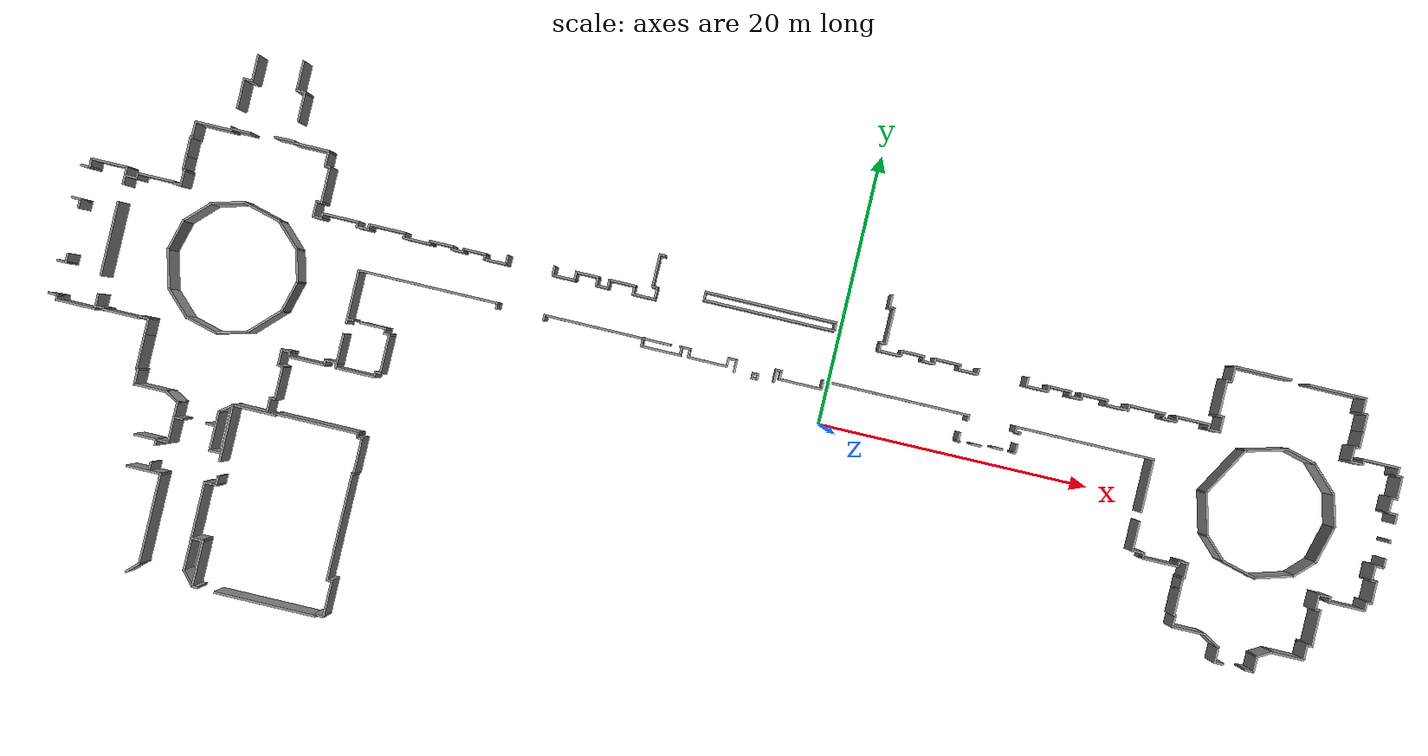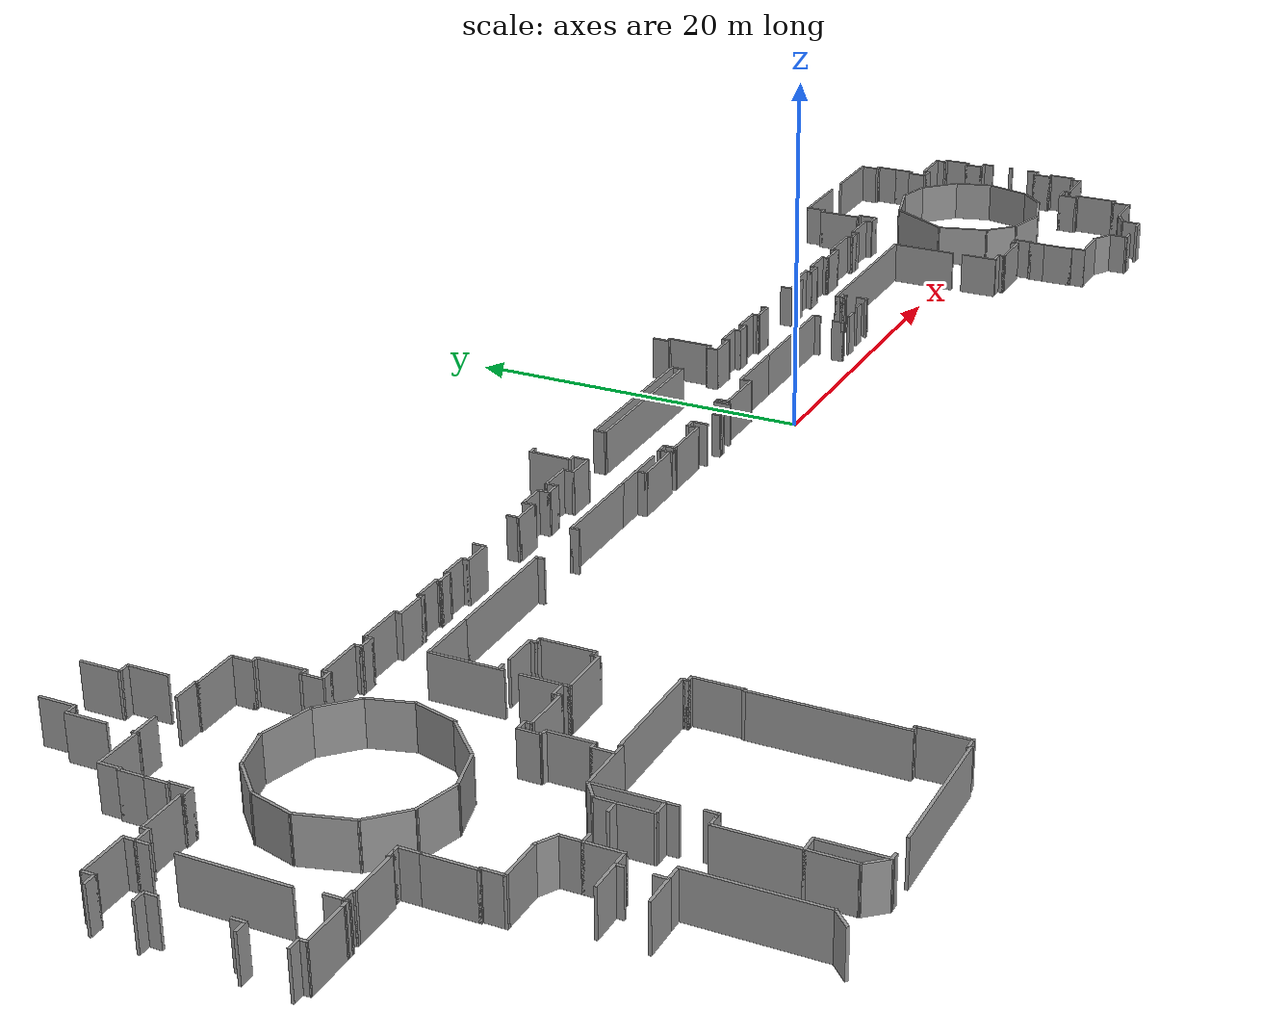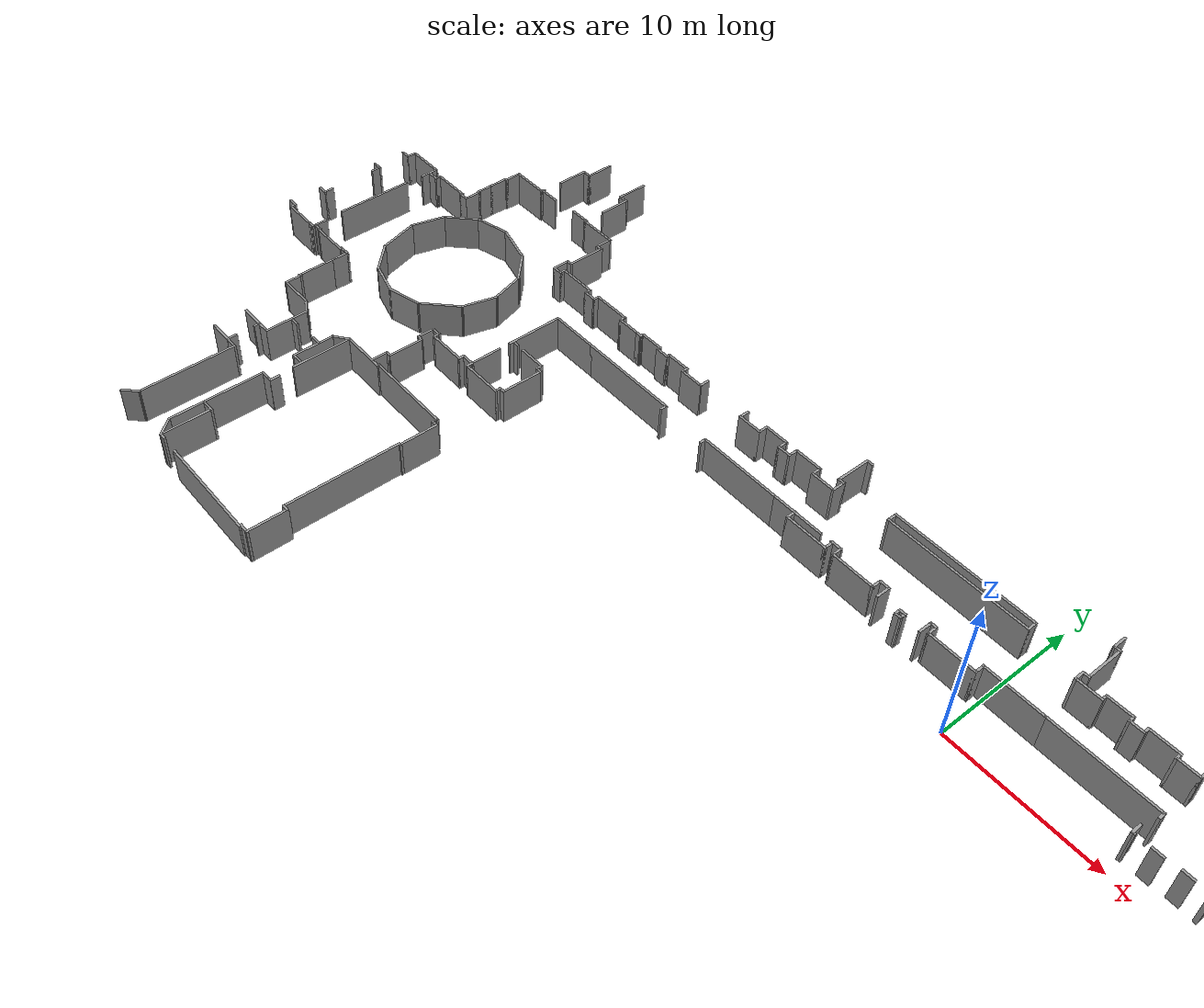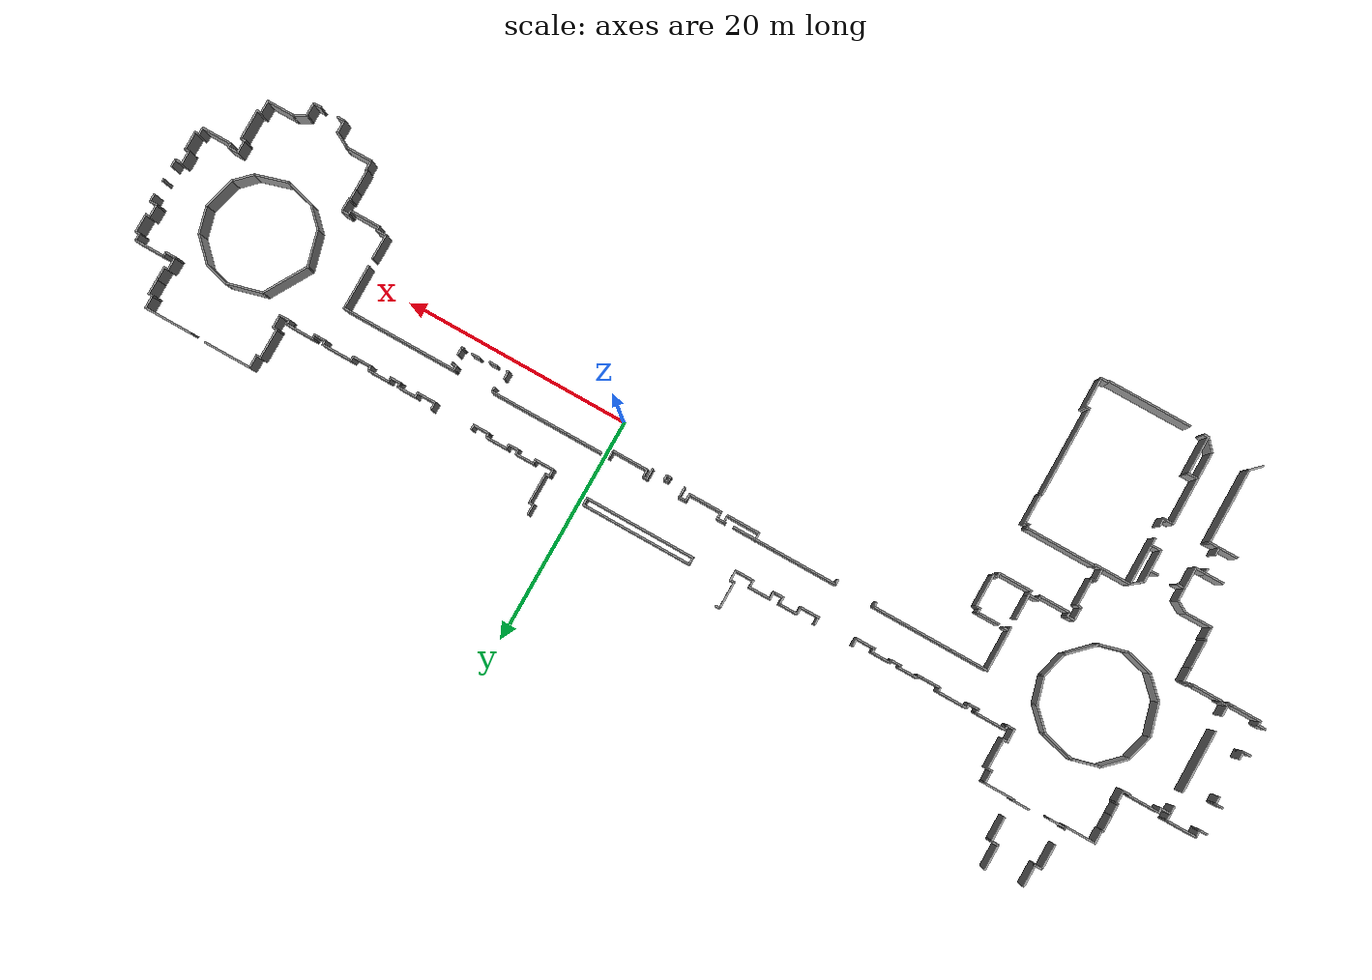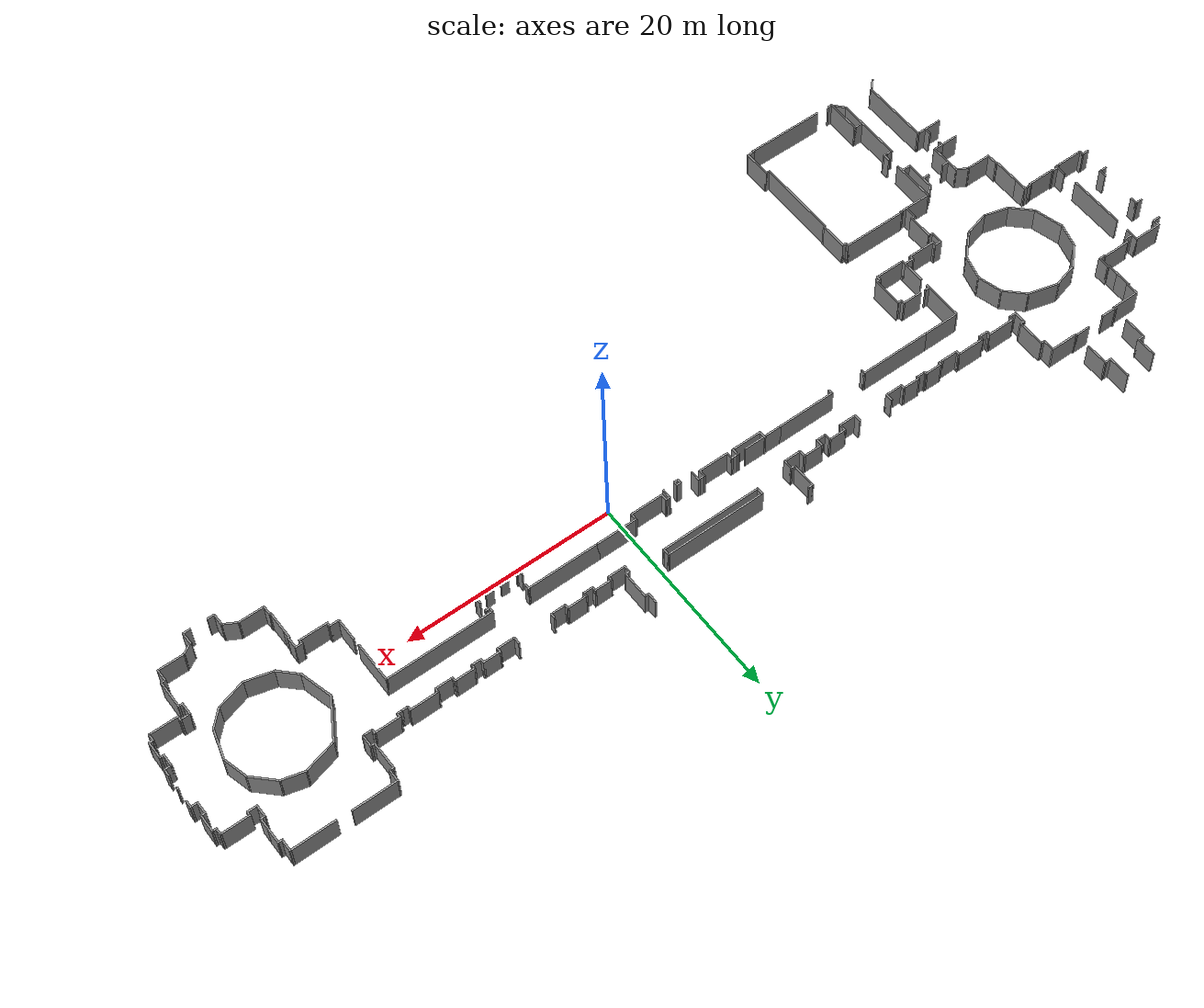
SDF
<?xml version='1.0'?>
<sdf version='1.7'>
  <model name='TD_n1'>
    <pose>-7.14234 -2.45461 0 0 -0 0</pose>
    <link name='Wall_0'>
      <collision name='Wall_0_Collision'>
        <geometry>
          <box>
            <size>3.25 0.15 2.5</size>
          </box>
        </geometry>
        <pose>0 0 1.25 0 -0 0</pose>
      </collision>
      <visual name='Wall_0_Visual'>
        <pose>0 0 1.25 0 -0 0</pose>
        <geometry>
          <box>
            <size>3.25 0.15 2.5</size>
          </box>
        </geometry>
        <material>
          <script>
            <uri>file://media/materials/scripts/gazebo.material</uri>
            <name>Gazebo/Grey</name>
          </script>
          <ambient>1 1 1 1</ambient>
        </material>
        <meta>
          <layer>0</layer>
        </meta>
      </visual>
      <pose>-32.5977 -5.86838 0 0 -0 0</pose>
    </link>
    <link name='Wall_1'>
      <collision name='Wall_1_Collision'>
        <geometry>
          <box>
            <size>0.25 0.15 2.5</size>
          </box>
        </geometry>
        <pose>0 0 1.25 0 -0 0</pose>
      </collision>
      <visual name='Wall_1_Visual'>
        <pose>0 0 1.25 0 -0 0</pose>
        <geometry>
          <box>
            <size>0.25 0.15 2.5</size>
          </box>
        </geometry>
        <material>
          <script>
            <uri>file://media/materials/scripts/gazebo.material</uri>
            <name>Gazebo/Grey</name>
          </script>
          <ambient>1 1 1 1</ambient>
        </material>
        <meta>
          <layer>0</layer>
        </meta>
      </visual>
      <pose>-31.0477 -5.81838 0 0 -0 1.5708</pose>
    </link>
    <link name='Wall_10'>
      <collision name='Wall_10_Collision'>
        <geometry>
          <box>
            <size>0.5 0.15 2.5</size>
          </box>
        </geometry>
        <pose>0 0 1.25 0 -0 0</pose>
      </collision>
      <visual name='Wall_10_Visual'>
        <pose>0 0 1.25 0 -0 0</pose>
        <geometry>
          <box>
            <size>0.5 0.15 2.5</size>
          </box>
        </geometry>
        <material>
          <script>
            <uri>file://media/materials/scripts/gazebo.material</uri>
            <name>Gazebo/Grey</name>
          </script>
          <ambient>1 1 1 1</ambient>
        </material>
        <meta>
          <layer>0</layer>
        </meta>
      </visual>
      <pose>-24.5227 -16.5184 0 0 -0 0</pose>
    </link>
    <link name='Wall_100'>
      <collision name='Wall_100_Collision'>
        <geometry>
          <box>
            <size>2 0.15 2.5</size>
          </box>
        </geometry>
        <pose>0 0 1.25 0 -0 0</pose>
      </collision>
      <visual name='Wall_100_Visual'>
        <pose>0 0 1.25 0 -0 0</pose>
        <geometry>
          <box>
            <size>2 0.15 2.5</size>
          </box>
        </geometry>
        <material>
          <script>
            <uri>file://media/materials/scripts/gazebo.material</uri>
            <name>Gazebo/Grey</name>
          </script>
          <ambient>1 1 1 1</ambient>
        </material>
        <meta>
          <layer>0</layer>
        </meta>
      </visual>
      <pose>-25.6799 1.99288 0 0 -0 3.14159</pose>
    </link>
    <link name='Wall_102'>
      <collision name='Wall_102_Collision'>
        <geometry>
          <box>
            <size>2.5 0.15 2.5</size>
          </box>
        </geometry>
        <pose>0 0 1.25 0 -0 0</pose>
      </collision>
      <visual name='Wall_102_Visual'>
        <pose>0 0 1.25 0 -0 0</pose>
        <geometry>
          <box>
            <size>2.5 0.15 2.5</size>
          </box>
        </geometry>
        <material>
          <script>
            <uri>file://media/materials/scripts/gazebo.material</uri>
            <name>Gazebo/Grey</name>
          </script>
          <ambient>1 1 1 1</ambient>
        </material>
        <meta>
          <layer>0</layer>
        </meta>
      </visual>
      <pose>-37.7105 -0.793001 0 0 -0 2.87979</pose>
    </link>
    <link name='Wall_103'>
      <collision name='Wall_103_Collision'>
        <geometry>
          <box>
            <size>2.5 0.15 2.5</size>
          </box>
        </geometry>
        <pose>0 0 1.25 0 -0 0</pose>
      </collision>
      <visual name='Wall_103_Visual'>
        <pose>0 0 1.25 0 -0 0</pose>
        <geometry>
          <box>
            <size>2.5 0.15 2.5</size>
          </box>
        </geometry>
        <material>
          <script>
            <uri>file://media/materials/scripts/gazebo.material</uri>
            <name>Gazebo/Grey</name>
          </script>
          <ambient>1 1 1 1</ambient>
        </material>
        <meta>
          <layer>0</layer>
        </meta>
      </visual>
      <pose>-39.6763 0.341962 0 0 -0 2.35619</pose>
    </link>
    <link name='Wall_104'>
      <collision name='Wall_104_Collision'>
        <geometry>
          <box>
            <size>3 0.15 2.5</size>
          </box>
        </geometry>
        <pose>0 0 1.25 0 -0 0</pose>
      </collision>
      <visual name='Wall_104_Visual'>
        <pose>0 0 1.25 0 -0 0</pose>
        <geometry>
          <box>
            <size>3 0.15 2.5</size>
          </box>
        </geometry>
        <material>
          <script>
            <uri>file://media/materials/scripts/gazebo.material</uri>
            <name>Gazebo/Grey</name>
          </script>
          <ambient>1 1 1 1</ambient>
        </material>
        <meta>
          <layer>0</layer>
        </meta>
      </visual>
      <pose>-40.876 2.54926 0 0 -0 1.8326</pose>
    </link>
    <link name='Wall_105'>
      <collision name='Wall_105_Collision'>
        <geometry>
          <box>
            <size>2.5 0.15 2.5</size>
          </box>
        </geometry>
        <pose>0 0 1.25 0 -0 0</pose>
      </collision>
      <visual name='Wall_105_Visual'>
        <pose>0 0 1.25 0 -0 0</pose>
        <geometry>
          <box>
            <size>2.5 0.15 2.5</size>
          </box>
        </geometry>
        <material>
          <script>
            <uri>file://media/materials/scripts/gazebo.material</uri>
            <name>Gazebo/Grey</name>
          </script>
          <ambient>1 1 1 1</ambient>
        </material>
        <meta>
          <layer>0</layer>
        </meta>
      </visual>
      <pose>-40.9407 5.06066 0 0 -0 1.309</pose>
    </link>
    <link name='Wall_106'>
      <collision name='Wall_106_Collision'>
        <geometry>
          <box>
            <size>2.5 0.15 2.5</size>
          </box>
        </geometry>
        <pose>0 0 1.25 0 -0 0</pose>
      </collision>
      <visual name='Wall_106_Visual'>
        <pose>0 0 1.25 0 -0 0</pose>
        <geometry>
          <box>
            <size>2.5 0.15 2.5</size>
          </box>
        </geometry>
        <material>
          <script>
            <uri>file://media/materials/scripts/gazebo.material</uri>
            <name>Gazebo/Grey</name>
          </script>
          <ambient>1 1 1 1</ambient>
        </material>
        <meta>
          <layer>0</layer>
        </meta>
      </visual>
      <pose>-39.8057 7.02648 0 0 -0 0.785398</pose>
    </link>
    <link name='Wall_107'>
      <collision name='Wall_107_Collision'>
        <geometry>
          <box>
            <size>2.5 0.15 2.5</size>
          </box>
        </geometry>
        <pose>0 0 1.25 0 -0 0</pose>
      </collision>
      <visual name='Wall_107_Visual'>
        <pose>0 0 1.25 0 -0 0</pose>
        <geometry>
          <box>
            <size>2.5 0.15 2.5</size>
          </box>
        </geometry>
        <material>
          <script>
            <uri>file://media/materials/scripts/gazebo.material</uri>
            <name>Gazebo/Grey</name>
          </script>
          <ambient>1 1 1 1</ambient>
        </material>
        <meta>
          <layer>0</layer>
        </meta>
      </visual>
      <pose>-37.8399 8.16144 0 0 -0 0.261799</pose>
    </link>
    <link name='Wall_108'>
      <collision name='Wall_108_Collision'>
        <geometry>
          <box>
            <size>3 0.15 2.5</size>
          </box>
        </geometry>
        <pose>0 0 1.25 0 -0 0</pose>
      </collision>
      <visual name='Wall_108_Visual'>
        <pose>0 0 1.25 0 -0 0</pose>
        <geometry>
          <box>
            <size>3 0.15 2.5</size>
          </box>
        </geometry>
        <material>
          <script>
            <uri>file://media/materials/scripts/gazebo.material</uri>
            <name>Gazebo/Grey</name>
          </script>
          <ambient>1 1 1 1</ambient>
        </material>
        <meta>
          <layer>0</layer>
        </meta>
      </visual>
      <pose>-35.3285 8.09674 0 0 -0 -0.261799</pose>
    </link>
    <link name='Wall_109'>
      <collision name='Wall_109_Collision'>
        <geometry>
          <box>
            <size>2.5 0.15 2.5</size>
          </box>
        </geometry>
        <pose>0 0 1.25 0 -0 0</pose>
      </collision>
      <visual name='Wall_109_Visual'>
        <pose>0 0 1.25 0 -0 0</pose>
        <geometry>
          <box>
            <size>2.5 0.15 2.5</size>
          </box>
        </geometry>
        <material>
          <script>
            <uri>file://media/materials/scripts/gazebo.material</uri>
            <name>Gazebo/Grey</name>
          </script>
          <ambient>1 1 1 1</ambient>
        </material>
        <meta>
          <layer>0</layer>
        </meta>
      </visual>
      <pose>-33.1212 6.89707 0 0 -0 -0.785398</pose>
    </link>
    <link name='Wall_11'>
      <collision name='Wall_11_Collision'>
        <geometry>
          <box>
            <size>2.75 0.15 2.5</size>
          </box>
        </geometry>
        <pose>0 0 1.25 0 -0 0</pose>
      </collision>
      <visual name='Wall_11_Visual'>
        <pose>0 0 1.25 0 -0 0</pose>
        <geometry>
          <box>
            <size>2.75 0.15 2.5</size>
          </box>
        </geometry>
        <material>
          <script>
            <uri>file://media/materials/scripts/gazebo.material</uri>
            <name>Gazebo/Grey</name>
          </script>
          <ambient>1 1 1 1</ambient>
        </material>
        <meta>
          <layer>0</layer>
        </meta>
      </visual>
      <pose>-24.3477 -17.8184 0 0 -0 -1.5708</pose>
    </link>
    <link name='Wall_110'>
      <collision name='Wall_110_Collision'>
        <geometry>
          <box>
            <size>2.5 0.15 2.5</size>
          </box>
        </geometry>
        <pose>0 0 1.25 0 -0 0</pose>
      </collision>
      <visual name='Wall_110_Visual'>
        <pose>0 0 1.25 0 -0 0</pose>
        <geometry>
          <box>
            <size>2.5 0.15 2.5</size>
          </box>
        </geometry>
        <material>
          <script>
            <uri>file://media/materials/scripts/gazebo.material</uri>
            <name>Gazebo/Grey</name>
          </script>
          <ambient>1 1 1 1</ambient>
        </material>
        <meta>
          <layer>0</layer>
        </meta>
      </visual>
      <pose>-31.9862 4.93125 0 0 -0 -1.309</pose>
    </link>
    <link name='Wall_111'>
      <collision name='Wall_111_Collision'>
        <geometry>
          <box>
            <size>2.5 0.15 2.5</size>
          </box>
        </geometry>
        <pose>0 0 1.25 0 -0 0</pose>
      </collision>
      <visual name='Wall_111_Visual'>
        <pose>0 0 1.25 0 -0 0</pose>
        <geometry>
          <box>
            <size>2.5 0.15 2.5</size>
          </box>
        </geometry>
        <material>
          <script>
            <uri>file://media/materials/scripts/gazebo.material</uri>
            <name>Gazebo/Grey</name>
          </script>
          <ambient>1 1 1 1</ambient>
        </material>
        <meta>
          <layer>0</layer>
        </meta>
      </visual>
      <pose>-31.9862 2.66133 0 0 -0 -1.8326</pose>
    </link>
    <link name='Wall_112'>
      <collision name='Wall_112_Collision'>
        <geometry>
          <box>
            <size>3 0.15 2.5</size>
          </box>
        </geometry>
        <pose>0 0 1.25 0 -0 0</pose>
      </collision>
      <visual name='Wall_112_Visual'>
        <pose>0 0 1.25 0 -0 0</pose>
        <geometry>
          <box>
            <size>3 0.15 2.5</size>
          </box>
        </geometry>
        <material>
          <script>
            <uri>file://media/materials/scripts/gazebo.material</uri>
            <name>Gazebo/Grey</name>
          </script>
          <ambient>1 1 1 1</ambient>
        </material>
        <meta>
          <layer>0</layer>
        </meta>
      </visual>
      <pose>-33.298 0.518739 0 0 -0 -2.35619</pose>
    </link>
    <link name='Wall_113'>
      <collision name='Wall_113_Collision'>
        <geometry>
          <box>
            <size>2.5 0.15 2.5</size>
          </box>
        </geometry>
        <pose>0 0 1.25 0 -0 0</pose>
      </collision>
      <visual name='Wall_113_Visual'>
        <pose>0 0 1.25 0 -0 0</pose>
        <geometry>
          <box>
            <size>2.5 0.15 2.5</size>
          </box>
        </geometry>
        <material>
          <script>
            <uri>file://media/materials/scripts/gazebo.material</uri>
            <name>Gazebo/Grey</name>
          </script>
          <ambient>1 1 1 1</ambient>
        </material>
        <meta>
          <layer>0</layer>
        </meta>
      </visual>
      <pose>-35.4406 -0.793001 0 0 -0 -2.87979</pose>
    </link>
    <link name='Wall_115'>
      <collision name='Wall_115_Collision'>
        <geometry>
          <box>
            <size>0.75 0.15 2.5</size>
          </box>
        </geometry>
        <pose>0 0 1.25 0 -0 0</pose>
      </collision>
      <visual name='Wall_115_Visual'>
        <pose>0 0 1.25 0 -0 0</pose>
        <geometry>
          <box>
            <size>0.75 0.15 2.5</size>
          </box>
        </geometry>
        <material>
          <script>
            <uri>file://media/materials/scripts/gazebo.material</uri>
            <name>Gazebo/Grey</name>
          </script>
          <ambient>1 1 1 1</ambient>
        </material>
        <meta>
          <layer>0</layer>
        </meta>
      </visual>
      <pose>-45.4577 8.08504 0 0 -0 1.5708</pose>
    </link>
    <link name='Wall_116'>
      <collision name='Wall_116_Collision'>
        <geometry>
          <box>
            <size>1 0.15 2.5</size>
          </box>
        </geometry>
        <pose>0 0 1.25 0 -0 0</pose>
      </collision>
      <visual name='Wall_116_Visual'>
        <pose>0 0 1.25 0 -0 0</pose>
        <geometry>
          <box>
            <size>1 0.15 2.5</size>
          </box>
        </geometry>
        <material>
          <script>
            <uri>file://media/materials/scripts/gazebo.material</uri>
            <name>Gazebo/Grey</name>
          </script>
          <ambient>1 1 1 1</ambient>
        </material>
        <meta>
          <layer>0</layer>
        </meta>
      </visual>
      <pose>-45.0327 8.38504 0 0 -0 0</pose>
    </link>
    <link name='Wall_117'>
      <collision name='Wall_117_Collision'>
        <geometry>
          <box>
            <size>0.5 0.15 2.5</size>
          </box>
        </geometry>
        <pose>0 0 1.25 0 -0 0</pose>
      </collision>
      <visual name='Wall_117_Visual'>
        <pose>0 0 1.25 0 -0 0</pose>
        <geometry>
          <box>
            <size>0.5 0.15 2.5</size>
          </box>
        </geometry>
        <material>
          <script>
            <uri>file://media/materials/scripts/gazebo.material</uri>
            <name>Gazebo/Grey</name>
          </script>
          <ambient>1 1 1 1</ambient>
        </material>
        <meta>
          <layer>0</layer>
        </meta>
      </visual>
      <pose>-44.6077 8.56004 0 0 -0 1.5708</pose>
    </link>
    <link name='Wall_118'>
      <collision name='Wall_118_Collision'>
        <geometry>
          <box>
            <size>2.75 0.15 2.5</size>
          </box>
        </geometry>
        <pose>0 0 1.25 0 -0 0</pose>
      </collision>
      <visual name='Wall_118_Visual'>
        <pose>0 0 1.25 0 -0 0</pose>
        <geometry>
          <box>
            <size>2.75 0.15 2.5</size>
          </box>
        </geometry>
        <material>
          <script>
            <uri>file://media/materials/scripts/gazebo.material</uri>
            <name>Gazebo/Grey</name>
          </script>
          <ambient>1 1 1 1</ambient>
        </material>
        <meta>
          <layer>0</layer>
        </meta>
      </visual>
      <pose>-43.3077 8.73504 0 0 -0 0</pose>
    </link>
    <link name='Wall_12'>
      <collision name='Wall_12_Collision'>
        <geometry>
          <box>
            <size>0.75 0.15 2.5</size>
          </box>
        </geometry>
        <pose>0 0 1.25 0 -0 0</pose>
      </collision>
      <visual name='Wall_12_Visual'>
        <pose>0 0 1.25 0 -0 0</pose>
        <geometry>
          <box>
            <size>0.75 0.15 2.5</size>
          </box>
        </geometry>
        <material>
          <script>
            <uri>file://media/materials/scripts/gazebo.material</uri>
            <name>Gazebo/Grey</name>
          </script>
          <ambient>1 1 1 1</ambient>
        </material>
        <meta>
          <layer>0</layer>
        </meta>
      </visual>
      <pose>-24.6477 -19.1184 0 0 -0 3.14159</pose>
    </link>
    <link name='Wall_121'>
      <collision name='Wall_121_Collision'>
        <geometry>
          <box>
            <size>0.25 0.15 2.5</size>
          </box>
        </geometry>
        <pose>0 0 1.25 0 -0 0</pose>
      </collision>
      <visual name='Wall_121_Visual'>
        <pose>0 0 1.25 0 -0 0</pose>
        <geometry>
          <box>
            <size>0.25 0.15 2.5</size>
          </box>
        </geometry>
        <material>
          <script>
            <uri>file://media/materials/scripts/gazebo.material</uri>
            <name>Gazebo/Grey</name>
          </script>
          <ambient>1 1 1 1</ambient>
        </material>
        <meta>
          <layer>0</layer>
        </meta>
      </visual>
      <pose>-42.0077 8.68504 0 0 -0 -1.5708</pose>
    </link>
    <link name='Wall_122'>
      <collision name='Wall_122_Collision'>
        <geometry>
          <box>
            <size>0.75 0.15 2.5</size>
          </box>
        </geometry>
        <pose>0 0 1.25 0 -0 0</pose>
      </collision>
      <visual name='Wall_122_Visual'>
        <pose>0 0 1.25 0 -0 0</pose>
        <geometry>
          <box>
            <size>0.75 0.15 2.5</size>
          </box>
        </geometry>
        <material>
          <script>
            <uri>file://media/materials/scripts/gazebo.material</uri>
            <name>Gazebo/Grey</name>
          </script>
          <ambient>1 1 1 1</ambient>
        </material>
        <meta>
          <layer>0</layer>
        </meta>
      </visual>
      <pose>-41.7077 8.63504 0 0 -0 0</pose>
    </link>
    <link name='Wall_123'>
      <collision name='Wall_123_Collision'>
        <geometry>
          <box>
            <size>1.25 0.15 2.5</size>
          </box>
        </geometry>
        <pose>0 0 1.25 0 -0 0</pose>
      </collision>
      <visual name='Wall_123_Visual'>
        <pose>0 0 1.25 0 -0 0</pose>
        <geometry>
          <box>
            <size>1.25 0.15 2.5</size>
          </box>
        </geometry>
        <material>
          <script>
            <uri>file://media/materials/scripts/gazebo.material</uri>
            <name>Gazebo/Grey</name>
          </script>
          <ambient>1 1 1 1</ambient>
        </material>
        <meta>
          <layer>0</layer>
        </meta>
      </visual>
      <pose>-41.4077 9.18504 0 0 -0 1.5708</pose>
    </link>
    <link name='Wall_124'>
      <collision name='Wall_124_Collision'>
        <geometry>
          <box>
            <size>0.25 0.15 2.5</size>
          </box>
        </geometry>
        <pose>0 0 1.25 0 -0 0</pose>
      </collision>
      <visual name='Wall_124_Visual'>
        <pose>0 0 1.25 0 -0 0</pose>
        <geometry>
          <box>
            <size>0.25 0.15 2.5</size>
          </box>
        </geometry>
        <material>
          <script>
            <uri>file://media/materials/scripts/gazebo.material</uri>
            <name>Gazebo/Grey</name>
          </script>
          <ambient>1 1 1 1</ambient>
        </material>
        <meta>
          <layer>0</layer>
        </meta>
      </visual>
      <pose>-41.4577 9.73504 0 0 -0 3.14159</pose>
    </link>
    <link name='Wall_125'>
      <collision name='Wall_125_Collision'>
        <geometry>
          <box>
            <size>1.25 0.15 2.5</size>
          </box>
        </geometry>
        <pose>0 0 1.25 0 -0 0</pose>
      </collision>
      <visual name='Wall_125_Visual'>
        <pose>0 0 1.25 0 -0 0</pose>
        <geometry>
          <box>
            <size>1.25 0.15 2.5</size>
          </box>
        </geometry>
        <material>
          <script>
            <uri>file://media/materials/scripts/gazebo.material</uri>
            <name>Gazebo/Grey</name>
          </script>
          <ambient>1 1 1 1</ambient>
        </material>
        <meta>
          <layer>0</layer>
        </meta>
      </visual>
      <pose>-41.5077 10.285 0 0 -0 1.5708</pose>
    </link>
    <link name='Wall_127'>
      <collision name='Wall_127_Collision'>
        <geometry>
          <box>
            <size>1.5 0.15 2.5</size>
          </box>
        </geometry>
        <pose>0 0 1.25 0 -0 0</pose>
      </collision>
      <visual name='Wall_127_Visual'>
        <pose>0 0 1.25 0 -0 0</pose>
        <geometry>
          <box>
            <size>1.5 0.15 2.5</size>
          </box>
        </geometry>
        <material>
          <script>
            <uri>file://media/materials/scripts/gazebo.material</uri>
            <name>Gazebo/Grey</name>
          </script>
          <ambient>1 1 1 1</ambient>
        </material>
        <meta>
          <layer>0</layer>
        </meta>
      </visual>
      <pose>-41.5077 11.51 0 0 -0 1.5708</pose>
    </link>
    <link name='Wall_128'>
      <collision name='Wall_128_Collision'>
        <geometry>
          <box>
            <size>0.25 0.15 2.5</size>
          </box>
        </geometry>
        <pose>0 0 1.25 0 -0 0</pose>
      </collision>
      <visual name='Wall_128_Visual'>
        <pose>0 0 1.25 0 -0 0</pose>
        <geometry>
          <box>
            <size>0.25 0.15 2.5</size>
          </box>
        </geometry>
        <material>
          <script>
            <uri>file://media/materials/scripts/gazebo.material</uri>
            <name>Gazebo/Grey</name>
          </script>
          <ambient>1 1 1 1</ambient>
        </material>
        <meta>
          <layer>0</layer>
        </meta>
      </visual>
      <pose>-41.4577 12.185 0 0 -0 0</pose>
    </link>
    <link name='Wall_129'>
      <collision name='Wall_129_Collision'>
        <geometry>
          <box>
            <size>1.25 0.15 2.5</size>
          </box>
        </geometry>
        <pose>0 0 1.25 0 -0 0</pose>
      </collision>
      <visual name='Wall_129_Visual'>
        <pose>0 0 1.25 0 -0 0</pose>
        <geometry>
          <box>
            <size>1.25 0.15 2.5</size>
          </box>
        </geometry>
        <material>
          <script>
            <uri>file://media/materials/scripts/gazebo.material</uri>
            <name>Gazebo/Grey</name>
          </script>
          <ambient>1 1 1 1</ambient>
        </material>
        <meta>
          <layer>0</layer>
        </meta>
      </visual>
      <pose>-41.4077 12.735 0 0 -0 1.5708</pose>
    </link>
    <link name='Wall_13'>
      <collision name='Wall_13_Collision'>
        <geometry>
          <box>
            <size>0.25 0.15 2.5</size>
          </box>
        </geometry>
        <pose>0 0 1.25 0 -0 0</pose>
      </collision>
      <visual name='Wall_13_Visual'>
        <pose>0 0 1.25 0 -0 0</pose>
        <geometry>
          <box>
            <size>0.25 0.15 2.5</size>
          </box>
        </geometry>
        <material>
          <script>
            <uri>file://media/materials/scripts/gazebo.material</uri>
            <name>Gazebo/Grey</name>
          </script>
          <ambient>1 1 1 1</ambient>
        </material>
        <meta>
          <layer>0</layer>
        </meta>
      </visual>
      <pose>-24.9477 -19.1684 0 0 -0 -1.5708</pose>
    </link>
    <link name='Wall_130'>
      <collision name='Wall_130_Collision'>
        <geometry>
          <box>
            <size>2.75 0.15 2.5</size>
          </box>
        </geometry>
        <pose>0 0 1.25 0 -0 0</pose>
      </collision>
      <visual name='Wall_130_Visual'>
        <pose>0 0 1.25 0 -0 0</pose>
        <geometry>
          <box>
            <size>2.75 0.15 2.5</size>
          </box>
        </geometry>
        <material>
          <script>
            <uri>file://media/materials/scripts/gazebo.material</uri>
            <name>Gazebo/Grey</name>
          </script>
          <ambient>1 1 1 1</ambient>
        </material>
        <meta>
          <layer>0</layer>
        </meta>
      </visual>
      <pose>-40.1077 13.285 0 0 -0 0</pose>
    </link>
    <link name='Wall_131'>
      <collision name='Wall_131_Collision'>
        <geometry>
          <box>
            <size>0.25 0.15 2.5</size>
          </box>
        </geometry>
        <pose>0 0 1.25 0 -0 0</pose>
      </collision>
      <visual name='Wall_131_Visual'>
        <pose>0 0 1.25 0 -0 0</pose>
        <geometry>
          <box>
            <size>0.25 0.15 2.5</size>
          </box>
        </geometry>
        <material>
          <script>
            <uri>file://media/materials/scripts/gazebo.material</uri>
            <name>Gazebo/Grey</name>
          </script>
          <ambient>1 1 1 1</ambient>
        </material>
        <meta>
          <layer>0</layer>
        </meta>
      </visual>
      <pose>-38.8077 13.335 0 0 -0 1.5708</pose>
    </link>
    <link name='Wall_132'>
      <collision name='Wall_132_Collision'>
        <geometry>
          <box>
            <size>1.5 0.15 2.5</size>
          </box>
        </geometry>
        <pose>0 0 1.25 0 -0 0</pose>
      </collision>
      <visual name='Wall_132_Visual'>
        <pose>0 0 1.25 0 -0 0</pose>
        <geometry>
          <box>
            <size>1.5 0.15 2.5</size>
          </box>
        </geometry>
        <material>
          <script>
            <uri>file://media/materials/scripts/gazebo.material</uri>
            <name>Gazebo/Grey</name>
          </script>
          <ambient>1 1 1 1</ambient>
        </material>
        <meta>
          <layer>0</layer>
        </meta>
      </visual>
      <pose>-38.1327 13.385 0 0 -0 0</pose>
    </link>
    <link name='Wall_134'>
      <collision name='Wall_134_Collision'>
        <geometry>
          <box>
            <size>1.5 0.15 2.5</size>
          </box>
        </geometry>
        <pose>0 0 1.25 0 -0 0</pose>
      </collision>
      <visual name='Wall_134_Visual'>
        <pose>0 0 1.25 0 -0 0</pose>
        <geometry>
          <box>
            <size>1.5 0.15 2.5</size>
          </box>
        </geometry>
        <material>
          <script>
            <uri>file://media/materials/scripts/gazebo.material</uri>
            <name>Gazebo/Grey</name>
          </script>
          <ambient>1 1 1 1</ambient>
        </material>
        <meta>
          <layer>0</layer>
        </meta>
      </visual>
      <pose>-34.9371 13.5314 0 0 -0 0</pose>
    </link>
    <link name='Wall_135'>
      <collision name='Wall_135_Collision'>
        <geometry>
          <box>
            <size>0.25 0.15 2.5</size>
          </box>
        </geometry>
        <pose>0 0 1.25 0 -0 0</pose>
      </collision>
      <visual name='Wall_135_Visual'>
        <pose>0 0 1.25 0 -0 0</pose>
        <geometry>
          <box>
            <size>0.25 0.15 2.5</size>
          </box>
        </geometry>
        <material>
          <script>
            <uri>file://media/materials/scripts/gazebo.material</uri>
            <name>Gazebo/Grey</name>
          </script>
          <ambient>1 1 1 1</ambient>
        </material>
        <meta>
          <layer>0</layer>
        </meta>
      </visual>
      <pose>-34.2621 13.4814 0 0 -0 -1.5708</pose>
    </link>
    <link name='Wall_136'>
      <collision name='Wall_136_Collision'>
        <geometry>
          <box>
            <size>2.75 0.15 2.5</size>
          </box>
        </geometry>
        <pose>0 0 1.25 0 -0 0</pose>
      </collision>
      <visual name='Wall_136_Visual'>
        <pose>0 0 1.25 0 -0 0</pose>
        <geometry>
          <box>
            <size>2.75 0.15 2.5</size>
          </box>
        </geometry>
        <material>
          <script>
            <uri>file://media/materials/scripts/gazebo.material</uri>
            <name>Gazebo/Grey</name>
          </script>
          <ambient>1 1 1 1</ambient>
        </material>
        <meta>
          <layer>0</layer>
        </meta>
      </visual>
      <pose>-32.9621 13.4314 0 0 -0 0</pose>
    </link>
    <link name='Wall_137'>
      <collision name='Wall_137_Collision'>
        <geometry>
          <box>
            <size>1.25 0.15 2.5</size>
          </box>
        </geometry>
        <pose>0 0 1.25 0 -0 0</pose>
      </collision>
      <visual name='Wall_137_Visual'>
        <pose>0 0 1.25 0 -0 0</pose>
        <geometry>
          <box>
            <size>1.25 0.15 2.5</size>
          </box>
        </geometry>
        <material>
          <script>
            <uri>file://media/materials/scripts/gazebo.material</uri>
            <name>Gazebo/Grey</name>
          </script>
          <ambient>1 1 1 1</ambient>
        </material>
        <meta>
          <layer>0</layer>
        </meta>
      </visual>
      <pose>-31.6621 12.8814 0 0 -0 -1.5708</pose>
    </link>
    <link name='Wall_138'>
      <collision name='Wall_138_Collision'>
        <geometry>
          <box>
            <size>0.5 0.15 2.5</size>
          </box>
        </geometry>
        <pose>0 0 1.25 0 -0 0</pose>
      </collision>
      <visual name='Wall_138_Visual'>
        <pose>0 0 1.25 0 -0 0</pose>
        <geometry>
          <box>
            <size>0.5 0.15 2.5</size>
          </box>
        </geometry>
        <material>
          <script>
            <uri>file://media/materials/scripts/gazebo.material</uri>
            <name>Gazebo/Grey</name>
          </script>
          <ambient>1 1 1 1</ambient>
        </material>
        <meta>
          <layer>0</layer>
        </meta>
      </visual>
      <pose>-31.4871 12.3314 0 0 -0 0</pose>
    </link>
    <link name='Wall_139'>
      <collision name='Wall_139_Collision'>
        <geometry>
          <box>
            <size>2.75 0.15 2.5</size>
          </box>
        </geometry>
        <pose>0 0 1.25 0 -0 0</pose>
      </collision>
      <visual name='Wall_139_Visual'>
        <pose>0 0 1.25 0 -0 0</pose>
        <geometry>
          <box>
            <size>2.75 0.15 2.5</size>
          </box>
        </geometry>
        <material>
          <script>
            <uri>file://media/materials/scripts/gazebo.material</uri>
            <name>Gazebo/Grey</name>
          </script>
          <ambient>1 1 1 1</ambient>
        </material>
        <meta>
          <layer>0</layer>
        </meta>
      </visual>
      <pose>-31.3121 11.0314 0 0 -0 -1.5708</pose>
    </link>
    <link name='Wall_14'>
      <collision name='Wall_14_Collision'>
        <geometry>
          <box>
            <size>7.5 0.15 2.5</size>
          </box>
        </geometry>
        <pose>0 0 1.25 0 -0 0</pose>
      </collision>
      <visual name='Wall_14_Visual'>
        <pose>0 0 1.25 0 -0 0</pose>
        <geometry>
          <box>
            <size>7.5 0.15 2.5</size>
          </box>
        </geometry>
        <material>
          <script>
            <uri>file://media/materials/scripts/gazebo.material</uri>
            <name>Gazebo/Grey</name>
          </script>
          <ambient>1 1 1 1</ambient>
        </material>
        <meta>
          <layer>0</layer>
        </meta>
      </visual>
      <pose>-28.6227 -19.2184 0 0 -0 3.14159</pose>
    </link>
    <link name='Wall_141'>
      <collision name='Wall_141_Collision'>
        <geometry>
          <box>
            <size>0.5 0.15 2.5</size>
          </box>
        </geometry>
        <pose>0 0 1.25 0 -0 0</pose>
      </collision>
      <visual name='Wall_141_Visual'>
        <pose>0 0 1.25 0 -0 0</pose>
        <geometry>
          <box>
            <size>0.5 0.15 2.5</size>
          </box>
        </geometry>
        <material>
          <script>
            <uri>file://media/materials/scripts/gazebo.material</uri>
            <name>Gazebo/Grey</name>
          </script>
          <ambient>1 1 1 1</ambient>
        </material>
        <meta>
          <layer>0</layer>
        </meta>
      </visual>
      <pose>-31.4871 9.73136 0 0 -0 3.14159</pose>
    </link>
    <link name='Wall_142'>
      <collision name='Wall_142_Collision'>
        <geometry>
          <box>
            <size>1.25 0.15 2.5</size>
          </box>
        </geometry>
        <pose>0 0 1.25 0 -0 0</pose>
      </collision>
      <visual name='Wall_142_Visual'>
        <pose>0 0 1.25 0 -0 0</pose>
        <geometry>
          <box>
            <size>1.25 0.15 2.5</size>
          </box>
        </geometry>
        <material>
          <script>
            <uri>file://media/materials/scripts/gazebo.material</uri>
            <name>Gazebo/Grey</name>
          </script>
          <ambient>1 1 1 1</ambient>
        </material>
        <meta>
          <layer>0</layer>
        </meta>
      </visual>
      <pose>-31.6621 9.18136 0 0 -0 -1.5708</pose>
    </link>
    <link name='Wall_143'>
      <collision name='Wall_143_Collision'>
        <geometry>
          <box>
            <size>0.75 0.15 2.5</size>
          </box>
        </geometry>
        <pose>0 0 1.25 0 -0 0</pose>
      </collision>
      <visual name='Wall_143_Visual'>
        <pose>0 0 1.25 0 -0 0</pose>
        <geometry>
          <box>
            <size>0.75 0.15 2.5</size>
          </box>
        </geometry>
        <material>
          <script>
            <uri>file://media/materials/scripts/gazebo.material</uri>
            <name>Gazebo/Grey</name>
          </script>
          <ambient>1 1 1 1</ambient>
        </material>
        <meta>
          <layer>0</layer>
        </meta>
      </visual>
      <pose>-31.3621 8.63136 0 0 -0 0</pose>
    </link>
    <link name='Wall_144'>
      <collision name='Wall_144_Collision'>
        <geometry>
          <box>
            <size>0.5 0.15 2.5</size>
          </box>
        </geometry>
        <pose>0 0 1.25 0 -0 0</pose>
      </collision>
      <visual name='Wall_144_Visual'>
        <pose>0 0 1.25 0 -0 0</pose>
        <geometry>
          <box>
            <size>0.5 0.15 2.5</size>
          </box>
        </geometry>
        <material>
          <script>
            <uri>file://media/materials/scripts/gazebo.material</uri>
            <name>Gazebo/Grey</name>
          </script>
          <ambient>1 1 1 1</ambient>
        </material>
        <meta>
          <layer>0</layer>
        </meta>
      </visual>
      <pose>-31.0621 8.80636 0 0 -0 1.5708</pose>
    </link>
    <link name='Wall_145'>
      <collision name='Wall_145_Collision'>
        <geometry>
          <box>
            <size>2.75 0.15 2.5</size>
          </box>
        </geometry>
        <pose>0 0 1.25 0 -0 0</pose>
      </collision>
      <visual name='Wall_145_Visual'>
        <pose>0 0 1.25 0 -0 0</pose>
        <geometry>
          <box>
            <size>2.75 0.15 2.5</size>
          </box>
        </geometry>
        <material>
          <script>
            <uri>file://media/materials/scripts/gazebo.material</uri>
            <name>Gazebo/Grey</name>
          </script>
          <ambient>1 1 1 1</ambient>
        </material>
        <meta>
          <layer>0</layer>
        </meta>
      </visual>
      <pose>-29.7621 8.98136 0 0 -0 0</pose>
    </link>
    <link name='Wall_146'>
      <collision name='Wall_146_Collision'>
        <geometry>
          <box>
            <size>0.5 0.15 2.5</size>
          </box>
        </geometry>
        <pose>0 0 1.25 0 -0 0</pose>
      </collision>
      <visual name='Wall_146_Visual'>
        <pose>0 0 1.25 0 -0 0</pose>
        <geometry>
          <box>
            <size>0.5 0.15 2.5</size>
          </box>
        </geometry>
        <material>
          <script>
            <uri>file://media/materials/scripts/gazebo.material</uri>
            <name>Gazebo/Grey</name>
          </script>
          <ambient>1 1 1 1</ambient>
        </material>
        <meta>
          <layer>0</layer>
        </meta>
      </visual>
      <pose>-28.4621 8.80636 0 0 -0 -1.5708</pose>
    </link>
    <link name='Wall_147'>
      <collision name='Wall_147_Collision'>
        <geometry>
          <box>
            <size>1 0.15 2.5</size>
          </box>
        </geometry>
        <pose>0 0 1.25 0 -0 0</pose>
      </collision>
      <visual name='Wall_147_Visual'>
        <pose>0 0 1.25 0 -0 0</pose>
        <geometry>
          <box>
            <size>1 0.15 2.5</size>
          </box>
        </geometry>
        <material>
          <script>
            <uri>file://media/materials/scripts/gazebo.material</uri>
            <name>Gazebo/Grey</name>
          </script>
          <ambient>1 1 1 1</ambient>
        </material>
        <meta>
          <layer>0</layer>
        </meta>
      </visual>
      <pose>-28.0371 8.63136 0 0 -0 0</pose>
    </link>
    <link name='Wall_148'>
      <collision name='Wall_148_Collision'>
        <geometry>
          <box>
            <size>0.5 0.15 2.5</size>
          </box>
        </geometry>
        <pose>0 0 1.25 0 -0 0</pose>
      </collision>
      <visual name='Wall_148_Visual'>
        <pose>0 0 1.25 0 -0 0</pose>
        <geometry>
          <box>
            <size>0.5 0.15 2.5</size>
          </box>
        </geometry>
        <material>
          <script>
            <uri>file://media/materials/scripts/gazebo.material</uri>
            <name>Gazebo/Grey</name>
          </script>
          <ambient>1 1 1 1</ambient>
        </material>
        <meta>
          <layer>0</layer>
        </meta>
      </visual>
      <pose>-27.6121 8.80636 0 0 -0 1.5708</pose>
    </link>
    <link name='Wall_149'>
      <collision name='Wall_149_Collision'>
        <geometry>
          <box>
            <size>2.75 0.15 2.5</size>
          </box>
        </geometry>
        <pose>0 0 1.25 0 -0 0</pose>
      </collision>
      <visual name='Wall_149_Visual'>
        <pose>0 0 1.25 0 -0 0</pose>
        <geometry>
          <box>
            <size>2.75 0.15 2.5</size>
          </box>
        </geometry>
        <material>
          <script>
            <uri>file://media/materials/scripts/gazebo.material</uri>
            <name>Gazebo/Grey</name>
          </script>
          <ambient>1 1 1 1</ambient>
        </material>
        <meta>
          <layer>0</layer>
        </meta>
      </visual>
      <pose>-26.3121 8.98136 0 0 -0 0</pose>
    </link>
    <link name='Wall_150'>
      <collision name='Wall_150_Collision'>
        <geometry>
          <box>
            <size>0.5 0.15 2.5</size>
          </box>
        </geometry>
        <pose>0 0 1.25 0 -0 0</pose>
      </collision>
      <visual name='Wall_150_Visual'>
        <pose>0 0 1.25 0 -0 0</pose>
        <geometry>
          <box>
            <size>0.5 0.15 2.5</size>
          </box>
        </geometry>
        <material>
          <script>
            <uri>file://media/materials/scripts/gazebo.material</uri>
            <name>Gazebo/Grey</name>
          </script>
          <ambient>1 1 1 1</ambient>
        </material>
        <meta>
          <layer>0</layer>
        </meta>
      </visual>
      <pose>-25.0121 8.80636 0 0 -0 -1.5708</pose>
    </link>
    <link name='Wall_151'>
      <collision name='Wall_151_Collision'>
        <geometry>
          <box>
            <size>1.75 0.15 2.5</size>
          </box>
        </geometry>
        <pose>0 0 1.25 0 -0 0</pose>
      </collision>
      <visual name='Wall_151_Visual'>
        <pose>0 0 1.25 0 -0 0</pose>
        <geometry>
          <box>
            <size>1.75 0.15 2.5</size>
          </box>
        </geometry>
        <material>
          <script>
            <uri>file://media/materials/scripts/gazebo.material</uri>
            <name>Gazebo/Grey</name>
          </script>
          <ambient>1 1 1 1</ambient>
        </material>
        <meta>
          <layer>0</layer>
        </meta>
      </visual>
      <pose>-24.2121 8.63136 0 0 -0 0</pose>
    </link>
    <link name='Wall_152'>
      <collision name='Wall_152_Collision'>
        <geometry>
          <box>
            <size>0.5 0.15 2.5</size>
          </box>
        </geometry>
        <pose>0 0 1.25 0 -0 0</pose>
      </collision>
      <visual name='Wall_152_Visual'>
        <pose>0 0 1.25 0 -0 0</pose>
        <geometry>
          <box>
            <size>0.5 0.15 2.5</size>
          </box>
        </geometry>
        <material>
          <script>
            <uri>file://media/materials/scripts/gazebo.material</uri>
            <name>Gazebo/Grey</name>
          </script>
          <ambient>1 1 1 1</ambient>
        </material>
        <meta>
          <layer>0</layer>
        </meta>
      </visual>
      <pose>-23.2371 8.63136 0 0 -0 0</pose>
    </link>
    <link name='Wall_153'>
      <collision name='Wall_153_Collision'>
        <geometry>
          <box>
            <size>0.25 0.15 2.5</size>
          </box>
        </geometry>
        <pose>0 0 1.25 0 -0 0</pose>
      </collision>
      <visual name='Wall_153_Visual'>
        <pose>0 0 1.25 0 -0 0</pose>
        <geometry>
          <box>
            <size>0.25 0.15 2.5</size>
          </box>
        </geometry>
        <material>
          <script>
            <uri>file://media/materials/scripts/gazebo.material</uri>
            <name>Gazebo/Grey</name>
          </script>
          <ambient>1 1 1 1</ambient>
        </material>
        <meta>
          <layer>0</layer>
        </meta>
      </visual>
      <pose>-23.0751 8.67966 0 0 -0 1.8326</pose>
    </link>
    <link name='Wall_154'>
      <collision name='Wall_154_Collision'>
        <geometry>
          <box>
            <size>0.25 0.15 2.5</size>
          </box>
        </geometry>
        <pose>0 0 1.25 0 -0 0</pose>
      </collision>
      <visual name='Wall_154_Visual'>
        <pose>0 0 1.25 0 -0 0</pose>
        <geometry>
          <box>
            <size>0.25 0.15 2.5</size>
          </box>
        </geometry>
        <material>
          <script>
            <uri>file://media/materials/scripts/gazebo.material</uri>
            <name>Gazebo/Grey</name>
          </script>
          <ambient>1 1 1 1</ambient>
        </material>
        <meta>
          <layer>0</layer>
        </meta>
      </visual>
      <pose>-23.088 8.77796 0 0 -0 1.5708</pose>
    </link>
    <link name='Wall_155'>
      <collision name='Wall_155_Collision'>
        <geometry>
          <box>
            <size>1.75 0.15 2.5</size>
          </box>
        </geometry>
        <pose>0 0 1.25 0 -0 0</pose>
      </collision>
      <visual name='Wall_155_Visual'>
        <pose>0 0 1.25 0 -0 0</pose>
        <geometry>
          <box>
            <size>1.75 0.15 2.5</size>
          </box>
        </geometry>
        <material>
          <script>
            <uri>file://media/materials/scripts/gazebo.material</uri>
            <name>Gazebo/Grey</name>
          </script>
          <ambient>1 1 1 1</ambient>
        </material>
        <meta>
          <layer>0</layer>
        </meta>
      </visual>
      <pose>-22.288 8.82795 0 0 -0 0</pose>
    </link>
    <link name='Wall_157'>
      <collision name='Wall_157_Collision'>
        <geometry>
          <box>
            <size>0.25 0.15 2.5</size>
          </box>
        </geometry>
        <pose>0 0 1.25 0 -0 0</pose>
      </collision>
      <visual name='Wall_157_Visual'>
        <pose>0 0 1.25 0 -0 0</pose>
        <geometry>
          <box>
            <size>0.25 0.15 2.5</size>
          </box>
        </geometry>
        <material>
          <script>
            <uri>file://media/materials/scripts/gazebo.material</uri>
            <name>Gazebo/Grey</name>
          </script>
          <ambient>1 1 1 1</ambient>
        </material>
        <meta>
          <layer>0</layer>
        </meta>
      </visual>
      <pose>-38.8077 13.435 0 0 -0 1.5708</pose>
    </link>
    <link name='Wall_159'>
      <collision name='Wall_159_Collision'>
        <geometry>
          <box>
            <size>2.25 0.15 2.5</size>
          </box>
        </geometry>
        <pose>0 0 1.25 0 -0 0</pose>
      </collision>
      <visual name='Wall_159_Visual'>
        <pose>0 0 1.25 0 -0 0</pose>
        <geometry>
          <box>
            <size>2.25 0.15 2.5</size>
          </box>
        </geometry>
        <material>
          <script>
            <uri>file://media/materials/scripts/gazebo.material</uri>
            <name>Gazebo/Grey</name>
          </script>
          <ambient>1 1 1 1</ambient>
        </material>
        <meta>
          <layer>0</layer>
        </meta>
      </visual>
      <pose>-38.7414 16.0283 0 0 -0 1.5708</pose>
    </link>
    <link name='Wall_16'>
      <collision name='Wall_16_Collision'>
        <geometry>
          <box>
            <size>0.5 0.15 2.5</size>
          </box>
        </geometry>
        <pose>0 0 1.25 0 -0 0</pose>
      </collision>
      <visual name='Wall_16_Visual'>
        <pose>0 0 1.25 0 -0 0</pose>
        <geometry>
          <box>
            <size>0.5 0.15 2.5</size>
          </box>
        </geometry>
        <material>
          <script>
            <uri>file://media/materials/scripts/gazebo.material</uri>
            <name>Gazebo/Grey</name>
          </script>
          <ambient>1 1 1 1</ambient>
        </material>
        <meta>
          <layer>0</layer>
        </meta>
      </visual>
      <pose>-33.8173 -19.1685 0 0 -0 3.14159</pose>
    </link>
    <link name='Wall_160'>
      <collision name='Wall_160_Collision'>
        <geometry>
          <box>
            <size>0.75 0.15 2.5</size>
          </box>
        </geometry>
        <pose>0 0 1.25 0 -0 0</pose>
      </collision>
      <visual name='Wall_160_Visual'>
        <pose>0 0 1.25 0 -0 0</pose>
        <geometry>
          <box>
            <size>0.75 0.15 2.5</size>
          </box>
        </geometry>
        <material>
          <script>
            <uri>file://media/materials/scripts/gazebo.material</uri>
            <name>Gazebo/Grey</name>
          </script>
          <ambient>1 1 1 1</ambient>
        </material>
        <meta>
          <layer>0</layer>
        </meta>
      </visual>
      <pose>-38.4414 17.0783 0 0 -0 0</pose>
    </link>
    <link name='Wall_161'>
      <collision name='Wall_161_Collision'>
        <geometry>
          <box>
            <size>2 0.15 2.5</size>
          </box>
        </geometry>
        <pose>0 0 1.25 0 -0 0</pose>
      </collision>
      <visual name='Wall_161_Visual'>
        <pose>0 0 1.25 0 -0 0</pose>
        <geometry>
          <box>
            <size>2 0.15 2.5</size>
          </box>
        </geometry>
        <material>
          <script>
            <uri>file://media/materials/scripts/gazebo.material</uri>
            <name>Gazebo/Grey</name>
          </script>
          <ambient>1 1 1 1</ambient>
        </material>
        <meta>
          <layer>0</layer>
        </meta>
      </visual>
      <pose>-38.1414 18.0033 0 0 -0 1.5708</pose>
    </link>
    <link name='Wall_163'>
      <collision name='Wall_163_Collision'>
        <geometry>
          <box>
            <size>2.25 0.15 2.5</size>
          </box>
        </geometry>
        <pose>0 0 1.25 0 -0 0</pose>
      </collision>
      <visual name='Wall_163_Visual'>
        <pose>0 0 1.25 0 -0 0</pose>
        <geometry>
          <box>
            <size>2.25 0.15 2.5</size>
          </box>
        </geometry>
        <material>
          <script>
            <uri>file://media/materials/scripts/gazebo.material</uri>
            <name>Gazebo/Grey</name>
          </script>
          <ambient>1 1 1 1</ambient>
        </material>
        <meta>
          <layer>0</layer>
        </meta>
      </visual>
      <pose>-34.2815 16.0983 0 0 -0 1.5708</pose>
    </link>
    <link name='Wall_164'>
      <collision name='Wall_164_Collision'>
        <geometry>
          <box>
            <size>0.75 0.15 2.5</size>
          </box>
        </geometry>
        <pose>0 0 1.25 0 -0 0</pose>
      </collision>
      <visual name='Wall_164_Visual'>
        <pose>0 0 1.25 0 -0 0</pose>
        <geometry>
          <box>
            <size>0.75 0.15 2.5</size>
          </box>
        </geometry>
        <material>
          <script>
            <uri>file://media/materials/scripts/gazebo.material</uri>
            <name>Gazebo/Grey</name>
          </script>
          <ambient>1 1 1 1</ambient>
        </material>
        <meta>
          <layer>0</layer>
        </meta>
      </visual>
      <pose>-34.5815 17.1483 0 0 -0 3.14159</pose>
    </link>
    <link name='Wall_165'>
      <collision name='Wall_165_Collision'>
        <geometry>
          <box>
            <size>2.25 0.15 2.5</size>
          </box>
        </geometry>
        <pose>0 0 1.25 0 -0 0</pose>
      </collision>
      <visual name='Wall_165_Visual'>
        <pose>0 0 1.25 0 -0 0</pose>
        <geometry>
          <box>
            <size>2.25 0.15 2.5</size>
          </box>
        </geometry>
        <material>
          <script>
            <uri>file://media/materials/scripts/gazebo.material</uri>
            <name>Gazebo/Grey</name>
          </script>
          <ambient>1 1 1 1</ambient>
        </material>
        <meta>
          <layer>0</layer>
        </meta>
      </visual>
      <pose>-34.8815 18.1983 0 0 -0 1.5708</pose>
    </link>
    <link name='Wall_167'>
      <collision name='Wall_167_Collision'>
        <geometry>
          <box>
            <size>0.75 0.15 2.5</size>
          </box>
        </geometry>
        <pose>0 0 1.25 0 -0 0</pose>
      </collision>
      <visual name='Wall_167_Visual'>
        <pose>0 0 1.25 0 -0 0</pose>
        <geometry>
          <box>
            <size>0.75 0.15 2.5</size>
          </box>
        </geometry>
        <material>
          <script>
            <uri>file://media/materials/scripts/gazebo.material</uri>
            <name>Gazebo/Grey</name>
          </script>
          <ambient>1 1 1 1</ambient>
        </material>
        <meta>
          <layer>0</layer>
        </meta>
      </visual>
      <pose>-45.4577 8.68504 0 0 -0 1.5708</pose>
    </link>
    <link name='Wall_168'>
      <collision name='Wall_168_Collision'>
        <geometry>
          <box>
            <size>2.75 0.15 2.5</size>
          </box>
        </geometry>
        <pose>0 0 1.25 0 -0 0</pose>
      </collision>
      <visual name='Wall_168_Visual'>
        <pose>0 0 1.25 0 -0 0</pose>
        <geometry>
          <box>
            <size>2.75 0.15 2.5</size>
          </box>
        </geometry>
        <material>
          <script>
            <uri>file://media/materials/scripts/gazebo.material</uri>
            <name>Gazebo/Grey</name>
          </script>
          <ambient>1 1 1 1</ambient>
        </material>
        <meta>
          <layer>0</layer>
        </meta>
      </visual>
      <pose>-46.7577 8.98504 0 0 -0 3.14159</pose>
    </link>
    <link name='Wall_169'>
      <collision name='Wall_169_Collision'>
        <geometry>
          <box>
            <size>0.75 0.15 2.5</size>
          </box>
        </geometry>
        <pose>0 0 1.25 0 -0 0</pose>
      </collision>
      <visual name='Wall_169_Visual'>
        <pose>0 0 1.25 0 -0 0</pose>
        <geometry>
          <box>
            <size>0.75 0.15 2.5</size>
          </box>
        </geometry>
        <material>
          <script>
            <uri>file://media/materials/scripts/gazebo.material</uri>
            <name>Gazebo/Grey</name>
          </script>
          <ambient>1 1 1 1</ambient>
        </material>
        <meta>
          <layer>0</layer>
        </meta>
      </visual>
      <pose>-48.0577 8.68504 0 0 -0 -1.5708</pose>
    </link>
    <link name='Wall_17'>
      <collision name='Wall_17_Collision'>
        <geometry>
          <box>
            <size>3.5 0.15 2.5</size>
          </box>
        </geometry>
        <pose>0 0 1.25 0 -0 0</pose>
      </collision>
      <visual name='Wall_17_Visual'>
        <pose>0 0 1.25 0 -0 0</pose>
        <geometry>
          <box>
            <size>3.5 0.15 2.5</size>
          </box>
        </geometry>
        <material>
          <script>
            <uri>file://media/materials/scripts/gazebo.material</uri>
            <name>Gazebo/Grey</name>
          </script>
          <ambient>1 1 1 1</ambient>
        </material>
        <meta>
          <layer>0</layer>
        </meta>
      </visual>
      <pose>-33.9923 -17.4935 0 0 -0 1.5708</pose>
    </link>
    <link name='Wall_171'>
      <collision name='Wall_171_Collision'>
        <geometry>
          <box>
            <size>0.75 0.15 2.5</size>
          </box>
        </geometry>
        <pose>0 0 1.25 0 -0 0</pose>
      </collision>
      <visual name='Wall_171_Visual'>
        <pose>0 0 1.25 0 -0 0</pose>
        <geometry>
          <box>
            <size>0.75 0.15 2.5</size>
          </box>
        </geometry>
        <material>
          <script>
            <uri>file://media/materials/scripts/gazebo.material</uri>
            <name>Gazebo/Grey</name>
          </script>
          <ambient>1 1 1 1</ambient>
        </material>
        <meta>
          <layer>0</layer>
        </meta>
      </visual>
      <pose>-48.3577 8.38504 0 0 -0 3.14159</pose>
    </link>
    <link name='Wall_173'>
      <collision name='Wall_173_Collision'>
        <geometry>
          <box>
            <size>0.75 0.15 2.5</size>
          </box>
        </geometry>
        <pose>0 0 1.25 0 -0 0</pose>
      </collision>
      <visual name='Wall_173_Visual'>
        <pose>0 0 1.25 0 -0 0</pose>
        <geometry>
          <box>
            <size>0.75 0.15 2.5</size>
          </box>
        </geometry>
        <material>
          <script>
            <uri>file://media/materials/scripts/gazebo.material</uri>
            <name>Gazebo/Grey</name>
          </script>
          <ambient>1 1 1 1</ambient>
        </material>
        <meta>
          <layer>0</layer>
        </meta>
      </visual>
      <pose>-48.478 5.98707 0 0 -0 0</pose>
    </link>
    <link name='Wall_174'>
      <collision name='Wall_174_Collision'>
        <geometry>
          <box>
            <size>0.75 0.15 2.5</size>
          </box>
        </geometry>
        <pose>0 0 1.25 0 -0 0</pose>
      </collision>
      <visual name='Wall_174_Visual'>
        <pose>0 0 1.25 0 -0 0</pose>
        <geometry>
          <box>
            <size>0.75 0.15 2.5</size>
          </box>
        </geometry>
        <material>
          <script>
            <uri>file://media/materials/scripts/gazebo.material</uri>
            <name>Gazebo/Grey</name>
          </script>
          <ambient>1 1 1 1</ambient>
        </material>
        <meta>
          <layer>0</layer>
        </meta>
      </visual>
      <pose>-48.178 5.68707 0 0 -0 -1.5708</pose>
    </link>
    <link name='Wall_176'>
      <collision name='Wall_176_Collision'>
        <geometry>
          <box>
            <size>0.75 0.15 2.5</size>
          </box>
        </geometry>
        <pose>0 0 1.25 0 -0 0</pose>
      </collision>
      <visual name='Wall_176_Visual'>
        <pose>0 0 1.25 0 -0 0</pose>
        <geometry>
          <box>
            <size>0.75 0.15 2.5</size>
          </box>
        </geometry>
        <material>
          <script>
            <uri>file://media/materials/scripts/gazebo.material</uri>
            <name>Gazebo/Grey</name>
          </script>
          <ambient>1 1 1 1</ambient>
        </material>
        <meta>
          <layer>0</layer>
        </meta>
      </visual>
      <pose>-48.1484 1.64687 0 0 -0 -1.5708</pose>
    </link>
    <link name='Wall_177'>
      <collision name='Wall_177_Collision'>
        <geometry>
          <box>
            <size>0.75 0.15 2.5</size>
          </box>
        </geometry>
        <pose>0 0 1.25 0 -0 0</pose>
      </collision>
      <visual name='Wall_177_Visual'>
        <pose>0 0 1.25 0 -0 0</pose>
        <geometry>
          <box>
            <size>0.75 0.15 2.5</size>
          </box>
        </geometry>
        <material>
          <script>
            <uri>file://media/materials/scripts/gazebo.material</uri>
            <name>Gazebo/Grey</name>
          </script>
          <ambient>1 1 1 1</ambient>
        </material>
        <meta>
          <layer>0</layer>
        </meta>
      </visual>
      <pose>-48.4484 1.34686 0 0 -0 3.14159</pose>
    </link>
    <link name='Wall_179'>
      <collision name='Wall_179_Collision'>
        <geometry>
          <box>
            <size>0.75 0.15 2.5</size>
          </box>
        </geometry>
        <pose>0 0 1.25 0 -0 0</pose>
      </collision>
      <visual name='Wall_179_Visual'>
        <pose>0 0 1.25 0 -0 0</pose>
        <geometry>
          <box>
            <size>0.75 0.15 2.5</size>
          </box>
        </geometry>
        <material>
          <script>
            <uri>file://media/materials/scripts/gazebo.material</uri>
            <name>Gazebo/Grey</name>
          </script>
          <ambient>1 1 1 1</ambient>
        </material>
        <meta>
          <layer>0</layer>
        </meta>
      </visual>
      <pose>-48.4955 -1.06143 0 0 -0 0</pose>
    </link>
    <link name='Wall_18'>
      <collision name='Wall_18_Collision'>
        <geometry>
          <box>
            <size>1 0.15 2.5</size>
          </box>
        </geometry>
        <pose>0 0 1.25 0 -0 0</pose>
      </collision>
      <visual name='Wall_18_Visual'>
        <pose>0 0 1.25 0 -0 0</pose>
        <geometry>
          <box>
            <size>1 0.15 2.5</size>
          </box>
        </geometry>
        <material>
          <script>
            <uri>file://media/materials/scripts/gazebo.material</uri>
            <name>Gazebo/Grey</name>
          </script>
          <ambient>1 1 1 1</ambient>
        </material>
        <meta>
          <layer>0</layer>
        </meta>
      </visual>
      <pose>-34.4173 -15.8185 0 0 -0 3.14159</pose>
    </link>
    <link name='Wall_180'>
      <collision name='Wall_180_Collision'>
        <geometry>
          <box>
            <size>0.5 0.15 2.5</size>
          </box>
        </geometry>
        <pose>0 0 1.25 0 -0 0</pose>
      </collision>
      <visual name='Wall_180_Visual'>
        <pose>0 0 1.25 0 -0 0</pose>
        <geometry>
          <box>
            <size>0.5 0.15 2.5</size>
          </box>
        </geometry>
        <material>
          <script>
            <uri>file://media/materials/scripts/gazebo.material</uri>
            <name>Gazebo/Grey</name>
          </script>
          <ambient>1 1 1 1</ambient>
        </material>
        <meta>
          <layer>0</layer>
        </meta>
      </visual>
      <pose>-48.1955 -1.23643 0 0 -0 -1.5708</pose>
    </link>
    <link name='Wall_181'>
      <collision name='Wall_181_Collision'>
        <geometry>
          <box>
            <size>2.63697 0.15 2.5</size>
          </box>
        </geometry>
        <pose>0 0 1.25 0 -0 0</pose>
      </collision>
      <visual name='Wall_181_Visual'>
        <pose>0 0 1.25 0 -0 0</pose>
        <geometry>
          <box>
            <size>2.63697 0.15 2.5</size>
          </box>
        </geometry>
        <material>
          <script>
            <uri>file://media/materials/scripts/gazebo.material</uri>
            <name>Gazebo/Grey</name>
          </script>
          <ambient>1 1 1 1</ambient>
        </material>
        <meta>
          <layer>0</layer>
        </meta>
      </visual>
      <pose>-46.952 -1.41577 0 0 -0 -0.003496</pose>
    </link>
    <link name='Wall_183'>
      <collision name='Wall_183_Collision'>
        <geometry>
          <box>
            <size>0.5 0.15 2.5</size>
          </box>
        </geometry>
        <pose>0 0 1.25 0 -0 0</pose>
      </collision>
      <visual name='Wall_183_Visual'>
        <pose>0 0 1.25 0 -0 0</pose>
        <geometry>
          <box>
            <size>0.5 0.15 2.5</size>
          </box>
        </geometry>
        <material>
          <script>
            <uri>file://media/materials/scripts/gazebo.material</uri>
            <name>Gazebo/Grey</name>
          </script>
          <ambient>1 1 1 1</ambient>
        </material>
        <meta>
          <layer>0</layer>
        </meta>
      </visual>
      <pose>-45.5292 -1.42012 0 0 -0 0</pose>
    </link>
    <link name='Wall_185'>
      <collision name='Wall_185_Collision'>
        <geometry>
          <box>
            <size>0.347693 0.15 2.5</size>
          </box>
        </geometry>
        <pose>0 0 1.25 0 -0 0</pose>
      </collision>
      <visual name='Wall_185_Visual'>
        <pose>0 0 1.25 0 -0 0</pose>
        <geometry>
          <box>
            <size>0.347693 0.15 2.5</size>
          </box>
        </geometry>
        <material>
          <script>
            <uri>file://media/materials/scripts/gazebo.material</uri>
            <name>Gazebo/Grey</name>
          </script>
          <ambient>1 1 1 1</ambient>
        </material>
        <meta>
          <layer>0</layer>
        </meta>
      </visual>
      <pose>-45.3589 -1.32128 0 0 -0 1.57458</pose>
    </link>
    <link name='Wall_187'>
      <collision name='Wall_187_Collision'>
        <geometry>
          <box>
            <size>1.75 0.15 2.5</size>
          </box>
        </geometry>
        <pose>0 0 1.25 0 -0 0</pose>
      </collision>
      <visual name='Wall_187_Visual'>
        <pose>0 0 1.25 0 -0 0</pose>
        <geometry>
          <box>
            <size>1.75 0.15 2.5</size>
          </box>
        </geometry>
        <material>
          <script>
            <uri>file://media/materials/scripts/gazebo.material</uri>
            <name>Gazebo/Grey</name>
          </script>
          <ambient>1 1 1 1</ambient>
        </material>
        <meta>
          <layer>0</layer>
        </meta>
      </visual>
      <pose>-39.7095 -11.8394 0 0 -0 3.14159</pose>
    </link>
    <link name='Wall_189'>
      <collision name='Wall_189_Collision'>
        <geometry>
          <box>
            <size>1.75 0.15 2.5</size>
          </box>
        </geometry>
        <pose>0 0 1.25 0 -0 0</pose>
      </collision>
      <visual name='Wall_189_Visual'>
        <pose>0 0 1.25 0 -0 0</pose>
        <geometry>
          <box>
            <size>1.75 0.15 2.5</size>
          </box>
        </geometry>
        <material>
          <script>
            <uri>file://media/materials/scripts/gazebo.material</uri>
            <name>Gazebo/Grey</name>
          </script>
          <ambient>1 1 1 1</ambient>
        </material>
        <meta>
          <layer>0</layer>
        </meta>
      </visual>
      <pose>-39.7067 -9.52243 0 0 -0 3.14159</pose>
    </link>
    <link name='Wall_19'>
      <collision name='Wall_19_Collision'>
        <geometry>
          <box>
            <size>2.5 0.15 2.5</size>
          </box>
        </geometry>
        <pose>0 0 1.25 0 -0 0</pose>
      </collision>
      <visual name='Wall_19_Visual'>
        <pose>0 0 1.25 0 -0 0</pose>
        <geometry>
          <box>
            <size>2.5 0.15 2.5</size>
          </box>
        </geometry>
        <material>
          <script>
            <uri>file://media/materials/scripts/gazebo.material</uri>
            <name>Gazebo/Grey</name>
          </script>
          <ambient>1 1 1 1</ambient>
        </material>
        <meta>
          <layer>0</layer>
        </meta>
      </visual>
      <pose>-34.8423 -16.9935 0 0 -0 -1.5708</pose>
    </link>
    <link name='Wall_191'>
      <collision name='Wall_191_Collision'>
        <geometry>
          <box>
            <size>0.25 0.15 2.5</size>
          </box>
        </geometry>
        <pose>0 0 1.25 0 -0 0</pose>
      </collision>
      <visual name='Wall_191_Visual'>
        <pose>0 0 1.25 0 -0 0</pose>
        <geometry>
          <box>
            <size>0.25 0.15 2.5</size>
          </box>
        </geometry>
        <material>
          <script>
            <uri>file://media/materials/scripts/gazebo.material</uri>
            <name>Gazebo/Grey</name>
          </script>
          <ambient>1 1 1 1</ambient>
        </material>
        <meta>
          <layer>0</layer>
        </meta>
      </visual>
      <pose>-21.488 8.77796 0 0 -0 -1.5708</pose>
    </link>
    <link name='Wall_192'>
      <collision name='Wall_192_Collision'>
        <geometry>
          <box>
            <size>0.25 0.15 2.5</size>
          </box>
        </geometry>
        <pose>0 0 1.25 0 -0 0</pose>
      </collision>
      <visual name='Wall_192_Visual'>
        <pose>0 0 1.25 0 -0 0</pose>
        <geometry>
          <box>
            <size>0.25 0.15 2.5</size>
          </box>
        </geometry>
        <material>
          <script>
            <uri>file://media/materials/scripts/gazebo.material</uri>
            <name>Gazebo/Grey</name>
          </script>
          <ambient>1 1 1 1</ambient>
        </material>
        <meta>
          <layer>0</layer>
        </meta>
      </visual>
      <pose>-21.488 8.67796 0 0 -0 -1.5708</pose>
    </link>
    <link name='Wall_193'>
      <collision name='Wall_193_Collision'>
        <geometry>
          <box>
            <size>1 0.15 2.5</size>
          </box>
        </geometry>
        <pose>0 0 1.25 0 -0 0</pose>
      </collision>
      <visual name='Wall_193_Visual'>
        <pose>0 0 1.25 0 -0 0</pose>
        <geometry>
          <box>
            <size>1 0.15 2.5</size>
          </box>
        </geometry>
        <material>
          <script>
            <uri>file://media/materials/scripts/gazebo.material</uri>
            <name>Gazebo/Grey</name>
          </script>
          <ambient>1 1 1 1</ambient>
        </material>
        <meta>
          <layer>0</layer>
        </meta>
      </visual>
      <pose>-21.063 8.62796 0 0 -0 0</pose>
    </link>
    <link name='Wall_194'>
      <collision name='Wall_194_Collision'>
        <geometry>
          <box>
            <size>0.25 0.15 2.5</size>
          </box>
        </geometry>
        <pose>0 0 1.25 0 -0 0</pose>
      </collision>
      <visual name='Wall_194_Visual'>
        <pose>0 0 1.25 0 -0 0</pose>
        <geometry>
          <box>
            <size>0.25 0.15 2.5</size>
          </box>
        </geometry>
        <material>
          <script>
            <uri>file://media/materials/scripts/gazebo.material</uri>
            <name>Gazebo/Grey</name>
          </script>
          <ambient>1 1 1 1</ambient>
        </material>
        <meta>
          <layer>0</layer>
        </meta>
      </visual>
      <pose>-20.638 8.67796 0 0 -0 1.5708</pose>
    </link>
    <link name='Wall_195'>
      <collision name='Wall_195_Collision'>
        <geometry>
          <box>
            <size>0.25 0.15 2.5</size>
          </box>
        </geometry>
        <pose>0 0 1.25 0 -0 0</pose>
      </collision>
      <visual name='Wall_195_Visual'>
        <pose>0 0 1.25 0 -0 0</pose>
        <geometry>
          <box>
            <size>0.25 0.15 2.5</size>
          </box>
        </geometry>
        <material>
          <script>
            <uri>file://media/materials/scripts/gazebo.material</uri>
            <name>Gazebo/Grey</name>
          </script>
          <ambient>1 1 1 1</ambient>
        </material>
        <meta>
          <layer>0</layer>
        </meta>
      </visual>
      <pose>-20.638 8.77796 0 0 -0 1.5708</pose>
    </link>
    <link name='Wall_196'>
      <collision name='Wall_196_Collision'>
        <geometry>
          <box>
            <size>1.75 0.15 2.5</size>
          </box>
        </geometry>
        <pose>0 0 1.25 0 -0 0</pose>
      </collision>
      <visual name='Wall_196_Visual'>
        <pose>0 0 1.25 0 -0 0</pose>
        <geometry>
          <box>
            <size>1.75 0.15 2.5</size>
          </box>
        </geometry>
        <material>
          <script>
            <uri>file://media/materials/scripts/gazebo.material</uri>
            <name>Gazebo/Grey</name>
          </script>
          <ambient>1 1 1 1</ambient>
        </material>
        <meta>
          <layer>0</layer>
        </meta>
      </visual>
      <pose>-19.838 8.82795 0 0 -0 0</pose>
    </link>
    <link name='Wall_197'>
      <collision name='Wall_197_Collision'>
        <geometry>
          <box>
            <size>0.5 0.15 2.5</size>
          </box>
        </geometry>
        <pose>0 0 1.25 0 -0 0</pose>
      </collision>
      <visual name='Wall_197_Visual'>
        <pose>0 0 1.25 0 -0 0</pose>
        <geometry>
          <box>
            <size>0.5 0.15 2.5</size>
          </box>
        </geometry>
        <material>
          <script>
            <uri>file://media/materials/scripts/gazebo.material</uri>
            <name>Gazebo/Grey</name>
          </script>
          <ambient>1 1 1 1</ambient>
        </material>
        <meta>
          <layer>0</layer>
        </meta>
      </visual>
      <pose>-19.038 8.65296 0 0 -0 -1.5708</pose>
    </link>
    <link name='Wall_198'>
      <collision name='Wall_198_Collision'>
        <geometry>
          <box>
            <size>1.75 0.15 2.5</size>
          </box>
        </geometry>
        <pose>0 0 1.25 0 -0 0</pose>
      </collision>
      <visual name='Wall_198_Visual'>
        <pose>0 0 1.25 0 -0 0</pose>
        <geometry>
          <box>
            <size>1.75 0.15 2.5</size>
          </box>
        </geometry>
        <material>
          <script>
            <uri>file://media/materials/scripts/gazebo.material</uri>
            <name>Gazebo/Grey</name>
          </script>
          <ambient>1 1 1 1</ambient>
        </material>
        <meta>
          <layer>0</layer>
        </meta>
      </visual>
      <pose>-18.238 8.47795 0 0 -0 0</pose>
    </link>
    <link name='Wall_199'>
      <collision name='Wall_199_Collision'>
        <geometry>
          <box>
            <size>0.75 0.15 2.5</size>
          </box>
        </geometry>
        <pose>0 0 1.25 0 -0 0</pose>
      </collision>
      <visual name='Wall_199_Visual'>
        <pose>0 0 1.25 0 -0 0</pose>
        <geometry>
          <box>
            <size>0.75 0.15 2.5</size>
          </box>
        </geometry>
        <material>
          <script>
            <uri>file://media/materials/scripts/gazebo.material</uri>
            <name>Gazebo/Grey</name>
          </script>
          <ambient>1 1 1 1</ambient>
        </material>
        <meta>
          <layer>0</layer>
        </meta>
      </visual>
      <pose>-17.438 8.77796 0 0 -0 1.5708</pose>
    </link>
    <link name='Wall_2'>
      <collision name='Wall_2_Collision'>
        <geometry>
          <box>
            <size>6.25 0.15 2.5</size>
          </box>
        </geometry>
        <pose>0 0 1.25 0 -0 0</pose>
      </collision>
      <visual name='Wall_2_Visual'>
        <pose>0 0 1.25 0 -0 0</pose>
        <geometry>
          <box>
            <size>6.25 0.15 2.5</size>
          </box>
        </geometry>
        <material>
          <script>
            <uri>file://media/materials/scripts/gazebo.material</uri>
            <name>Gazebo/Grey</name>
          </script>
          <ambient>1 1 1 1</ambient>
        </material>
        <meta>
          <layer>0</layer>
        </meta>
      </visual>
      <pose>-27.9977 -5.76838 0 0 -0 0</pose>
    </link>
    <link name='Wall_20'>
      <collision name='Wall_20_Collision'>
        <geometry>
          <box>
            <size>1.46244 0.15 2.5</size>
          </box>
        </geometry>
        <pose>0 0 1.25 0 -0 0</pose>
      </collision>
      <visual name='Wall_20_Visual'>
        <pose>0 0 1.25 0 -0 0</pose>
        <geometry>
          <box>
            <size>1.46244 0.15 2.5</size>
          </box>
        </geometry>
        <material>
          <script>
            <uri>file://media/materials/scripts/gazebo.material</uri>
            <name>Gazebo/Grey</name>
          </script>
          <ambient>1 1 1 1</ambient>
        </material>
        <meta>
          <layer>0</layer>
        </meta>
      </visual>
      <pose>-34.4173 -18.6685 0 0 -0 -0.866302</pose>
    </link>
    <link name='Wall_201'>
      <collision name='Wall_201_Collision'>
        <geometry>
          <box>
            <size>7 0.15 2.5</size>
          </box>
        </geometry>
        <pose>0 0 1.25 0 -0 0</pose>
      </collision>
      <visual name='Wall_201_Visual'>
        <pose>0 0 1.25 0 -0 0</pose>
        <geometry>
          <box>
            <size>7 0.15 2.5</size>
          </box>
        </geometry>
        <material>
          <script>
            <uri>file://media/materials/scripts/gazebo.material</uri>
            <name>Gazebo/Grey</name>
          </script>
          <ambient>1 1 1 1</ambient>
        </material>
        <meta>
          <layer>0</layer>
        </meta>
      </visual>
      <pose>-20.8208 5.61227 0 0 -0 0</pose>
    </link>
    <link name='Wall_202'>
      <collision name='Wall_202_Collision'>
        <geometry>
          <box>
            <size>0.5 0.15 2.5</size>
          </box>
        </geometry>
        <pose>0 0 1.25 0 -0 0</pose>
      </collision>
      <visual name='Wall_202_Visual'>
        <pose>0 0 1.25 0 -0 0</pose>
        <geometry>
          <box>
            <size>0.5 0.15 2.5</size>
          </box>
        </geometry>
        <material>
          <script>
            <uri>file://media/materials/scripts/gazebo.material</uri>
            <name>Gazebo/Grey</name>
          </script>
          <ambient>1 1 1 1</ambient>
        </material>
        <meta>
          <layer>0</layer>
        </meta>
      </visual>
      <pose>-17.3958 5.43727 0 0 -0 -1.5708</pose>
    </link>
    <link name='Wall_204'>
      <collision name='Wall_204_Collision'>
        <geometry>
          <box>
            <size>0.5 0.15 2.5</size>
          </box>
        </geometry>
        <pose>0 0 1.25 0 -0 0</pose>
      </collision>
      <visual name='Wall_204_Visual'>
        <pose>0 0 1.25 0 -0 0</pose>
        <geometry>
          <box>
            <size>0.5 0.15 2.5</size>
          </box>
        </geometry>
        <material>
          <script>
            <uri>file://media/materials/scripts/gazebo.material</uri>
            <name>Gazebo/Grey</name>
          </script>
          <ambient>1 1 1 1</ambient>
        </material>
        <meta>
          <layer>0</layer>
        </meta>
      </visual>
      <pose>-13.8967 5.37703 0 0 -0 1.5708</pose>
    </link>
    <link name='Wall_205'>
      <collision name='Wall_205_Collision'>
        <geometry>
          <box>
            <size>5.75 0.15 2.5</size>
          </box>
        </geometry>
        <pose>0 0 1.25 0 -0 0</pose>
      </collision>
      <visual name='Wall_205_Visual'>
        <pose>0 0 1.25 0 -0 0</pose>
        <geometry>
          <box>
            <size>5.75 0.15 2.5</size>
          </box>
        </geometry>
        <material>
          <script>
            <uri>file://media/materials/scripts/gazebo.material</uri>
            <name>Gazebo/Grey</name>
          </script>
          <ambient>1 1 1 1</ambient>
        </material>
        <meta>
          <layer>0</layer>
        </meta>
      </visual>
      <pose>-11.0967 5.55204 0 0 -0 0</pose>
    </link>
    <link name='Wall_207'>
      <collision name='Wall_207_Collision'>
        <geometry>
          <box>
            <size>0.75 0.15 2.5</size>
          </box>
        </geometry>
        <pose>0 0 1.25 0 -0 0</pose>
      </collision>
      <visual name='Wall_207_Visual'>
        <pose>0 0 1.25 0 -0 0</pose>
        <geometry>
          <box>
            <size>0.75 0.15 2.5</size>
          </box>
        </geometry>
        <material>
          <script>
            <uri>file://media/materials/scripts/gazebo.material</uri>
            <name>Gazebo/Grey</name>
          </script>
          <ambient>1 1 1 1</ambient>
        </material>
        <meta>
          <layer>0</layer>
        </meta>
      </visual>
      <pose>-14.0008 8.78798 0 0 -0 -1.5708</pose>
    </link>
    <link name='Wall_208'>
      <collision name='Wall_208_Collision'>
        <geometry>
          <box>
            <size>1.75 0.15 2.5</size>
          </box>
        </geometry>
        <pose>0 0 1.25 0 -0 0</pose>
      </collision>
      <visual name='Wall_208_Visual'>
        <pose>0 0 1.25 0 -0 0</pose>
        <geometry>
          <box>
            <size>1.75 0.15 2.5</size>
          </box>
        </geometry>
        <material>
          <script>
            <uri>file://media/materials/scripts/gazebo.material</uri>
            <name>Gazebo/Grey</name>
          </script>
          <ambient>1 1 1 1</ambient>
        </material>
        <meta>
          <layer>0</layer>
        </meta>
      </visual>
      <pose>-13.2008 8.48798 0 0 -0 0</pose>
    </link>
    <link name='Wall_209'>
      <collision name='Wall_209_Collision'>
        <geometry>
          <box>
            <size>0.75 0.15 2.5</size>
          </box>
        </geometry>
        <pose>0 0 1.25 0 -0 0</pose>
      </collision>
      <visual name='Wall_209_Visual'>
        <pose>0 0 1.25 0 -0 0</pose>
        <geometry>
          <box>
            <size>0.75 0.15 2.5</size>
          </box>
        </geometry>
        <material>
          <script>
            <uri>file://media/materials/scripts/gazebo.material</uri>
            <name>Gazebo/Grey</name>
          </script>
          <ambient>1 1 1 1</ambient>
        </material>
        <meta>
          <layer>0</layer>
        </meta>
      </visual>
      <pose>-12.4008 8.78798 0 0 -0 1.5708</pose>
    </link>
    <link name='Wall_210'>
      <collision name='Wall_210_Collision'>
        <geometry>
          <box>
            <size>1.75 0.15 2.5</size>
          </box>
        </geometry>
        <pose>0 0 1.25 0 -0 0</pose>
      </collision>
      <visual name='Wall_210_Visual'>
        <pose>0 0 1.25 0 -0 0</pose>
        <geometry>
          <box>
            <size>1.75 0.15 2.5</size>
          </box>
        </geometry>
        <material>
          <script>
            <uri>file://media/materials/scripts/gazebo.material</uri>
            <name>Gazebo/Grey</name>
          </script>
          <ambient>1 1 1 1</ambient>
        </material>
        <meta>
          <layer>0</layer>
        </meta>
      </visual>
      <pose>-11.6008 9.08798 0 0 -0 0</pose>
    </link>
    <link name='Wall_211'>
      <collision name='Wall_211_Collision'>
        <geometry>
          <box>
            <size>0.75 0.15 2.5</size>
          </box>
        </geometry>
        <pose>0 0 1.25 0 -0 0</pose>
      </collision>
      <visual name='Wall_211_Visual'>
        <pose>0 0 1.25 0 -0 0</pose>
        <geometry>
          <box>
            <size>0.75 0.15 2.5</size>
          </box>
        </geometry>
        <material>
          <script>
            <uri>file://media/materials/scripts/gazebo.material</uri>
            <name>Gazebo/Grey</name>
          </script>
          <ambient>1 1 1 1</ambient>
        </material>
        <meta>
          <layer>0</layer>
        </meta>
      </visual>
      <pose>-10.8008 8.78798 0 0 -0 -1.5708</pose>
    </link>
    <link name='Wall_212'>
      <collision name='Wall_212_Collision'>
        <geometry>
          <box>
            <size>1 0.15 2.5</size>
          </box>
        </geometry>
        <pose>0 0 1.25 0 -0 0</pose>
      </collision>
      <visual name='Wall_212_Visual'>
        <pose>0 0 1.25 0 -0 0</pose>
        <geometry>
          <box>
            <size>1 0.15 2.5</size>
          </box>
        </geometry>
        <material>
          <script>
            <uri>file://media/materials/scripts/gazebo.material</uri>
            <name>Gazebo/Grey</name>
          </script>
          <ambient>1 1 1 1</ambient>
        </material>
        <meta>
          <layer>0</layer>
        </meta>
      </visual>
      <pose>-10.3758 8.48798 0 0 -0 0</pose>
    </link>
    <link name='Wall_213'>
      <collision name='Wall_213_Collision'>
        <geometry>
          <box>
            <size>0.75 0.15 2.5</size>
          </box>
        </geometry>
        <pose>0 0 1.25 0 -0 0</pose>
      </collision>
      <visual name='Wall_213_Visual'>
        <pose>0 0 1.25 0 -0 0</pose>
        <geometry>
          <box>
            <size>0.75 0.15 2.5</size>
          </box>
        </geometry>
        <material>
          <script>
            <uri>file://media/materials/scripts/gazebo.material</uri>
            <name>Gazebo/Grey</name>
          </script>
          <ambient>1 1 1 1</ambient>
        </material>
        <meta>
          <layer>0</layer>
        </meta>
      </visual>
      <pose>-9.95077 8.78798 0 0 -0 1.5708</pose>
    </link>
    <link name='Wall_214'>
      <collision name='Wall_214_Collision'>
        <geometry>
          <box>
            <size>2 0.15 2.5</size>
          </box>
        </geometry>
        <pose>0 0 1.25 0 -0 0</pose>
      </collision>
      <visual name='Wall_214_Visual'>
        <pose>0 0 1.25 0 -0 0</pose>
        <geometry>
          <box>
            <size>2 0.15 2.5</size>
          </box>
        </geometry>
        <material>
          <script>
            <uri>file://media/materials/scripts/gazebo.material</uri>
            <name>Gazebo/Grey</name>
          </script>
          <ambient>1 1 1 1</ambient>
        </material>
        <meta>
          <layer>0</layer>
        </meta>
      </visual>
      <pose>-9.02577 9.08798 0 0 -0 0</pose>
    </link>
    <link name='Wall_215'>
      <collision name='Wall_215_Collision'>
        <geometry>
          <box>
            <size>0.75 0.15 2.5</size>
          </box>
        </geometry>
        <pose>0 0 1.25 0 -0 0</pose>
      </collision>
      <visual name='Wall_215_Visual'>
        <pose>0 0 1.25 0 -0 0</pose>
        <geometry>
          <box>
            <size>0.75 0.15 2.5</size>
          </box>
        </geometry>
        <material>
          <script>
            <uri>file://media/materials/scripts/gazebo.material</uri>
            <name>Gazebo/Grey</name>
          </script>
          <ambient>1 1 1 1</ambient>
        </material>
        <meta>
          <layer>0</layer>
        </meta>
      </visual>
      <pose>-8.10077 8.78798 0 0 -0 -1.5708</pose>
    </link>
    <link name='Wall_216'>
      <collision name='Wall_216_Collision'>
        <geometry>
          <box>
            <size>1.75 0.15 2.5</size>
          </box>
        </geometry>
        <pose>0 0 1.25 0 -0 0</pose>
      </collision>
      <visual name='Wall_216_Visual'>
        <pose>0 0 1.25 0 -0 0</pose>
        <geometry>
          <box>
            <size>1.75 0.15 2.5</size>
          </box>
        </geometry>
        <material>
          <script>
            <uri>file://media/materials/scripts/gazebo.material</uri>
            <name>Gazebo/Grey</name>
          </script>
          <ambient>1 1 1 1</ambient>
        </material>
        <meta>
          <layer>0</layer>
        </meta>
      </visual>
      <pose>-7.30077 8.48798 0 0 -0 0</pose>
    </link>
    <link name='Wall_218'>
      <collision name='Wall_218_Collision'>
        <geometry>
          <box>
            <size>3.75 0.15 2.5</size>
          </box>
        </geometry>
        <pose>0 0 1.25 0 -0 0</pose>
      </collision>
      <visual name='Wall_218_Visual'>
        <pose>0 0 1.25 0 -0 0</pose>
        <geometry>
          <box>
            <size>3.75 0.15 2.5</size>
          </box>
        </geometry>
        <material>
          <script>
            <uri>file://media/materials/scripts/gazebo.material</uri>
            <name>Gazebo/Grey</name>
          </script>
          <ambient>1 1 1 1</ambient>
        </material>
        <meta>
          <layer>0</layer>
        </meta>
      </visual>
      <pose>-6.49668 5.55204 0 0 -0 0</pose>
    </link>
    <link name='Wall_22'>
      <collision name='Wall_22_Collision'>
        <geometry>
          <box>
            <size>4.25 0.15 2.5</size>
          </box>
        </geometry>
        <pose>0 0 1.25 0 -0 0</pose>
      </collision>
      <visual name='Wall_22_Visual'>
        <pose>0 0 1.25 0 -0 0</pose>
        <geometry>
          <box>
            <size>4.25 0.15 2.5</size>
          </box>
        </geometry>
        <material>
          <script>
            <uri>file://media/materials/scripts/gazebo.material</uri>
            <name>Gazebo/Grey</name>
          </script>
          <ambient>1 1 1 1</ambient>
        </material>
        <meta>
          <layer>0</layer>
        </meta>
      </visual>
      <pose>-34.8423 -13.7685 0 0 -0 1.5708</pose>
    </link>
    <link name='Wall_220'>
      <collision name='Wall_220_Collision'>
        <geometry>
          <box>
            <size>0.75 0.15 2.5</size>
          </box>
        </geometry>
        <pose>0 0 1.25 0 -0 0</pose>
      </collision>
      <visual name='Wall_220_Visual'>
        <pose>0 0 1.25 0 -0 0</pose>
        <geometry>
          <box>
            <size>0.75 0.15 2.5</size>
          </box>
        </geometry>
        <material>
          <script>
            <uri>file://media/materials/scripts/gazebo.material</uri>
            <name>Gazebo/Grey</name>
          </script>
          <ambient>1 1 1 1</ambient>
        </material>
        <meta>
          <layer>0</layer>
        </meta>
      </visual>
      <pose>-6.6568 5.29526 0 0 -0 -1.5708</pose>
    </link>
    <link name='Wall_221'>
      <collision name='Wall_221_Collision'>
        <geometry>
          <box>
            <size>3 0.15 2.5</size>
          </box>
        </geometry>
        <pose>0 0 1.25 0 -0 0</pose>
      </collision>
      <visual name='Wall_221_Visual'>
        <pose>0 0 1.25 0 -0 0</pose>
        <geometry>
          <box>
            <size>3 0.15 2.5</size>
          </box>
        </geometry>
        <material>
          <script>
            <uri>file://media/materials/scripts/gazebo.material</uri>
            <name>Gazebo/Grey</name>
          </script>
          <ambient>1 1 1 1</ambient>
        </material>
        <meta>
          <layer>0</layer>
        </meta>
      </visual>
      <pose>-5.2318 4.99526 0 0 -0 0</pose>
    </link>
    <link name='Wall_222'>
      <collision name='Wall_222_Collision'>
        <geometry>
          <box>
            <size>0.75 0.15 2.5</size>
          </box>
        </geometry>
        <pose>0 0 1.25 0 -0 0</pose>
      </collision>
      <visual name='Wall_222_Visual'>
        <pose>0 0 1.25 0 -0 0</pose>
        <geometry>
          <box>
            <size>0.75 0.15 2.5</size>
          </box>
        </geometry>
        <material>
          <script>
            <uri>file://media/materials/scripts/gazebo.material</uri>
            <name>Gazebo/Grey</name>
          </script>
          <ambient>1 1 1 1</ambient>
        </material>
        <meta>
          <layer>0</layer>
        </meta>
      </visual>
      <pose>-3.8068 5.29526 0 0 -0 1.5708</pose>
    </link>
    <link name='Wall_223'>
      <collision name='Wall_223_Collision'>
        <geometry>
          <box>
            <size>0.25 0.15 2.5</size>
          </box>
        </geometry>
        <pose>0 0 1.25 0 -0 0</pose>
      </collision>
      <visual name='Wall_223_Visual'>
        <pose>0 0 1.25 0 -0 0</pose>
        <geometry>
          <box>
            <size>0.25 0.15 2.5</size>
          </box>
        </geometry>
        <material>
          <script>
            <uri>file://media/materials/scripts/gazebo.material</uri>
            <name>Gazebo/Grey</name>
          </script>
          <ambient>1 1 1 1</ambient>
        </material>
        <meta>
          <layer>0</layer>
        </meta>
      </visual>
      <pose>-3.8568 5.59525 0 0 -0 3.14159</pose>
    </link>
    <link name='Wall_225'>
      <collision name='Wall_225_Collision'>
        <geometry>
          <box>
            <size>1 0.15 2.5</size>
          </box>
        </geometry>
        <pose>0 0 1.25 0 -0 0</pose>
      </collision>
      <visual name='Wall_225_Visual'>
        <pose>0 0 1.25 0 -0 0</pose>
        <geometry>
          <box>
            <size>1 0.15 2.5</size>
          </box>
        </geometry>
        <material>
          <script>
            <uri>file://media/materials/scripts/gazebo.material</uri>
            <name>Gazebo/Grey</name>
          </script>
          <ambient>1 1 1 1</ambient>
        </material>
        <meta>
          <layer>0</layer>
        </meta>
      </visual>
      <pose>-6.50077 8.91298 0 0 -0 1.5708</pose>
    </link>
    <link name='Wall_226'>
      <collision name='Wall_226_Collision'>
        <geometry>
          <box>
            <size>0.5 0.15 2.5</size>
          </box>
        </geometry>
        <pose>0 0 1.25 0 -0 0</pose>
      </collision>
      <visual name='Wall_226_Visual'>
        <pose>0 0 1.25 0 -0 0</pose>
        <geometry>
          <box>
            <size>0.5 0.15 2.5</size>
          </box>
        </geometry>
        <material>
          <script>
            <uri>file://media/materials/scripts/gazebo.material</uri>
            <name>Gazebo/Grey</name>
          </script>
          <ambient>1 1 1 1</ambient>
        </material>
        <meta>
          <layer>0</layer>
        </meta>
      </visual>
      <pose>-6.67577 9.33798 0 0 -0 3.14159</pose>
    </link>
    <link name='Wall_227'>
      <collision name='Wall_227_Collision'>
        <geometry>
          <box>
            <size>2.5 0.15 2.5</size>
          </box>
        </geometry>
        <pose>0 0 1.25 0 -0 0</pose>
      </collision>
      <visual name='Wall_227_Visual'>
        <pose>0 0 1.25 0 -0 0</pose>
        <geometry>
          <box>
            <size>2.5 0.15 2.5</size>
          </box>
        </geometry>
        <material>
          <script>
            <uri>file://media/materials/scripts/gazebo.material</uri>
            <name>Gazebo/Grey</name>
          </script>
          <ambient>1 1 1 1</ambient>
        </material>
        <meta>
          <layer>0</layer>
        </meta>
      </visual>
      <pose>-6.85077 10.513 0 0 -0 1.5708</pose>
    </link>
    <link name='Wall_228'>
      <collision name='Wall_228_Collision'>
        <geometry>
          <box>
            <size>0.5 0.15 2.5</size>
          </box>
        </geometry>
        <pose>0 0 1.25 0 -0 0</pose>
      </collision>
      <visual name='Wall_228_Visual'>
        <pose>0 0 1.25 0 -0 0</pose>
        <geometry>
          <box>
            <size>0.5 0.15 2.5</size>
          </box>
        </geometry>
        <material>
          <script>
            <uri>file://media/materials/scripts/gazebo.material</uri>
            <name>Gazebo/Grey</name>
          </script>
          <ambient>1 1 1 1</ambient>
        </material>
        <meta>
          <layer>0</layer>
        </meta>
      </visual>
      <pose>-6.67577 11.688 0 0 -0 0</pose>
    </link>
    <link name='Wall_230'>
      <collision name='Wall_230_Collision'>
        <geometry>
          <box>
            <size>0.75 0.15 2.5</size>
          </box>
        </geometry>
        <pose>0 0 1.25 0 -0 0</pose>
      </collision>
      <visual name='Wall_230_Visual'>
        <pose>0 0 1.25 0 -0 0</pose>
        <geometry>
          <box>
            <size>0.75 0.15 2.5</size>
          </box>
        </geometry>
        <material>
          <script>
            <uri>file://media/materials/scripts/gazebo.material</uri>
            <name>Gazebo/Grey</name>
          </script>
          <ambient>1 1 1 1</ambient>
        </material>
        <meta>
          <layer>0</layer>
        </meta>
      </visual>
      <pose>-3.5068 5.59525 0 0 -0 0</pose>
    </link>
    <link name='Wall_231'>
      <collision name='Wall_231_Collision'>
        <geometry>
          <box>
            <size>0.75 0.15 2.5</size>
          </box>
        </geometry>
        <pose>0 0 1.25 0 -0 0</pose>
      </collision>
      <visual name='Wall_231_Visual'>
        <pose>0 0 1.25 0 -0 0</pose>
        <geometry>
          <box>
            <size>0.75 0.15 2.5</size>
          </box>
        </geometry>
        <material>
          <script>
            <uri>file://media/materials/scripts/gazebo.material</uri>
            <name>Gazebo/Grey</name>
          </script>
          <ambient>1 1 1 1</ambient>
        </material>
        <meta>
          <layer>0</layer>
        </meta>
      </visual>
      <pose>-3.2068 5.29526 0 0 -0 -1.5708</pose>
    </link>
    <link name='Wall_232'>
      <collision name='Wall_232_Collision'>
        <geometry>
          <box>
            <size>3 0.15 2.5</size>
          </box>
        </geometry>
        <pose>0 0 1.25 0 -0 0</pose>
      </collision>
      <visual name='Wall_232_Visual'>
        <pose>0 0 1.25 0 -0 0</pose>
        <geometry>
          <box>
            <size>3 0.15 2.5</size>
          </box>
        </geometry>
        <material>
          <script>
            <uri>file://media/materials/scripts/gazebo.material</uri>
            <name>Gazebo/Grey</name>
          </script>
          <ambient>1 1 1 1</ambient>
        </material>
        <meta>
          <layer>0</layer>
        </meta>
      </visual>
      <pose>-1.7818 4.99526 0 0 -0 0</pose>
    </link>
    <link name='Wall_233'>
      <collision name='Wall_233_Collision'>
        <geometry>
          <box>
            <size>0.75 0.15 2.5</size>
          </box>
        </geometry>
        <pose>0 0 1.25 0 -0 0</pose>
      </collision>
      <visual name='Wall_233_Visual'>
        <pose>0 0 1.25 0 -0 0</pose>
        <geometry>
          <box>
            <size>0.75 0.15 2.5</size>
          </box>
        </geometry>
        <material>
          <script>
            <uri>file://media/materials/scripts/gazebo.material</uri>
            <name>Gazebo/Grey</name>
          </script>
          <ambient>1 1 1 1</ambient>
        </material>
        <meta>
          <layer>0</layer>
        </meta>
      </visual>
      <pose>-0.356799 5.29526 0 0 -0 1.5708</pose>
    </link>
    <link name='Wall_234'>
      <collision name='Wall_234_Collision'>
        <geometry>
          <box>
            <size>0.75 0.15 2.5</size>
          </box>
        </geometry>
        <pose>0 0 1.25 0 -0 0</pose>
      </collision>
      <visual name='Wall_234_Visual'>
        <pose>0 0 1.25 0 -0 0</pose>
        <geometry>
          <box>
            <size>0.75 0.15 2.5</size>
          </box>
        </geometry>
        <material>
          <script>
            <uri>file://media/materials/scripts/gazebo.material</uri>
            <name>Gazebo/Grey</name>
          </script>
          <ambient>1 1 1 1</ambient>
        </material>
        <meta>
          <layer>0</layer>
        </meta>
      </visual>
      <pose>-0.056799 5.59525 0 0 -0 0</pose>
    </link>
    <link name='Wall_235'>
      <collision name='Wall_235_Collision'>
        <geometry>
          <box>
            <size>1 0.15 2.5</size>
          </box>
        </geometry>
        <pose>0 0 1.25 0 -0 0</pose>
      </collision>
      <visual name='Wall_235_Visual'>
        <pose>0 0 1.25 0 -0 0</pose>
        <geometry>
          <box>
            <size>1 0.15 2.5</size>
          </box>
        </geometry>
        <material>
          <script>
            <uri>file://media/materials/scripts/gazebo.material</uri>
            <name>Gazebo/Grey</name>
          </script>
          <ambient>1 1 1 1</ambient>
        </material>
        <meta>
          <layer>0</layer>
        </meta>
      </visual>
      <pose>0.243201 5.17026 0 0 -0 -1.5708</pose>
    </link>
    <link name='Wall_237'>
      <collision name='Wall_237_Collision'>
        <geometry>
          <box>
            <size>0.5 0.15 2.5</size>
          </box>
        </geometry>
        <pose>0 0 1.25 0 -0 0</pose>
      </collision>
      <visual name='Wall_237_Visual'>
        <pose>0 0 1.25 0 -0 0</pose>
        <geometry>
          <box>
            <size>0.5 0.15 2.5</size>
          </box>
        </geometry>
        <material>
          <script>
            <uri>file://media/materials/scripts/gazebo.material</uri>
            <name>Gazebo/Grey</name>
          </script>
          <ambient>1 1 1 1</ambient>
        </material>
        <meta>
          <layer>0</layer>
        </meta>
      </visual>
      <pose>1.78509 4.94663 0 0 -0 0</pose>
    </link>
    <link name='Wall_238'>
      <collision name='Wall_238_Collision'>
        <geometry>
          <box>
            <size>0.5 0.15 2.5</size>
          </box>
        </geometry>
        <pose>0 0 1.25 0 -0 0</pose>
      </collision>
      <visual name='Wall_238_Visual'>
        <pose>0 0 1.25 0 -0 0</pose>
        <geometry>
          <box>
            <size>0.5 0.15 2.5</size>
          </box>
        </geometry>
        <material>
          <script>
            <uri>file://media/materials/scripts/gazebo.material</uri>
            <name>Gazebo/Grey</name>
          </script>
          <ambient>1 1 1 1</ambient>
        </material>
        <meta>
          <layer>0</layer>
        </meta>
      </visual>
      <pose>1.96009 4.77163 0 0 -0 -1.5708</pose>
    </link>
    <link name='Wall_239'>
      <collision name='Wall_239_Collision'>
        <geometry>
          <box>
            <size>0.5 0.15 2.5</size>
          </box>
        </geometry>
        <pose>0 0 1.25 0 -0 0</pose>
      </collision>
      <visual name='Wall_239_Visual'>
        <pose>0 0 1.25 0 -0 0</pose>
        <geometry>
          <box>
            <size>0.5 0.15 2.5</size>
          </box>
        </geometry>
        <material>
          <script>
            <uri>file://media/materials/scripts/gazebo.material</uri>
            <name>Gazebo/Grey</name>
          </script>
          <ambient>1 1 1 1</ambient>
        </material>
        <meta>
          <layer>0</layer>
        </meta>
      </visual>
      <pose>1.78509 4.59663 0 0 -0 3.14159</pose>
    </link>
    <link name='Wall_24'>
      <collision name='Wall_24_Collision'>
        <geometry>
          <box>
            <size>0.15 0.15 2.5</size>
          </box>
        </geometry>
        <pose>0 0 1.25 0 -0 0</pose>
      </collision>
      <visual name='Wall_24_Visual'>
        <pose>0 0 1.25 0 -0 0</pose>
        <geometry>
          <box>
            <size>0.15 0.15 2.5</size>
          </box>
        </geometry>
        <material>
          <script>
            <uri>file://media/materials/scripts/gazebo.material</uri>
            <name>Gazebo/Grey</name>
          </script>
          <ambient>1 1 1 1</ambient>
        </material>
        <meta>
          <layer>0</layer>
        </meta>
      </visual>
      <pose>-34.2281 -11.71 0 0 -0 0</pose>
    </link>
    <link name='Wall_240'>
      <collision name='Wall_240_Collision'>
        <geometry>
          <box>
            <size>0.5 0.15 2.5</size>
          </box>
        </geometry>
        <pose>0 0 1.25 0 -0 0</pose>
      </collision>
      <visual name='Wall_240_Visual'>
        <pose>0 0 1.25 0 -0 0</pose>
        <geometry>
          <box>
            <size>0.5 0.15 2.5</size>
          </box>
        </geometry>
        <material>
          <script>
            <uri>file://media/materials/scripts/gazebo.material</uri>
            <name>Gazebo/Grey</name>
          </script>
          <ambient>1 1 1 1</ambient>
        </material>
        <meta>
          <layer>0</layer>
        </meta>
      </visual>
      <pose>1.61009 4.77163 0 0 -0 1.5708</pose>
    </link>
    <link name='Wall_242'>
      <collision name='Wall_242_Collision'>
        <geometry>
          <box>
            <size>1 0.15 2.5</size>
          </box>
        </geometry>
        <pose>0 0 1.25 0 -0 0</pose>
      </collision>
      <visual name='Wall_242_Visual'>
        <pose>0 0 1.25 0 -0 0</pose>
        <geometry>
          <box>
            <size>1 0.15 2.5</size>
          </box>
        </geometry>
        <material>
          <script>
            <uri>file://media/materials/scripts/gazebo.material</uri>
            <name>Gazebo/Grey</name>
          </script>
          <ambient>1 1 1 1</ambient>
        </material>
        <meta>
          <layer>0</layer>
        </meta>
      </visual>
      <pose>3.18549 5.1422 0 0 -0 1.5708</pose>
    </link>
    <link name='Wall_243'>
      <collision name='Wall_243_Collision'>
        <geometry>
          <box>
            <size>0.5 0.15 2.5</size>
          </box>
        </geometry>
        <pose>0 0 1.25 0 -0 0</pose>
      </collision>
      <visual name='Wall_243_Visual'>
        <pose>0 0 1.25 0 -0 0</pose>
        <geometry>
          <box>
            <size>0.5 0.15 2.5</size>
          </box>
        </geometry>
        <material>
          <script>
            <uri>file://media/materials/scripts/gazebo.material</uri>
            <name>Gazebo/Grey</name>
          </script>
          <ambient>1 1 1 1</ambient>
        </material>
        <meta>
          <layer>0</layer>
        </meta>
      </visual>
      <pose>3.36049 5.5672 0 0 -0 0</pose>
    </link>
    <link name='Wall_244'>
      <collision name='Wall_244_Collision'>
        <geometry>
          <box>
            <size>0.75 0.15 2.5</size>
          </box>
        </geometry>
        <pose>0 0 1.25 0 -0 0</pose>
      </collision>
      <visual name='Wall_244_Visual'>
        <pose>0 0 1.25 0 -0 0</pose>
        <geometry>
          <box>
            <size>0.75 0.15 2.5</size>
          </box>
        </geometry>
        <material>
          <script>
            <uri>file://media/materials/scripts/gazebo.material</uri>
            <name>Gazebo/Grey</name>
          </script>
          <ambient>1 1 1 1</ambient>
        </material>
        <meta>
          <layer>0</layer>
        </meta>
      </visual>
      <pose>3.53549 5.2672 0 0 -0 -1.5708</pose>
    </link>
    <link name='Wall_245'>
      <collision name='Wall_245_Collision'>
        <geometry>
          <box>
            <size>3.25 0.15 2.5</size>
          </box>
        </geometry>
        <pose>0 0 1.25 0 -0 0</pose>
      </collision>
      <visual name='Wall_245_Visual'>
        <pose>0 0 1.25 0 -0 0</pose>
        <geometry>
          <box>
            <size>3.25 0.15 2.5</size>
          </box>
        </geometry>
        <material>
          <script>
            <uri>file://media/materials/scripts/gazebo.material</uri>
            <name>Gazebo/Grey</name>
          </script>
          <ambient>1 1 1 1</ambient>
        </material>
        <meta>
          <layer>0</layer>
        </meta>
      </visual>
      <pose>5.08549 4.9672 0 0 -0 0</pose>
    </link>
    <link name='Wall_246'>
      <collision name='Wall_246_Collision'>
        <geometry>
          <box>
            <size>0.75 0.15 2.5</size>
          </box>
        </geometry>
        <pose>0 0 1.25 0 -0 0</pose>
      </collision>
      <visual name='Wall_246_Visual'>
        <pose>0 0 1.25 0 -0 0</pose>
        <geometry>
          <box>
            <size>0.75 0.15 2.5</size>
          </box>
        </geometry>
        <material>
          <script>
            <uri>file://media/materials/scripts/gazebo.material</uri>
            <name>Gazebo/Grey</name>
          </script>
          <ambient>1 1 1 1</ambient>
        </material>
        <meta>
          <layer>0</layer>
        </meta>
      </visual>
      <pose>6.63549 5.2672 0 0 -0 1.5708</pose>
    </link>
    <link name='Wall_247'>
      <collision name='Wall_247_Collision'>
        <geometry>
          <box>
            <size>4 0.15 2.5</size>
          </box>
        </geometry>
        <pose>0 0 1.25 0 -0 0</pose>
      </collision>
      <visual name='Wall_247_Visual'>
        <pose>0 0 1.25 0 -0 0</pose>
        <geometry>
          <box>
            <size>4 0.15 2.5</size>
          </box>
        </geometry>
        <material>
          <script>
            <uri>file://media/materials/scripts/gazebo.material</uri>
            <name>Gazebo/Grey</name>
          </script>
          <ambient>1 1 1 1</ambient>
        </material>
        <meta>
          <layer>0</layer>
        </meta>
      </visual>
      <pose>8.56049 5.5672 0 0 -0 0</pose>
    </link>
    <link name='Wall_249'>
      <collision name='Wall_249_Collision'>
        <geometry>
          <box>
            <size>0.75 0.15 2.5</size>
          </box>
        </geometry>
        <pose>0 0 1.25 0 -0 0</pose>
      </collision>
      <visual name='Wall_249_Visual'>
        <pose>0 0 1.25 0 -0 0</pose>
        <geometry>
          <box>
            <size>0.75 0.15 2.5</size>
          </box>
        </geometry>
        <material>
          <script>
            <uri>file://media/materials/scripts/gazebo.material</uri>
            <name>Gazebo/Grey</name>
          </script>
          <ambient>1 1 1 1</ambient>
        </material>
        <meta>
          <layer>0</layer>
        </meta>
      </visual>
      <pose>-3.03962 9.54456 0 0 -0 1.5708</pose>
    </link>
    <link name='Wall_250'>
      <collision name='Wall_250_Collision'>
        <geometry>
          <box>
            <size>9.75 0.15 2.5</size>
          </box>
        </geometry>
        <pose>0 0 1.25 0 -0 0</pose>
      </collision>
      <visual name='Wall_250_Visual'>
        <pose>0 0 1.25 0 -0 0</pose>
        <geometry>
          <box>
            <size>9.75 0.15 2.5</size>
          </box>
        </geometry>
        <material>
          <script>
            <uri>file://media/materials/scripts/gazebo.material</uri>
            <name>Gazebo/Grey</name>
          </script>
          <ambient>1 1 1 1</ambient>
        </material>
        <meta>
          <layer>0</layer>
        </meta>
      </visual>
      <pose>1.76038 9.84456 0 0 -0 0</pose>
    </link>
    <link name='Wall_251'>
      <collision name='Wall_251_Collision'>
        <geometry>
          <box>
            <size>0.75 0.15 2.5</size>
          </box>
        </geometry>
        <pose>0 0 1.25 0 -0 0</pose>
      </collision>
      <visual name='Wall_251_Visual'>
        <pose>0 0 1.25 0 -0 0</pose>
        <geometry>
          <box>
            <size>0.75 0.15 2.5</size>
          </box>
        </geometry>
        <material>
          <script>
            <uri>file://media/materials/scripts/gazebo.material</uri>
            <name>Gazebo/Grey</name>
          </script>
          <ambient>1 1 1 1</ambient>
        </material>
        <meta>
          <layer>0</layer>
        </meta>
      </visual>
      <pose>6.56038 9.54456 0 0 -0 -1.5708</pose>
    </link>
    <link name='Wall_252'>
      <collision name='Wall_252_Collision'>
        <geometry>
          <box>
            <size>9.75 0.15 2.5</size>
          </box>
        </geometry>
        <pose>0 0 1.25 0 -0 0</pose>
      </collision>
      <visual name='Wall_252_Visual'>
        <pose>0 0 1.25 0 -0 0</pose>
        <geometry>
          <box>
            <size>9.75 0.15 2.5</size>
          </box>
        </geometry>
        <material>
          <script>
            <uri>file://media/materials/scripts/gazebo.material</uri>
            <name>Gazebo/Grey</name>
          </script>
          <ambient>1 1 1 1</ambient>
        </material>
        <meta>
          <layer>0</layer>
        </meta>
      </visual>
      <pose>1.76038 9.24456 0 0 -0 3.14159</pose>
    </link>
    <link name='Wall_254'>
      <collision name='Wall_254_Collision'>
        <geometry>
          <box>
            <size>1 0.15 2.5</size>
          </box>
        </geometry>
        <pose>0 0 1.25 0 -0 0</pose>
      </collision>
      <visual name='Wall_254_Visual'>
        <pose>0 0 1.25 0 -0 0</pose>
        <geometry>
          <box>
            <size>1 0.15 2.5</size>
          </box>
        </geometry>
        <material>
          <script>
            <uri>file://media/materials/scripts/gazebo.material</uri>
            <name>Gazebo/Grey</name>
          </script>
          <ambient>1 1 1 1</ambient>
        </material>
        <meta>
          <layer>0</layer>
        </meta>
      </visual>
      <pose>10.0224 12.2304 0 0 -0 -1.5708</pose>
    </link>
    <link name='Wall_255'>
      <collision name='Wall_255_Collision'>
        <geometry>
          <box>
            <size>0.5 0.15 2.5</size>
          </box>
        </geometry>
        <pose>0 0 1.25 0 -0 0</pose>
      </collision>
      <visual name='Wall_255_Visual'>
        <pose>0 0 1.25 0 -0 0</pose>
        <geometry>
          <box>
            <size>0.5 0.15 2.5</size>
          </box>
        </geometry>
        <material>
          <script>
            <uri>file://media/materials/scripts/gazebo.material</uri>
            <name>Gazebo/Grey</name>
          </script>
          <ambient>1 1 1 1</ambient>
        </material>
        <meta>
          <layer>0</layer>
        </meta>
      </visual>
      <pose>10.1974 11.8054 0 0 -0 0</pose>
    </link>
    <link name='Wall_256'>
      <collision name='Wall_256_Collision'>
        <geometry>
          <box>
            <size>2.75 0.15 2.5</size>
          </box>
        </geometry>
        <pose>0 0 1.25 0 -0 0</pose>
      </collision>
      <visual name='Wall_256_Visual'>
        <pose>0 0 1.25 0 -0 0</pose>
        <geometry>
          <box>
            <size>2.75 0.15 2.5</size>
          </box>
        </geometry>
        <material>
          <script>
            <uri>file://media/materials/scripts/gazebo.material</uri>
            <name>Gazebo/Grey</name>
          </script>
          <ambient>1 1 1 1</ambient>
        </material>
        <meta>
          <layer>0</layer>
        </meta>
      </visual>
      <pose>10.3724 10.5054 0 0 -0 -1.5708</pose>
    </link>
    <link name='Wall_257'>
      <collision name='Wall_257_Collision'>
        <geometry>
          <box>
            <size>0.5 0.15 2.5</size>
          </box>
        </geometry>
        <pose>0 0 1.25 0 -0 0</pose>
      </collision>
      <visual name='Wall_257_Visual'>
        <pose>0 0 1.25 0 -0 0</pose>
        <geometry>
          <box>
            <size>0.5 0.15 2.5</size>
          </box>
        </geometry>
        <material>
          <script>
            <uri>file://media/materials/scripts/gazebo.material</uri>
            <name>Gazebo/Grey</name>
          </script>
          <ambient>1 1 1 1</ambient>
        </material>
        <meta>
          <layer>0</layer>
        </meta>
      </visual>
      <pose>10.1974 9.20537 0 0 -0 3.14159</pose>
    </link>
    <link name='Wall_258'>
      <collision name='Wall_258_Collision'>
        <geometry>
          <box>
            <size>0.75 0.15 2.5</size>
          </box>
        </geometry>
        <pose>0 0 1.25 0 -0 0</pose>
      </collision>
      <visual name='Wall_258_Visual'>
        <pose>0 0 1.25 0 -0 0</pose>
        <geometry>
          <box>
            <size>0.75 0.15 2.5</size>
          </box>
        </geometry>
        <material>
          <script>
            <uri>file://media/materials/scripts/gazebo.material</uri>
            <name>Gazebo/Grey</name>
          </script>
          <ambient>1 1 1 1</ambient>
        </material>
        <meta>
          <layer>0</layer>
        </meta>
      </visual>
      <pose>10.0224 8.90537 0 0 -0 -1.5708</pose>
    </link>
    <link name='Wall_259'>
      <collision name='Wall_259_Collision'>
        <geometry>
          <box>
            <size>1.75 0.15 2.5</size>
          </box>
        </geometry>
        <pose>0 0 1.25 0 -0 0</pose>
      </collision>
      <visual name='Wall_259_Visual'>
        <pose>0 0 1.25 0 -0 0</pose>
        <geometry>
          <box>
            <size>1.75 0.15 2.5</size>
          </box>
        </geometry>
        <material>
          <script>
            <uri>file://media/materials/scripts/gazebo.material</uri>
            <name>Gazebo/Grey</name>
          </script>
          <ambient>1 1 1 1</ambient>
        </material>
        <meta>
          <layer>0</layer>
        </meta>
      </visual>
      <pose>10.8224 8.60537 0 0 -0 0</pose>
    </link>
    <link name='Wall_260'>
      <collision name='Wall_260_Collision'>
        <geometry>
          <box>
            <size>0.5 0.15 2.5</size>
          </box>
        </geometry>
        <pose>0 0 1.25 0 -0 0</pose>
      </collision>
      <visual name='Wall_260_Visual'>
        <pose>0 0 1.25 0 -0 0</pose>
        <geometry>
          <box>
            <size>0.5 0.15 2.5</size>
          </box>
        </geometry>
        <material>
          <script>
            <uri>file://media/materials/scripts/gazebo.material</uri>
            <name>Gazebo/Grey</name>
          </script>
          <ambient>1 1 1 1</ambient>
        </material>
        <meta>
          <layer>0</layer>
        </meta>
      </visual>
      <pose>11.6224 8.78037 0 0 -0 1.5708</pose>
    </link>
    <link name='Wall_261'>
      <collision name='Wall_261_Collision'>
        <geometry>
          <box>
            <size>1.75 0.15 2.5</size>
          </box>
        </geometry>
        <pose>0 0 1.25 0 -0 0</pose>
      </collision>
      <visual name='Wall_261_Visual'>
        <pose>0 0 1.25 0 -0 0</pose>
        <geometry>
          <box>
            <size>1.75 0.15 2.5</size>
          </box>
        </geometry>
        <material>
          <script>
            <uri>file://media/materials/scripts/gazebo.material</uri>
            <name>Gazebo/Grey</name>
          </script>
          <ambient>1 1 1 1</ambient>
        </material>
        <meta>
          <layer>0</layer>
        </meta>
      </visual>
      <pose>12.4224 8.95537 0 0 -0 0</pose>
    </link>
    <link name='Wall_262'>
      <collision name='Wall_262_Collision'>
        <geometry>
          <box>
            <size>0.5 0.15 2.5</size>
          </box>
        </geometry>
        <pose>0 0 1.25 0 -0 0</pose>
      </collision>
      <visual name='Wall_262_Visual'>
        <pose>0 0 1.25 0 -0 0</pose>
        <geometry>
          <box>
            <size>0.5 0.15 2.5</size>
          </box>
        </geometry>
        <material>
          <script>
            <uri>file://media/materials/scripts/gazebo.material</uri>
            <name>Gazebo/Grey</name>
          </script>
          <ambient>1 1 1 1</ambient>
        </material>
        <meta>
          <layer>0</layer>
        </meta>
      </visual>
      <pose>13.2224 8.78037 0 0 -0 -1.5708</pose>
    </link>
    <link name='Wall_263'>
      <collision name='Wall_263_Collision'>
        <geometry>
          <box>
            <size>1 0.15 2.5</size>
          </box>
        </geometry>
        <pose>0 0 1.25 0 -0 0</pose>
      </collision>
      <visual name='Wall_263_Visual'>
        <pose>0 0 1.25 0 -0 0</pose>
        <geometry>
          <box>
            <size>1 0.15 2.5</size>
          </box>
        </geometry>
        <material>
          <script>
            <uri>file://media/materials/scripts/gazebo.material</uri>
            <name>Gazebo/Grey</name>
          </script>
          <ambient>1 1 1 1</ambient>
        </material>
        <meta>
          <layer>0</layer>
        </meta>
      </visual>
      <pose>13.6474 8.60537 0 0 -0 0</pose>
    </link>
    <link name='Wall_264'>
      <collision name='Wall_264_Collision'>
        <geometry>
          <box>
            <size>0.5 0.15 2.5</size>
          </box>
        </geometry>
        <pose>0 0 1.25 0 -0 0</pose>
      </collision>
      <visual name='Wall_264_Visual'>
        <pose>0 0 1.25 0 -0 0</pose>
        <geometry>
          <box>
            <size>0.5 0.15 2.5</size>
          </box>
        </geometry>
        <material>
          <script>
            <uri>file://media/materials/scripts/gazebo.material</uri>
            <name>Gazebo/Grey</name>
          </script>
          <ambient>1 1 1 1</ambient>
        </material>
        <meta>
          <layer>0</layer>
        </meta>
      </visual>
      <pose>14.0724 8.78037 0 0 -0 1.5708</pose>
    </link>
    <link name='Wall_265'>
      <collision name='Wall_265_Collision'>
        <geometry>
          <box>
            <size>2 0.15 2.5</size>
          </box>
        </geometry>
        <pose>0 0 1.25 0 -0 0</pose>
      </collision>
      <visual name='Wall_265_Visual'>
        <pose>0 0 1.25 0 -0 0</pose>
        <geometry>
          <box>
            <size>2 0.15 2.5</size>
          </box>
        </geometry>
        <material>
          <script>
            <uri>file://media/materials/scripts/gazebo.material</uri>
            <name>Gazebo/Grey</name>
          </script>
          <ambient>1 1 1 1</ambient>
        </material>
        <meta>
          <layer>0</layer>
        </meta>
      </visual>
      <pose>14.9974 8.95537 0 0 -0 0</pose>
    </link>
    <link name='Wall_266'>
      <collision name='Wall_266_Collision'>
        <geometry>
          <box>
            <size>0.5 0.15 2.5</size>
          </box>
        </geometry>
        <pose>0 0 1.25 0 -0 0</pose>
      </collision>
      <visual name='Wall_266_Visual'>
        <pose>0 0 1.25 0 -0 0</pose>
        <geometry>
          <box>
            <size>0.5 0.15 2.5</size>
          </box>
        </geometry>
        <material>
          <script>
            <uri>file://media/materials/scripts/gazebo.material</uri>
            <name>Gazebo/Grey</name>
          </script>
          <ambient>1 1 1 1</ambient>
        </material>
        <meta>
          <layer>0</layer>
        </meta>
      </visual>
      <pose>15.9224 8.78037 0 0 -0 -1.5708</pose>
    </link>
    <link name='Wall_267'>
      <collision name='Wall_267_Collision'>
        <geometry>
          <box>
            <size>1.5 0.15 2.5</size>
          </box>
        </geometry>
        <pose>0 0 1.25 0 -0 0</pose>
      </collision>
      <visual name='Wall_267_Visual'>
        <pose>0 0 1.25 0 -0 0</pose>
        <geometry>
          <box>
            <size>1.5 0.15 2.5</size>
          </box>
        </geometry>
        <material>
          <script>
            <uri>file://media/materials/scripts/gazebo.material</uri>
            <name>Gazebo/Grey</name>
          </script>
          <ambient>1 1 1 1</ambient>
        </material>
        <meta>
          <layer>0</layer>
        </meta>
      </visual>
      <pose>16.5974 8.60537 0 0 -0 0</pose>
    </link>
    <link name='Wall_268'>
      <collision name='Wall_268_Collision'>
        <geometry>
          <box>
            <size>0.5 0.15 2.5</size>
          </box>
        </geometry>
        <pose>0 0 1.25 0 -0 0</pose>
      </collision>
      <visual name='Wall_268_Visual'>
        <pose>0 0 1.25 0 -0 0</pose>
        <geometry>
          <box>
            <size>0.5 0.15 2.5</size>
          </box>
        </geometry>
        <material>
          <script>
            <uri>file://media/materials/scripts/gazebo.material</uri>
            <name>Gazebo/Grey</name>
          </script>
          <ambient>1 1 1 1</ambient>
        </material>
        <meta>
          <layer>0</layer>
        </meta>
      </visual>
      <pose>17.2724 8.78037 0 0 -0 1.5708</pose>
    </link>
    <link name='Wall_270'>
      <collision name='Wall_270_Collision'>
        <geometry>
          <box>
            <size>7 0.15 2.5</size>
          </box>
        </geometry>
        <pose>0 0 1.25 0 -0 0</pose>
      </collision>
      <visual name='Wall_270_Visual'>
        <pose>0 0 1.25 0 -0 0</pose>
        <geometry>
          <box>
            <size>7 0.15 2.5</size>
          </box>
        </geometry>
        <material>
          <script>
            <uri>file://media/materials/scripts/gazebo.material</uri>
            <name>Gazebo/Grey</name>
          </script>
          <ambient>1 1 1 1</ambient>
        </material>
        <meta>
          <layer>0</layer>
        </meta>
      </visual>
      <pose>13.9105 5.5672 0 0 -0 0</pose>
    </link>
    <link name='Wall_271'>
      <collision name='Wall_271_Collision'>
        <geometry>
          <box>
            <size>0.5 0.15 2.5</size>
          </box>
        </geometry>
        <pose>0 0 1.25 0 -0 0</pose>
      </collision>
      <visual name='Wall_271_Visual'>
        <pose>0 0 1.25 0 -0 0</pose>
        <geometry>
          <box>
            <size>0.5 0.15 2.5</size>
          </box>
        </geometry>
        <material>
          <script>
            <uri>file://media/materials/scripts/gazebo.material</uri>
            <name>Gazebo/Grey</name>
          </script>
          <ambient>1 1 1 1</ambient>
        </material>
        <meta>
          <layer>0</layer>
        </meta>
      </visual>
      <pose>17.3355 5.3922 0 0 -0 -1.5708</pose>
    </link>
    <link name='Wall_273'>
      <collision name='Wall_273_Collision'>
        <geometry>
          <box>
            <size>0.75 0.15 2.5</size>
          </box>
        </geometry>
        <pose>0 0 1.25 0 -0 0</pose>
      </collision>
      <visual name='Wall_273_Visual'>
        <pose>0 0 1.25 0 -0 0</pose>
        <geometry>
          <box>
            <size>0.75 0.15 2.5</size>
          </box>
        </geometry>
        <material>
          <script>
            <uri>file://media/materials/scripts/gazebo.material</uri>
            <name>Gazebo/Grey</name>
          </script>
          <ambient>1 1 1 1</ambient>
        </material>
        <meta>
          <layer>0</layer>
        </meta>
      </visual>
      <pose>16.997 3.88187 0 0 -0 -1.5708</pose>
    </link>
    <link name='Wall_274'>
      <collision name='Wall_274_Collision'>
        <geometry>
          <box>
            <size>0.25 0.15 2.5</size>
          </box>
        </geometry>
        <pose>0 0 1.25 0 -0 0</pose>
      </collision>
      <visual name='Wall_274_Visual'>
        <pose>0 0 1.25 0 -0 0</pose>
        <geometry>
          <box>
            <size>0.25 0.15 2.5</size>
          </box>
        </geometry>
        <material>
          <script>
            <uri>file://media/materials/scripts/gazebo.material</uri>
            <name>Gazebo/Grey</name>
          </script>
          <ambient>1 1 1 1</ambient>
        </material>
        <meta>
          <layer>0</layer>
        </meta>
      </visual>
      <pose>17.047 3.58188 0 0 -0 0</pose>
    </link>
    <link name='Wall_276'>
      <collision name='Wall_276_Collision'>
        <geometry>
          <box>
            <size>0.75 0.15 2.5</size>
          </box>
        </geometry>
        <pose>0 0 1.25 0 -0 0</pose>
      </collision>
      <visual name='Wall_276_Visual'>
        <pose>0 0 1.25 0 -0 0</pose>
        <geometry>
          <box>
            <size>0.75 0.15 2.5</size>
          </box>
        </geometry>
        <material>
          <script>
            <uri>file://media/materials/scripts/gazebo.material</uri>
            <name>Gazebo/Grey</name>
          </script>
          <ambient>1 1 1 1</ambient>
        </material>
        <meta>
          <layer>0</layer>
        </meta>
      </visual>
      <pose>18.3676 3.61596 0 0 -0 0</pose>
    </link>
    <link name='Wall_278'>
      <collision name='Wall_278_Collision'>
        <geometry>
          <box>
            <size>0.75 0.15 2.5</size>
          </box>
        </geometry>
        <pose>0 0 1.25 0 -0 0</pose>
      </collision>
      <visual name='Wall_278_Visual'>
        <pose>0 0 1.25 0 -0 0</pose>
        <geometry>
          <box>
            <size>0.75 0.15 2.5</size>
          </box>
        </geometry>
        <material>
          <script>
            <uri>file://media/materials/scripts/gazebo.material</uri>
            <name>Gazebo/Grey</name>
          </script>
          <ambient>1 1 1 1</ambient>
        </material>
        <meta>
          <layer>0</layer>
        </meta>
      </visual>
      <pose>19.8971 3.73832 0 0 -0 0</pose>
    </link>
    <link name='Wall_28'>
      <collision name='Wall_28_Collision'>
        <geometry>
          <box>
            <size>1 0.15 2.5</size>
          </box>
        </geometry>
        <pose>0 0 1.25 0 -0 0</pose>
      </collision>
      <visual name='Wall_28_Visual'>
        <pose>0 0 1.25 0 -0 0</pose>
        <geometry>
          <box>
            <size>1 0.15 2.5</size>
          </box>
        </geometry>
        <material>
          <script>
            <uri>file://media/materials/scripts/gazebo.material</uri>
            <name>Gazebo/Grey</name>
          </script>
          <ambient>1 1 1 1</ambient>
        </material>
        <meta>
          <layer>0</layer>
        </meta>
      </visual>
      <pose>-34.4173 -11.7185 0 0 -0 0</pose>
    </link>
    <link name='Wall_280'>
      <collision name='Wall_280_Collision'>
        <geometry>
          <box>
            <size>0.25 0.15 2.5</size>
          </box>
        </geometry>
        <pose>0 0 1.25 0 -0 0</pose>
      </collision>
      <visual name='Wall_280_Visual'>
        <pose>0 0 1.25 0 -0 0</pose>
        <geometry>
          <box>
            <size>0.25 0.15 2.5</size>
          </box>
        </geometry>
        <material>
          <script>
            <uri>file://media/materials/scripts/gazebo.material</uri>
            <name>Gazebo/Grey</name>
          </script>
          <ambient>1 1 1 1</ambient>
        </material>
        <meta>
          <layer>0</layer>
        </meta>
      </visual>
      <pose>21.1308 3.70773 0 0 -0 0</pose>
    </link>
    <link name='Wall_281'>
      <collision name='Wall_281_Collision'>
        <geometry>
          <box>
            <size>0.75 0.15 2.5</size>
          </box>
        </geometry>
        <pose>0 0 1.25 0 -0 0</pose>
      </collision>
      <visual name='Wall_281_Visual'>
        <pose>0 0 1.25 0 -0 0</pose>
        <geometry>
          <box>
            <size>0.75 0.15 2.5</size>
          </box>
        </geometry>
        <material>
          <script>
            <uri>file://media/materials/scripts/gazebo.material</uri>
            <name>Gazebo/Grey</name>
          </script>
          <ambient>1 1 1 1</ambient>
        </material>
        <meta>
          <layer>0</layer>
        </meta>
      </visual>
      <pose>21.1808 4.00773 0 0 -0 1.5708</pose>
    </link>
    <link name='Wall_283'>
      <collision name='Wall_283_Collision'>
        <geometry>
          <box>
            <size>0.25 0.15 2.5</size>
          </box>
        </geometry>
        <pose>0 0 1.25 0 -0 0</pose>
      </collision>
      <visual name='Wall_283_Visual'>
        <pose>0 0 1.25 0 -0 0</pose>
        <geometry>
          <box>
            <size>0.25 0.15 2.5</size>
          </box>
        </geometry>
        <material>
          <script>
            <uri>file://media/materials/scripts/gazebo.material</uri>
            <name>Gazebo/Grey</name>
          </script>
          <ambient>1 1 1 1</ambient>
        </material>
        <meta>
          <layer>0</layer>
        </meta>
      </visual>
      <pose>21.1878 5.14958 0 0 -0 1.5708</pose>
    </link>
    <link name='Wall_284'>
      <collision name='Wall_284_Collision'>
        <geometry>
          <box>
            <size>0.5 0.15 2.5</size>
          </box>
        </geometry>
        <pose>0 0 1.25 0 -0 0</pose>
      </collision>
      <visual name='Wall_284_Visual'>
        <pose>0 0 1.25 0 -0 0</pose>
        <geometry>
          <box>
            <size>0.5 0.15 2.5</size>
          </box>
        </geometry>
        <material>
          <script>
            <uri>file://media/materials/scripts/gazebo.material</uri>
            <name>Gazebo/Grey</name>
          </script>
          <ambient>1 1 1 1</ambient>
        </material>
        <meta>
          <layer>0</layer>
        </meta>
      </visual>
      <pose>21.0128 5.19958 0 0 -0 3.14159</pose>
    </link>
    <link name='Wall_285'>
      <collision name='Wall_285_Collision'>
        <geometry>
          <box>
            <size>0.5 0.15 2.5</size>
          </box>
        </geometry>
        <pose>0 0 1.25 0 -0 0</pose>
      </collision>
      <visual name='Wall_285_Visual'>
        <pose>0 0 1.25 0 -0 0</pose>
        <geometry>
          <box>
            <size>0.5 0.15 2.5</size>
          </box>
        </geometry>
        <material>
          <script>
            <uri>file://media/materials/scripts/gazebo.material</uri>
            <name>Gazebo/Grey</name>
          </script>
          <ambient>1 1 1 1</ambient>
        </material>
        <meta>
          <layer>0</layer>
        </meta>
      </visual>
      <pose>20.8378 5.37458 0 0 -0 1.5708</pose>
    </link>
    <link name='Wall_286'>
      <collision name='Wall_286_Collision'>
        <geometry>
          <box>
            <size>10.25 0.15 2.5</size>
          </box>
        </geometry>
        <pose>0 0 1.25 0 -0 0</pose>
      </collision>
      <visual name='Wall_286_Visual'>
        <pose>0 0 1.25 0 -0 0</pose>
        <geometry>
          <box>
            <size>10.25 0.15 2.5</size>
          </box>
        </geometry>
        <material>
          <script>
            <uri>file://media/materials/scripts/gazebo.material</uri>
            <name>Gazebo/Grey</name>
          </script>
          <ambient>1 1 1 1</ambient>
        </material>
        <meta>
          <layer>0</layer>
        </meta>
      </visual>
      <pose>25.8878 5.54958 0 0 -0 0</pose>
    </link>
    <link name='Wall_288'>
      <collision name='Wall_288_Collision'>
        <geometry>
          <box>
            <size>0.75 0.15 2.5</size>
          </box>
        </geometry>
        <pose>0 0 1.25 0 -0 0</pose>
      </collision>
      <visual name='Wall_288_Visual'>
        <pose>0 0 1.25 0 -0 0</pose>
        <geometry>
          <box>
            <size>0.75 0.15 2.5</size>
          </box>
        </geometry>
        <material>
          <script>
            <uri>file://media/materials/scripts/gazebo.material</uri>
            <name>Gazebo/Grey</name>
          </script>
          <ambient>1 1 1 1</ambient>
        </material>
        <meta>
          <layer>0</layer>
        </meta>
      </visual>
      <pose>20.8513 8.86808 0 0 -0 -1.5708</pose>
    </link>
    <link name='Wall_289'>
      <collision name='Wall_289_Collision'>
        <geometry>
          <box>
            <size>1.75 0.15 2.5</size>
          </box>
        </geometry>
        <pose>0 0 1.25 0 -0 0</pose>
      </collision>
      <visual name='Wall_289_Visual'>
        <pose>0 0 1.25 0 -0 0</pose>
        <geometry>
          <box>
            <size>1.75 0.15 2.5</size>
          </box>
        </geometry>
        <material>
          <script>
            <uri>file://media/materials/scripts/gazebo.material</uri>
            <name>Gazebo/Grey</name>
          </script>
          <ambient>1 1 1 1</ambient>
        </material>
        <meta>
          <layer>0</layer>
        </meta>
      </visual>
      <pose>21.6513 8.56808 0 0 -0 0</pose>
    </link>
    <link name='Wall_29'>
      <collision name='Wall_29_Collision'>
        <geometry>
          <box>
            <size>0.75 0.15 2.5</size>
          </box>
        </geometry>
        <pose>0 0 1.25 0 -0 0</pose>
      </collision>
      <visual name='Wall_29_Visual'>
        <pose>0 0 1.25 0 -0 0</pose>
        <geometry>
          <box>
            <size>0.75 0.15 2.5</size>
          </box>
        </geometry>
        <material>
          <script>
            <uri>file://media/materials/scripts/gazebo.material</uri>
            <name>Gazebo/Grey</name>
          </script>
          <ambient>1 1 1 1</ambient>
        </material>
        <meta>
          <layer>0</layer>
        </meta>
      </visual>
      <pose>-33.9923 -11.4185 0 0 -0 1.5708</pose>
    </link>
    <link name='Wall_290'>
      <collision name='Wall_290_Collision'>
        <geometry>
          <box>
            <size>0.5 0.15 2.5</size>
          </box>
        </geometry>
        <pose>0 0 1.25 0 -0 0</pose>
      </collision>
      <visual name='Wall_290_Visual'>
        <pose>0 0 1.25 0 -0 0</pose>
        <geometry>
          <box>
            <size>0.5 0.15 2.5</size>
          </box>
        </geometry>
        <material>
          <script>
            <uri>file://media/materials/scripts/gazebo.material</uri>
            <name>Gazebo/Grey</name>
          </script>
          <ambient>1 1 1 1</ambient>
        </material>
        <meta>
          <layer>0</layer>
        </meta>
      </visual>
      <pose>22.4513 8.74308 0 0 -0 1.5708</pose>
    </link>
    <link name='Wall_291'>
      <collision name='Wall_291_Collision'>
        <geometry>
          <box>
            <size>1.75 0.15 2.5</size>
          </box>
        </geometry>
        <pose>0 0 1.25 0 -0 0</pose>
      </collision>
      <visual name='Wall_291_Visual'>
        <pose>0 0 1.25 0 -0 0</pose>
        <geometry>
          <box>
            <size>1.75 0.15 2.5</size>
          </box>
        </geometry>
        <material>
          <script>
            <uri>file://media/materials/scripts/gazebo.material</uri>
            <name>Gazebo/Grey</name>
          </script>
          <ambient>1 1 1 1</ambient>
        </material>
        <meta>
          <layer>0</layer>
        </meta>
      </visual>
      <pose>23.2513 8.91808 0 0 -0 0</pose>
    </link>
    <link name='Wall_292'>
      <collision name='Wall_292_Collision'>
        <geometry>
          <box>
            <size>0.5 0.15 2.5</size>
          </box>
        </geometry>
        <pose>0 0 1.25 0 -0 0</pose>
      </collision>
      <visual name='Wall_292_Visual'>
        <pose>0 0 1.25 0 -0 0</pose>
        <geometry>
          <box>
            <size>0.5 0.15 2.5</size>
          </box>
        </geometry>
        <material>
          <script>
            <uri>file://media/materials/scripts/gazebo.material</uri>
            <name>Gazebo/Grey</name>
          </script>
          <ambient>1 1 1 1</ambient>
        </material>
        <meta>
          <layer>0</layer>
        </meta>
      </visual>
      <pose>24.0513 8.74308 0 0 -0 -1.5708</pose>
    </link>
    <link name='Wall_293'>
      <collision name='Wall_293_Collision'>
        <geometry>
          <box>
            <size>1 0.15 2.5</size>
          </box>
        </geometry>
        <pose>0 0 1.25 0 -0 0</pose>
      </collision>
      <visual name='Wall_293_Visual'>
        <pose>0 0 1.25 0 -0 0</pose>
        <geometry>
          <box>
            <size>1 0.15 2.5</size>
          </box>
        </geometry>
        <material>
          <script>
            <uri>file://media/materials/scripts/gazebo.material</uri>
            <name>Gazebo/Grey</name>
          </script>
          <ambient>1 1 1 1</ambient>
        </material>
        <meta>
          <layer>0</layer>
        </meta>
      </visual>
      <pose>24.4763 8.56808 0 0 -0 0</pose>
    </link>
    <link name='Wall_294'>
      <collision name='Wall_294_Collision'>
        <geometry>
          <box>
            <size>0.5 0.15 2.5</size>
          </box>
        </geometry>
        <pose>0 0 1.25 0 -0 0</pose>
      </collision>
      <visual name='Wall_294_Visual'>
        <pose>0 0 1.25 0 -0 0</pose>
        <geometry>
          <box>
            <size>0.5 0.15 2.5</size>
          </box>
        </geometry>
        <material>
          <script>
            <uri>file://media/materials/scripts/gazebo.material</uri>
            <name>Gazebo/Grey</name>
          </script>
          <ambient>1 1 1 1</ambient>
        </material>
        <meta>
          <layer>0</layer>
        </meta>
      </visual>
      <pose>24.9013 8.74308 0 0 -0 1.5708</pose>
    </link>
    <link name='Wall_295'>
      <collision name='Wall_295_Collision'>
        <geometry>
          <box>
            <size>2 0.15 2.5</size>
          </box>
        </geometry>
        <pose>0 0 1.25 0 -0 0</pose>
      </collision>
      <visual name='Wall_295_Visual'>
        <pose>0 0 1.25 0 -0 0</pose>
        <geometry>
          <box>
            <size>2 0.15 2.5</size>
          </box>
        </geometry>
        <material>
          <script>
            <uri>file://media/materials/scripts/gazebo.material</uri>
            <name>Gazebo/Grey</name>
          </script>
          <ambient>1 1 1 1</ambient>
        </material>
        <meta>
          <layer>0</layer>
        </meta>
      </visual>
      <pose>25.8263 8.91808 0 0 -0 0</pose>
    </link>
    <link name='Wall_296'>
      <collision name='Wall_296_Collision'>
        <geometry>
          <box>
            <size>0.5 0.15 2.5</size>
          </box>
        </geometry>
        <pose>0 0 1.25 0 -0 0</pose>
      </collision>
      <visual name='Wall_296_Visual'>
        <pose>0 0 1.25 0 -0 0</pose>
        <geometry>
          <box>
            <size>0.5 0.15 2.5</size>
          </box>
        </geometry>
        <material>
          <script>
            <uri>file://media/materials/scripts/gazebo.material</uri>
            <name>Gazebo/Grey</name>
          </script>
          <ambient>1 1 1 1</ambient>
        </material>
        <meta>
          <layer>0</layer>
        </meta>
      </visual>
      <pose>26.7513 8.74308 0 0 -0 -1.5708</pose>
    </link>
    <link name='Wall_297'>
      <collision name='Wall_297_Collision'>
        <geometry>
          <box>
            <size>1.75 0.15 2.5</size>
          </box>
        </geometry>
        <pose>0 0 1.25 0 -0 0</pose>
      </collision>
      <visual name='Wall_297_Visual'>
        <pose>0 0 1.25 0 -0 0</pose>
        <geometry>
          <box>
            <size>1.75 0.15 2.5</size>
          </box>
        </geometry>
        <material>
          <script>
            <uri>file://media/materials/scripts/gazebo.material</uri>
            <name>Gazebo/Grey</name>
          </script>
          <ambient>1 1 1 1</ambient>
        </material>
        <meta>
          <layer>0</layer>
        </meta>
      </visual>
      <pose>27.5513 8.56808 0 0 -0 0</pose>
    </link>
    <link name='Wall_298'>
      <collision name='Wall_298_Collision'>
        <geometry>
          <box>
            <size>0.5 0.15 2.5</size>
          </box>
        </geometry>
        <pose>0 0 1.25 0 -0 0</pose>
      </collision>
      <visual name='Wall_298_Visual'>
        <pose>0 0 1.25 0 -0 0</pose>
        <geometry>
          <box>
            <size>0.5 0.15 2.5</size>
          </box>
        </geometry>
        <material>
          <script>
            <uri>file://media/materials/scripts/gazebo.material</uri>
            <name>Gazebo/Grey</name>
          </script>
          <ambient>1 1 1 1</ambient>
        </material>
        <meta>
          <layer>0</layer>
        </meta>
      </visual>
      <pose>28.3513 8.74308 0 0 -0 1.5708</pose>
    </link>
    <link name='Wall_299'>
      <collision name='Wall_299_Collision'>
        <geometry>
          <box>
            <size>2.75 0.15 2.5</size>
          </box>
        </geometry>
        <pose>0 0 1.25 0 -0 0</pose>
      </collision>
      <visual name='Wall_299_Visual'>
        <pose>0 0 1.25 0 -0 0</pose>
        <geometry>
          <box>
            <size>2.75 0.15 2.5</size>
          </box>
        </geometry>
        <material>
          <script>
            <uri>file://media/materials/scripts/gazebo.material</uri>
            <name>Gazebo/Grey</name>
          </script>
          <ambient>1 1 1 1</ambient>
        </material>
        <meta>
          <layer>0</layer>
        </meta>
      </visual>
      <pose>29.6513 8.91808 0 0 -0 0</pose>
    </link>
    <link name='Wall_3'>
      <collision name='Wall_3_Collision'>
        <geometry>
          <box>
            <size>0.25 0.15 2.5</size>
          </box>
        </geometry>
        <pose>0 0 1.25 0 -0 0</pose>
      </collision>
      <visual name='Wall_3_Visual'>
        <pose>0 0 1.25 0 -0 0</pose>
        <geometry>
          <box>
            <size>0.25 0.15 2.5</size>
          </box>
        </geometry>
        <material>
          <script>
            <uri>file://media/materials/scripts/gazebo.material</uri>
            <name>Gazebo/Grey</name>
          </script>
          <ambient>1 1 1 1</ambient>
        </material>
        <meta>
          <layer>0</layer>
        </meta>
      </visual>
      <pose>-24.9477 -5.81838 0 0 -0 -1.5708</pose>
    </link>
    <link name='Wall_300'>
      <collision name='Wall_300_Collision'>
        <geometry>
          <box>
            <size>0.5 0.15 2.5</size>
          </box>
        </geometry>
        <pose>0 0 1.25 0 -0 0</pose>
      </collision>
      <visual name='Wall_300_Visual'>
        <pose>0 0 1.25 0 -0 0</pose>
        <geometry>
          <box>
            <size>0.5 0.15 2.5</size>
          </box>
        </geometry>
        <material>
          <script>
            <uri>file://media/materials/scripts/gazebo.material</uri>
            <name>Gazebo/Grey</name>
          </script>
          <ambient>1 1 1 1</ambient>
        </material>
        <meta>
          <layer>0</layer>
        </meta>
      </visual>
      <pose>30.9513 8.74308 0 0 -0 -1.5708</pose>
    </link>
    <link name='Wall_301'>
      <collision name='Wall_301_Collision'>
        <geometry>
          <box>
            <size>0.75 0.15 2.5</size>
          </box>
        </geometry>
        <pose>0 0 1.25 0 -0 0</pose>
      </collision>
      <visual name='Wall_301_Visual'>
        <pose>0 0 1.25 0 -0 0</pose>
        <geometry>
          <box>
            <size>0.75 0.15 2.5</size>
          </box>
        </geometry>
        <material>
          <script>
            <uri>file://media/materials/scripts/gazebo.material</uri>
            <name>Gazebo/Grey</name>
          </script>
          <ambient>1 1 1 1</ambient>
        </material>
        <meta>
          <layer>0</layer>
        </meta>
      </visual>
      <pose>31.2513 8.56808 0 0 -0 0</pose>
    </link>
    <link name='Wall_302'>
      <collision name='Wall_302_Collision'>
        <geometry>
          <box>
            <size>0.5 0.15 2.5</size>
          </box>
        </geometry>
        <pose>0 0 1.25 0 -0 0</pose>
      </collision>
      <visual name='Wall_302_Visual'>
        <pose>0 0 1.25 0 -0 0</pose>
        <geometry>
          <box>
            <size>0.5 0.15 2.5</size>
          </box>
        </geometry>
        <material>
          <script>
            <uri>file://media/materials/scripts/gazebo.material</uri>
            <name>Gazebo/Grey</name>
          </script>
          <ambient>1 1 1 1</ambient>
        </material>
        <meta>
          <layer>0</layer>
        </meta>
      </visual>
      <pose>31.7263 8.56808 0 0 -0 0</pose>
    </link>
    <link name='Wall_303'>
      <collision name='Wall_303_Collision'>
        <geometry>
          <box>
            <size>0.5 0.15 2.5</size>
          </box>
        </geometry>
        <pose>0 0 1.25 0 -0 0</pose>
      </collision>
      <visual name='Wall_303_Visual'>
        <pose>0 0 1.25 0 -0 0</pose>
        <geometry>
          <box>
            <size>0.5 0.15 2.5</size>
          </box>
        </geometry>
        <material>
          <script>
            <uri>file://media/materials/scripts/gazebo.material</uri>
            <name>Gazebo/Grey</name>
          </script>
          <ambient>1 1 1 1</ambient>
        </material>
        <meta>
          <layer>0</layer>
        </meta>
      </visual>
      <pose>31.9013 8.74308 0 0 -0 1.5708</pose>
    </link>
    <link name='Wall_304'>
      <collision name='Wall_304_Collision'>
        <geometry>
          <box>
            <size>2.5 0.15 2.5</size>
          </box>
        </geometry>
        <pose>0 0 1.25 0 -0 0</pose>
      </collision>
      <visual name='Wall_304_Visual'>
        <pose>0 0 1.25 0 -0 0</pose>
        <geometry>
          <box>
            <size>2.5 0.15 2.5</size>
          </box>
        </geometry>
        <material>
          <script>
            <uri>file://media/materials/scripts/gazebo.material</uri>
            <name>Gazebo/Grey</name>
          </script>
          <ambient>1 1 1 1</ambient>
        </material>
        <meta>
          <layer>0</layer>
        </meta>
      </visual>
      <pose>33.0763 8.91808 0 0 -0 0</pose>
    </link>
    <link name='Wall_305'>
      <collision name='Wall_305_Collision'>
        <geometry>
          <box>
            <size>0.5 0.15 2.5</size>
          </box>
        </geometry>
        <pose>0 0 1.25 0 -0 0</pose>
      </collision>
      <visual name='Wall_305_Visual'>
        <pose>0 0 1.25 0 -0 0</pose>
        <geometry>
          <box>
            <size>0.5 0.15 2.5</size>
          </box>
        </geometry>
        <material>
          <script>
            <uri>file://media/materials/scripts/gazebo.material</uri>
            <name>Gazebo/Grey</name>
          </script>
          <ambient>1 1 1 1</ambient>
        </material>
        <meta>
          <layer>0</layer>
        </meta>
      </visual>
      <pose>34.2513 8.74308 0 0 -0 -1.5708</pose>
    </link>
    <link name='Wall_306'>
      <collision name='Wall_306_Collision'>
        <geometry>
          <box>
            <size>1 0.15 2.5</size>
          </box>
        </geometry>
        <pose>0 0 1.25 0 -0 0</pose>
      </collision>
      <visual name='Wall_306_Visual'>
        <pose>0 0 1.25 0 -0 0</pose>
        <geometry>
          <box>
            <size>1 0.15 2.5</size>
          </box>
        </geometry>
        <material>
          <script>
            <uri>file://media/materials/scripts/gazebo.material</uri>
            <name>Gazebo/Grey</name>
          </script>
          <ambient>1 1 1 1</ambient>
        </material>
        <meta>
          <layer>0</layer>
        </meta>
      </visual>
      <pose>34.6763 8.56808 0 0 -0 0</pose>
    </link>
    <link name='Wall_307'>
      <collision name='Wall_307_Collision'>
        <geometry>
          <box>
            <size>1.25 0.15 2.5</size>
          </box>
        </geometry>
        <pose>0 0 1.25 0 -0 0</pose>
      </collision>
      <visual name='Wall_307_Visual'>
        <pose>0 0 1.25 0 -0 0</pose>
        <geometry>
          <box>
            <size>1.25 0.15 2.5</size>
          </box>
        </geometry>
        <material>
          <script>
            <uri>file://media/materials/scripts/gazebo.material</uri>
            <name>Gazebo/Grey</name>
          </script>
          <ambient>1 1 1 1</ambient>
        </material>
        <meta>
          <layer>0</layer>
        </meta>
      </visual>
      <pose>35.1013 9.11808 0 0 -0 1.5708</pose>
    </link>
    <link name='Wall_308'>
      <collision name='Wall_308_Collision'>
        <geometry>
          <box>
            <size>0.5 0.15 2.5</size>
          </box>
        </geometry>
        <pose>0 0 1.25 0 -0 0</pose>
      </collision>
      <visual name='Wall_308_Visual'>
        <pose>0 0 1.25 0 -0 0</pose>
        <geometry>
          <box>
            <size>0.5 0.15 2.5</size>
          </box>
        </geometry>
        <material>
          <script>
            <uri>file://media/materials/scripts/gazebo.material</uri>
            <name>Gazebo/Grey</name>
          </script>
          <ambient>1 1 1 1</ambient>
        </material>
        <meta>
          <layer>0</layer>
        </meta>
      </visual>
      <pose>34.9263 9.66808 0 0 -0 3.14159</pose>
    </link>
    <link name='Wall_309'>
      <collision name='Wall_309_Collision'>
        <geometry>
          <box>
            <size>2.75 0.15 2.5</size>
          </box>
        </geometry>
        <pose>0 0 1.25 0 -0 0</pose>
      </collision>
      <visual name='Wall_309_Visual'>
        <pose>0 0 1.25 0 -0 0</pose>
        <geometry>
          <box>
            <size>2.75 0.15 2.5</size>
          </box>
        </geometry>
        <material>
          <script>
            <uri>file://media/materials/scripts/gazebo.material</uri>
            <name>Gazebo/Grey</name>
          </script>
          <ambient>1 1 1 1</ambient>
        </material>
        <meta>
          <layer>0</layer>
        </meta>
      </visual>
      <pose>34.7513 10.9681 0 0 -0 1.5708</pose>
    </link>
    <link name='Wall_31'>
      <collision name='Wall_31_Collision'>
        <geometry>
          <box>
            <size>4.25 0.15 2.5</size>
          </box>
        </geometry>
        <pose>0 0 1.25 0 -0 0</pose>
      </collision>
      <visual name='Wall_31_Visual'>
        <pose>0 0 1.25 0 -0 0</pose>
        <geometry>
          <box>
            <size>4.25 0.15 2.5</size>
          </box>
        </geometry>
        <material>
          <script>
            <uri>file://media/materials/scripts/gazebo.material</uri>
            <name>Gazebo/Grey</name>
          </script>
          <ambient>1 1 1 1</ambient>
        </material>
        <meta>
          <layer>0</layer>
        </meta>
      </visual>
      <pose>-34.1477 -7.91838 0 0 -0 -1.5708</pose>
    </link>
    <link name='Wall_310'>
      <collision name='Wall_310_Collision'>
        <geometry>
          <box>
            <size>0.5 0.15 2.5</size>
          </box>
        </geometry>
        <pose>0 0 1.25 0 -0 0</pose>
      </collision>
      <visual name='Wall_310_Visual'>
        <pose>0 0 1.25 0 -0 0</pose>
        <geometry>
          <box>
            <size>0.5 0.15 2.5</size>
          </box>
        </geometry>
        <material>
          <script>
            <uri>file://media/materials/scripts/gazebo.material</uri>
            <name>Gazebo/Grey</name>
          </script>
          <ambient>1 1 1 1</ambient>
        </material>
        <meta>
          <layer>0</layer>
        </meta>
      </visual>
      <pose>34.9263 12.2681 0 0 -0 0</pose>
    </link>
    <link name='Wall_311'>
      <collision name='Wall_311_Collision'>
        <geometry>
          <box>
            <size>1.25 0.15 2.5</size>
          </box>
        </geometry>
        <pose>0 0 1.25 0 -0 0</pose>
      </collision>
      <visual name='Wall_311_Visual'>
        <pose>0 0 1.25 0 -0 0</pose>
        <geometry>
          <box>
            <size>1.25 0.15 2.5</size>
          </box>
        </geometry>
        <material>
          <script>
            <uri>file://media/materials/scripts/gazebo.material</uri>
            <name>Gazebo/Grey</name>
          </script>
          <ambient>1 1 1 1</ambient>
        </material>
        <meta>
          <layer>0</layer>
        </meta>
      </visual>
      <pose>35.1013 12.8181 0 0 -0 1.5708</pose>
    </link>
    <link name='Wall_312'>
      <collision name='Wall_312_Collision'>
        <geometry>
          <box>
            <size>4.25 0.15 2.5</size>
          </box>
        </geometry>
        <pose>0 0 1.25 0 -0 0</pose>
      </collision>
      <visual name='Wall_312_Visual'>
        <pose>0 0 1.25 0 -0 0</pose>
        <geometry>
          <box>
            <size>4.25 0.15 2.5</size>
          </box>
        </geometry>
        <material>
          <script>
            <uri>file://media/materials/scripts/gazebo.material</uri>
            <name>Gazebo/Grey</name>
          </script>
          <ambient>1 1 1 1</ambient>
        </material>
        <meta>
          <layer>0</layer>
        </meta>
      </visual>
      <pose>37.1513 13.3681 0 0 -0 0</pose>
    </link>
    <link name='Wall_314'>
      <collision name='Wall_314_Collision'>
        <geometry>
          <box>
            <size>4 0.15 2.5</size>
          </box>
        </geometry>
        <pose>0 0 1.25 0 -0 0</pose>
      </collision>
      <visual name='Wall_314_Visual'>
        <pose>0 0 1.25 0 -0 0</pose>
        <geometry>
          <box>
            <size>4 0.15 2.5</size>
          </box>
        </geometry>
        <material>
          <script>
            <uri>file://media/materials/scripts/gazebo.material</uri>
            <name>Gazebo/Grey</name>
          </script>
          <ambient>1 1 1 1</ambient>
        </material>
        <meta>
          <layer>0</layer>
        </meta>
      </visual>
      <pose>30.9378 3.62458 0 0 -0 -1.5708</pose>
    </link>
    <link name='Wall_316'>
      <collision name='Wall_316_Collision'>
        <geometry>
          <box>
            <size>2.25 0.15 2.5</size>
          </box>
        </geometry>
        <pose>0 0 1.25 0 -0 0</pose>
      </collision>
      <visual name='Wall_316_Visual'>
        <pose>0 0 1.25 0 -0 0</pose>
        <geometry>
          <box>
            <size>2.25 0.15 2.5</size>
          </box>
        </geometry>
        <material>
          <script>
            <uri>file://media/materials/scripts/gazebo.material</uri>
            <name>Gazebo/Grey</name>
          </script>
          <ambient>1 1 1 1</ambient>
        </material>
        <meta>
          <layer>0</layer>
        </meta>
      </visual>
      <pose>30.9767 -0.110689 0 0 -0 -1.5708</pose>
    </link>
    <link name='Wall_317'>
      <collision name='Wall_317_Collision'>
        <geometry>
          <box>
            <size>1 0.15 2.5</size>
          </box>
        </geometry>
        <pose>0 0 1.25 0 -0 0</pose>
      </collision>
      <visual name='Wall_317_Visual'>
        <pose>0 0 1.25 0 -0 0</pose>
        <geometry>
          <box>
            <size>1 0.15 2.5</size>
          </box>
        </geometry>
        <material>
          <script>
            <uri>file://media/materials/scripts/gazebo.material</uri>
            <name>Gazebo/Grey</name>
          </script>
          <ambient>1 1 1 1</ambient>
        </material>
        <meta>
          <layer>0</layer>
        </meta>
      </visual>
      <pose>31.4017 -1.16069 0 0 -0 0</pose>
    </link>
    <link name='Wall_318'>
      <collision name='Wall_318_Collision'>
        <geometry>
          <box>
            <size>0.5 0.15 2.5</size>
          </box>
        </geometry>
        <pose>0 0 1.25 0 -0 0</pose>
      </collision>
      <visual name='Wall_318_Visual'>
        <pose>0 0 1.25 0 -0 0</pose>
        <geometry>
          <box>
            <size>0.5 0.15 2.5</size>
          </box>
        </geometry>
        <material>
          <script>
            <uri>file://media/materials/scripts/gazebo.material</uri>
            <name>Gazebo/Grey</name>
          </script>
          <ambient>1 1 1 1</ambient>
        </material>
        <meta>
          <layer>0</layer>
        </meta>
      </visual>
      <pose>31.8267 -1.33569 0 0 -0 -1.5708</pose>
    </link>
    <link name='Wall_319'>
      <collision name='Wall_319_Collision'>
        <geometry>
          <box>
            <size>2.75 0.15 2.5</size>
          </box>
        </geometry>
        <pose>0 0 1.25 0 -0 0</pose>
      </collision>
      <visual name='Wall_319_Visual'>
        <pose>0 0 1.25 0 -0 0</pose>
        <geometry>
          <box>
            <size>2.75 0.15 2.5</size>
          </box>
        </geometry>
        <material>
          <script>
            <uri>file://media/materials/scripts/gazebo.material</uri>
            <name>Gazebo/Grey</name>
          </script>
          <ambient>1 1 1 1</ambient>
        </material>
        <meta>
          <layer>0</layer>
        </meta>
      </visual>
      <pose>33.1267 -1.51069 0 0 -0 0</pose>
    </link>
    <link name='Wall_320'>
      <collision name='Wall_320_Collision'>
        <geometry>
          <box>
            <size>0.5 0.15 2.5</size>
          </box>
        </geometry>
        <pose>0 0 1.25 0 -0 0</pose>
      </collision>
      <visual name='Wall_320_Visual'>
        <pose>0 0 1.25 0 -0 0</pose>
        <geometry>
          <box>
            <size>0.5 0.15 2.5</size>
          </box>
        </geometry>
        <material>
          <script>
            <uri>file://media/materials/scripts/gazebo.material</uri>
            <name>Gazebo/Grey</name>
          </script>
          <ambient>1 1 1 1</ambient>
        </material>
        <meta>
          <layer>0</layer>
        </meta>
      </visual>
      <pose>34.4267 -1.33569 0 0 -0 1.5708</pose>
    </link>
    <link name='Wall_321'>
      <collision name='Wall_321_Collision'>
        <geometry>
          <box>
            <size>0.75 0.15 2.5</size>
          </box>
        </geometry>
        <pose>0 0 1.25 0 -0 0</pose>
      </collision>
      <visual name='Wall_321_Visual'>
        <pose>0 0 1.25 0 -0 0</pose>
        <geometry>
          <box>
            <size>0.75 0.15 2.5</size>
          </box>
        </geometry>
        <material>
          <script>
            <uri>file://media/materials/scripts/gazebo.material</uri>
            <name>Gazebo/Grey</name>
          </script>
          <ambient>1 1 1 1</ambient>
        </material>
        <meta>
          <layer>0</layer>
        </meta>
      </visual>
      <pose>34.7267 -1.16069 0 0 -0 0</pose>
    </link>
    <link name='Wall_322'>
      <collision name='Wall_322_Collision'>
        <geometry>
          <box>
            <size>1.25 0.15 2.5</size>
          </box>
        </geometry>
        <pose>0 0 1.25 0 -0 0</pose>
      </collision>
      <visual name='Wall_322_Visual'>
        <pose>0 0 1.25 0 -0 0</pose>
        <geometry>
          <box>
            <size>1.25 0.15 2.5</size>
          </box>
        </geometry>
        <material>
          <script>
            <uri>file://media/materials/scripts/gazebo.material</uri>
            <name>Gazebo/Grey</name>
          </script>
          <ambient>1 1 1 1</ambient>
        </material>
        <meta>
          <layer>0</layer>
        </meta>
      </visual>
      <pose>35.0267 -1.71069 0 0 -0 -1.5708</pose>
    </link>
    <link name='Wall_323'>
      <collision name='Wall_323_Collision'>
        <geometry>
          <box>
            <size>0.25 0.15 2.5</size>
          </box>
        </geometry>
        <pose>0 0 1.25 0 -0 0</pose>
      </collision>
      <visual name='Wall_323_Visual'>
        <pose>0 0 1.25 0 -0 0</pose>
        <geometry>
          <box>
            <size>0.25 0.15 2.5</size>
          </box>
        </geometry>
        <material>
          <script>
            <uri>file://media/materials/scripts/gazebo.material</uri>
            <name>Gazebo/Grey</name>
          </script>
          <ambient>1 1 1 1</ambient>
        </material>
        <meta>
          <layer>0</layer>
        </meta>
      </visual>
      <pose>34.9767 -2.26069 0 0 -0 3.14159</pose>
    </link>
    <link name='Wall_324'>
      <collision name='Wall_324_Collision'>
        <geometry>
          <box>
            <size>1 0.15 2.5</size>
          </box>
        </geometry>
        <pose>0 0 1.25 0 -0 0</pose>
      </collision>
      <visual name='Wall_324_Visual'>
        <pose>0 0 1.25 0 -0 0</pose>
        <geometry>
          <box>
            <size>1 0.15 2.5</size>
          </box>
        </geometry>
        <material>
          <script>
            <uri>file://media/materials/scripts/gazebo.material</uri>
            <name>Gazebo/Grey</name>
          </script>
          <ambient>1 1 1 1</ambient>
        </material>
        <meta>
          <layer>0</layer>
        </meta>
      </visual>
      <pose>34.9267 -2.68569 0 0 -0 -1.5708</pose>
    </link>
    <link name='Wall_326'>
      <collision name='Wall_326_Collision'>
        <geometry>
          <box>
            <size>2.75 0.15 2.5</size>
          </box>
        </geometry>
        <pose>0 0 1.25 0 -0 0</pose>
      </collision>
      <visual name='Wall_326_Visual'>
        <pose>0 0 1.25 0 -0 0</pose>
        <geometry>
          <box>
            <size>2.75 0.15 2.5</size>
          </box>
        </geometry>
        <material>
          <script>
            <uri>file://media/materials/scripts/gazebo.material</uri>
            <name>Gazebo/Grey</name>
          </script>
          <ambient>1 1 1 1</ambient>
        </material>
        <meta>
          <layer>0</layer>
        </meta>
      </visual>
      <pose>38.6992 -0.712589 0 0 -0 2.87979</pose>
    </link>
    <link name='Wall_327'>
      <collision name='Wall_327_Collision'>
        <geometry>
          <box>
            <size>2.25 0.15 2.5</size>
          </box>
        </geometry>
        <pose>0 0 1.25 0 -0 0</pose>
      </collision>
      <visual name='Wall_327_Visual'>
        <pose>0 0 1.25 0 -0 0</pose>
        <geometry>
          <box>
            <size>2.25 0.15 2.5</size>
          </box>
        </geometry>
        <material>
          <script>
            <uri>file://media/materials/scripts/gazebo.material</uri>
            <name>Gazebo/Grey</name>
          </script>
          <ambient>1 1 1 1</ambient>
        </material>
        <meta>
          <layer>0</layer>
        </meta>
      </visual>
      <pose>36.7011 0.366338 0 0 -0 2.35619</pose>
    </link>
    <link name='Wall_328'>
      <collision name='Wall_328_Collision'>
        <geometry>
          <box>
            <size>3.25 0.15 2.5</size>
          </box>
        </geometry>
        <pose>0 0 1.25 0 -0 0</pose>
      </collision>
      <visual name='Wall_328_Visual'>
        <pose>0 0 1.25 0 -0 0</pose>
        <geometry>
          <box>
            <size>3.25 0.15 2.5</size>
          </box>
        </geometry>
        <material>
          <script>
            <uri>file://media/materials/scripts/gazebo.material</uri>
            <name>Gazebo/Grey</name>
          </script>
          <ambient>1 1 1 1</ambient>
        </material>
        <meta>
          <layer>0</layer>
        </meta>
      </visual>
      <pose>35.5574 2.60598 0 0 -0 1.8326</pose>
    </link>
    <link name='Wall_329'>
      <collision name='Wall_329_Collision'>
        <geometry>
          <box>
            <size>4.25 0.15 2.5</size>
          </box>
        </geometry>
        <pose>0 0 1.25 0 -0 0</pose>
      </collision>
      <visual name='Wall_329_Visual'>
        <pose>0 0 1.25 0 -0 0</pose>
        <geometry>
          <box>
            <size>4.25 0.15 2.5</size>
          </box>
        </geometry>
        <material>
          <script>
            <uri>file://media/materials/scripts/gazebo.material</uri>
            <name>Gazebo/Grey</name>
          </script>
          <ambient>1 1 1 1</ambient>
        </material>
        <meta>
          <layer>0</layer>
        </meta>
      </visual>
      <pose>36.1813 5.87852 0 0 -0 1.0472</pose>
    </link>
    <link name='Wall_33'>
      <collision name='Wall_33_Collision'>
        <geometry>
          <box>
            <size>1 0.15 2.5</size>
          </box>
        </geometry>
        <pose>0 0 1.25 0 -0 0</pose>
      </collision>
      <visual name='Wall_33_Visual'>
        <pose>0 0 1.25 0 -0 0</pose>
        <geometry>
          <box>
            <size>1 0.15 2.5</size>
          </box>
        </geometry>
        <material>
          <script>
            <uri>file://media/materials/scripts/gazebo.material</uri>
            <name>Gazebo/Grey</name>
          </script>
          <ambient>1 1 1 1</ambient>
        </material>
        <meta>
          <layer>0</layer>
        </meta>
      </visual>
      <pose>-34.5914 -9.39863 0 0 -0 3.14159</pose>
    </link>
    <link name='Wall_330'>
      <collision name='Wall_330_Collision'>
        <geometry>
          <box>
            <size>3.25 0.15 2.5</size>
          </box>
        </geometry>
        <pose>0 0 1.25 0 -0 0</pose>
      </collision>
      <visual name='Wall_330_Visual'>
        <pose>0 0 1.25 0 -0 0</pose>
        <geometry>
          <box>
            <size>3.25 0.15 2.5</size>
          </box>
        </geometry>
        <material>
          <script>
            <uri>file://media/materials/scripts/gazebo.material</uri>
            <name>Gazebo/Grey</name>
          </script>
          <ambient>1 1 1 1</ambient>
        </material>
        <meta>
          <layer>0</layer>
        </meta>
      </visual>
      <pose>38.7035 8.05504 0 0 -0 0.261799</pose>
    </link>
    <link name='Wall_331'>
      <collision name='Wall_331_Collision'>
        <geometry>
          <box>
            <size>2.25 0.15 2.5</size>
          </box>
        </geometry>
        <pose>0 0 1.25 0 -0 0</pose>
      </collision>
      <visual name='Wall_331_Visual'>
        <pose>0 0 1.25 0 -0 0</pose>
        <geometry>
          <box>
            <size>2.25 0.15 2.5</size>
          </box>
        </geometry>
        <material>
          <script>
            <uri>file://media/materials/scripts/gazebo.material</uri>
            <name>Gazebo/Grey</name>
          </script>
          <ambient>1 1 1 1</ambient>
        </material>
        <meta>
          <layer>0</layer>
        </meta>
      </visual>
      <pose>41.2149 8.18445 0 0 -0 -0.261799</pose>
    </link>
    <link name='Wall_332'>
      <collision name='Wall_332_Collision'>
        <geometry>
          <box>
            <size>2.75 0.15 2.5</size>
          </box>
        </geometry>
        <pose>0 0 1.25 0 -0 0</pose>
      </collision>
      <visual name='Wall_332_Visual'>
        <pose>0 0 1.25 0 -0 0</pose>
        <geometry>
          <box>
            <size>2.75 0.15 2.5</size>
          </box>
        </geometry>
        <material>
          <script>
            <uri>file://media/materials/scripts/gazebo.material</uri>
            <name>Gazebo/Grey</name>
          </script>
          <ambient>1 1 1 1</ambient>
        </material>
        <meta>
          <layer>0</layer>
        </meta>
      </visual>
      <pose>43.1483 6.99345 0 0 -0 -0.785398</pose>
    </link>
    <link name='Wall_333'>
      <collision name='Wall_333_Collision'>
        <geometry>
          <box>
            <size>2.5 0.15 2.5</size>
          </box>
        </geometry>
        <pose>0 0 1.25 0 -0 0</pose>
      </collision>
      <visual name='Wall_333_Visual'>
        <pose>0 0 1.25 0 -0 0</pose>
        <geometry>
          <box>
            <size>2.5 0.15 2.5</size>
          </box>
        </geometry>
        <material>
          <script>
            <uri>file://media/materials/scripts/gazebo.material</uri>
            <name>Gazebo/Grey</name>
          </script>
          <ambient>1 1 1 1</ambient>
        </material>
        <meta>
          <layer>0</layer>
        </meta>
      </visual>
      <pose>44.3717 4.93925 0 0 -0 -1.309</pose>
    </link>
    <link name='Wall_334'>
      <collision name='Wall_334_Collision'>
        <geometry>
          <box>
            <size>3 0.15 2.5</size>
          </box>
        </geometry>
        <pose>0 0 1.25 0 -0 0</pose>
      </collision>
      <visual name='Wall_334_Visual'>
        <pose>0 0 1.25 0 -0 0</pose>
        <geometry>
          <box>
            <size>3 0.15 2.5</size>
          </box>
        </geometry>
        <material>
          <script>
            <uri>file://media/materials/scripts/gazebo.material</uri>
            <name>Gazebo/Grey</name>
          </script>
          <ambient>1 1 1 1</ambient>
        </material>
        <meta>
          <layer>0</layer>
        </meta>
      </visual>
      <pose>44.307 2.42785 0 0 -0 -1.8326</pose>
    </link>
    <link name='Wall_335'>
      <collision name='Wall_335_Collision'>
        <geometry>
          <box>
            <size>2 0.15 2.5</size>
          </box>
        </geometry>
        <pose>0 0 1.25 0 -0 0</pose>
      </collision>
      <visual name='Wall_335_Visual'>
        <pose>0 0 1.25 0 -0 0</pose>
        <geometry>
          <box>
            <size>2 0.15 2.5</size>
          </box>
        </geometry>
        <material>
          <script>
            <uri>file://media/materials/scripts/gazebo.material</uri>
            <name>Gazebo/Grey</name>
          </script>
          <ambient>1 1 1 1</ambient>
        </material>
        <meta>
          <layer>0</layer>
        </meta>
      </visual>
      <pose>43.2841 0.397327 0 0 -0 -2.35619</pose>
    </link>
    <link name='Wall_336'>
      <collision name='Wall_336_Collision'>
        <geometry>
          <box>
            <size>2.93993 0.15 2.5</size>
          </box>
        </geometry>
        <pose>0 0 1.25 0 -0 0</pose>
      </collision>
      <visual name='Wall_336_Visual'>
        <pose>0 0 1.25 0 -0 0</pose>
        <geometry>
          <box>
            <size>2.93993 0.15 2.5</size>
          </box>
        </geometry>
        <material>
          <script>
            <uri>file://media/materials/scripts/gazebo.material</uri>
            <name>Gazebo/Grey</name>
          </script>
          <ambient>1 1 1 1</ambient>
        </material>
        <meta>
          <layer>0</layer>
        </meta>
      </visual>
      <pose>41.2925 -0.6529 0 0 -0 -2.85364</pose>
    </link>
    <link name='Wall_338'>
      <collision name='Wall_338_Collision'>
        <geometry>
          <box>
            <size>2 0.15 2.5</size>
          </box>
        </geometry>
        <pose>0 0 1.25 0 -0 0</pose>
      </collision>
      <visual name='Wall_338_Visual'>
        <pose>0 0 1.25 0 -0 0</pose>
        <geometry>
          <box>
            <size>2 0.15 2.5</size>
          </box>
        </geometry>
        <material>
          <script>
            <uri>file://media/materials/scripts/gazebo.material</uri>
            <name>Gazebo/Grey</name>
          </script>
          <ambient>1 1 1 1</ambient>
        </material>
        <meta>
          <layer>0</layer>
        </meta>
      </visual>
      <pose>34.9267 -4.03569 0 0 -0 -1.5708</pose>
    </link>
    <link name='Wall_339'>
      <collision name='Wall_339_Collision'>
        <geometry>
          <box>
            <size>0.25 0.15 2.5</size>
          </box>
        </geometry>
        <pose>0 0 1.25 0 -0 0</pose>
      </collision>
      <visual name='Wall_339_Visual'>
        <pose>0 0 1.25 0 -0 0</pose>
        <geometry>
          <box>
            <size>0.25 0.15 2.5</size>
          </box>
        </geometry>
        <material>
          <script>
            <uri>file://media/materials/scripts/gazebo.material</uri>
            <name>Gazebo/Grey</name>
          </script>
          <ambient>1 1 1 1</ambient>
        </material>
        <meta>
          <layer>0</layer>
        </meta>
      </visual>
      <pose>34.9767 -4.96069 0 0 -0 0</pose>
    </link>
    <link name='Wall_34'>
      <collision name='Wall_34_Collision'>
        <geometry>
          <box>
            <size>3 0.15 2.5</size>
          </box>
        </geometry>
        <pose>0 0 1.25 0 -0 0</pose>
      </collision>
      <visual name='Wall_34_Visual'>
        <pose>0 0 1.25 0 -0 0</pose>
        <geometry>
          <box>
            <size>3 0.15 2.5</size>
          </box>
        </geometry>
        <material>
          <script>
            <uri>file://media/materials/scripts/gazebo.material</uri>
            <name>Gazebo/Grey</name>
          </script>
          <ambient>1 1 1 1</ambient>
        </material>
        <meta>
          <layer>0</layer>
        </meta>
      </visual>
      <pose>-35.0164 -7.97363 0 0 -0 1.5708</pose>
    </link>
    <link name='Wall_340'>
      <collision name='Wall_340_Collision'>
        <geometry>
          <box>
            <size>1 0.15 2.5</size>
          </box>
        </geometry>
        <pose>0 0 1.25 0 -0 0</pose>
      </collision>
      <visual name='Wall_340_Visual'>
        <pose>0 0 1.25 0 -0 0</pose>
        <geometry>
          <box>
            <size>1 0.15 2.5</size>
          </box>
        </geometry>
        <material>
          <script>
            <uri>file://media/materials/scripts/gazebo.material</uri>
            <name>Gazebo/Grey</name>
          </script>
          <ambient>1 1 1 1</ambient>
        </material>
        <meta>
          <layer>0</layer>
        </meta>
      </visual>
      <pose>35.0267 -5.38569 0 0 -0 -1.5708</pose>
    </link>
    <link name='Wall_341'>
      <collision name='Wall_341_Collision'>
        <geometry>
          <box>
            <size>2.5 0.15 2.5</size>
          </box>
        </geometry>
        <pose>0 0 1.25 0 -0 0</pose>
      </collision>
      <visual name='Wall_341_Visual'>
        <pose>0 0 1.25 0 -0 0</pose>
        <geometry>
          <box>
            <size>2.5 0.15 2.5</size>
          </box>
        </geometry>
        <material>
          <script>
            <uri>file://media/materials/scripts/gazebo.material</uri>
            <name>Gazebo/Grey</name>
          </script>
          <ambient>1 1 1 1</ambient>
        </material>
        <meta>
          <layer>0</layer>
        </meta>
      </visual>
      <pose>36.2017 -5.81069 0 0 -0 0</pose>
    </link>
    <link name='Wall_342'>
      <collision name='Wall_342_Collision'>
        <geometry>
          <box>
            <size>1.5 0.15 2.5</size>
          </box>
        </geometry>
        <pose>0 0 1.25 0 -0 0</pose>
      </collision>
      <visual name='Wall_342_Visual'>
        <pose>0 0 1.25 0 -0 0</pose>
        <geometry>
          <box>
            <size>1.5 0.15 2.5</size>
          </box>
        </geometry>
        <material>
          <script>
            <uri>file://media/materials/scripts/gazebo.material</uri>
            <name>Gazebo/Grey</name>
          </script>
          <ambient>1 1 1 1</ambient>
        </material>
        <meta>
          <layer>0</layer>
        </meta>
      </visual>
      <pose>37.9613 -6.14819 0 0 -0 -0.523599</pose>
    </link>
    <link name='Wall_343'>
      <collision name='Wall_343_Collision'>
        <geometry>
          <box>
            <size>1.25 0.15 2.5</size>
          </box>
        </geometry>
        <pose>0 0 1.25 0 -0 0</pose>
      </collision>
      <visual name='Wall_343_Visual'>
        <pose>0 0 1.25 0 -0 0</pose>
        <geometry>
          <box>
            <size>1.25 0.15 2.5</size>
          </box>
        </geometry>
        <material>
          <script>
            <uri>file://media/materials/scripts/gazebo.material</uri>
            <name>Gazebo/Grey</name>
          </script>
          <ambient>1 1 1 1</ambient>
        </material>
        <meta>
          <layer>0</layer>
        </meta>
      </visual>
      <pose>38.5458 -7.03569 0 0 -0 -1.5708</pose>
    </link>
    <link name='Wall_344'>
      <collision name='Wall_344_Collision'>
        <geometry>
          <box>
            <size>0.75 0.15 2.5</size>
          </box>
        </geometry>
        <pose>0 0 1.25 0 -0 0</pose>
      </collision>
      <visual name='Wall_344_Visual'>
        <pose>0 0 1.25 0 -0 0</pose>
        <geometry>
          <box>
            <size>0.75 0.15 2.5</size>
          </box>
        </geometry>
        <material>
          <script>
            <uri>file://media/materials/scripts/gazebo.material</uri>
            <name>Gazebo/Grey</name>
          </script>
          <ambient>1 1 1 1</ambient>
        </material>
        <meta>
          <layer>0</layer>
        </meta>
      </visual>
      <pose>38.8458 -7.58569 0 0 -0 0</pose>
    </link>
    <link name='Wall_346'>
      <collision name='Wall_346_Collision'>
        <geometry>
          <box>
            <size>0.75 0.15 2.5</size>
          </box>
        </geometry>
        <pose>0 0 1.25 0 -0 0</pose>
      </collision>
      <visual name='Wall_346_Visual'>
        <pose>0 0 1.25 0 -0 0</pose>
        <geometry>
          <box>
            <size>0.75 0.15 2.5</size>
          </box>
        </geometry>
        <material>
          <script>
            <uri>file://media/materials/scripts/gazebo.material</uri>
            <name>Gazebo/Grey</name>
          </script>
          <ambient>1 1 1 1</ambient>
        </material>
        <meta>
          <layer>0</layer>
        </meta>
      </visual>
      <pose>41.0962 -7.61066 0 0 -0 0</pose>
    </link>
    <link name='Wall_347'>
      <collision name='Wall_347_Collision'>
        <geometry>
          <box>
            <size>1.25 0.15 2.5</size>
          </box>
        </geometry>
        <pose>0 0 1.25 0 -0 0</pose>
      </collision>
      <visual name='Wall_347_Visual'>
        <pose>0 0 1.25 0 -0 0</pose>
        <geometry>
          <box>
            <size>1.25 0.15 2.5</size>
          </box>
        </geometry>
        <material>
          <script>
            <uri>file://media/materials/scripts/gazebo.material</uri>
            <name>Gazebo/Grey</name>
          </script>
          <ambient>1 1 1 1</ambient>
        </material>
        <meta>
          <layer>0</layer>
        </meta>
      </visual>
      <pose>41.3962 -7.06066 0 0 -0 1.5708</pose>
    </link>
    <link name='Wall_348'>
      <collision name='Wall_348_Collision'>
        <geometry>
          <box>
            <size>1.25 0.15 2.5</size>
          </box>
        </geometry>
        <pose>0 0 1.25 0 -0 0</pose>
      </collision>
      <visual name='Wall_348_Visual'>
        <pose>0 0 1.25 0 -0 0</pose>
        <geometry>
          <box>
            <size>1.25 0.15 2.5</size>
          </box>
        </geometry>
        <material>
          <script>
            <uri>file://media/materials/scripts/gazebo.material</uri>
            <name>Gazebo/Grey</name>
          </script>
          <ambient>1 1 1 1</ambient>
        </material>
        <meta>
          <layer>0</layer>
        </meta>
      </visual>
      <pose>41.8725 -6.23566 0 0 -0 0.523599</pose>
    </link>
    <link name='Wall_349'>
      <collision name='Wall_349_Collision'>
        <geometry>
          <box>
            <size>2.5 0.15 2.5</size>
          </box>
        </geometry>
        <pose>0 0 1.25 0 -0 0</pose>
      </collision>
      <visual name='Wall_349_Visual'>
        <pose>0 0 1.25 0 -0 0</pose>
        <geometry>
          <box>
            <size>2.5 0.15 2.5</size>
          </box>
        </geometry>
        <material>
          <script>
            <uri>file://media/materials/scripts/gazebo.material</uri>
            <name>Gazebo/Grey</name>
          </script>
          <ambient>1 1 1 1</ambient>
        </material>
        <meta>
          <layer>0</layer>
        </meta>
      </visual>
      <pose>43.5238 -5.96066 0 0 -0 0</pose>
    </link>
    <link name='Wall_35'>
      <collision name='Wall_35_Collision'>
        <geometry>
          <box>
            <size>1.25334 0.15 2.5</size>
          </box>
        </geometry>
        <pose>0 0 1.25 0 -0 0</pose>
      </collision>
      <visual name='Wall_35_Visual'>
        <pose>0 0 1.25 0 -0 0</pose>
        <geometry>
          <box>
            <size>1.25334 0.15 2.5</size>
          </box>
        </geometry>
        <material>
          <script>
            <uri>file://media/materials/scripts/gazebo.material</uri>
            <name>Gazebo/Grey</name>
          </script>
          <ambient>1 1 1 1</ambient>
        </material>
        <meta>
          <layer>0</layer>
        </meta>
      </visual>
      <pose>-34.5821 -6.20851 0 0 -0 0.664339</pose>
    </link>
    <link name='Wall_350'>
      <collision name='Wall_350_Collision'>
        <geometry>
          <box>
            <size>1.25 0.15 2.5</size>
          </box>
        </geometry>
        <pose>0 0 1.25 0 -0 0</pose>
      </collision>
      <visual name='Wall_350_Visual'>
        <pose>0 0 1.25 0 -0 0</pose>
        <geometry>
          <box>
            <size>1.25 0.15 2.5</size>
          </box>
        </geometry>
        <material>
          <script>
            <uri>file://media/materials/scripts/gazebo.material</uri>
            <name>Gazebo/Grey</name>
          </script>
          <ambient>1 1 1 1</ambient>
        </material>
        <meta>
          <layer>0</layer>
        </meta>
      </visual>
      <pose>44.6988 -5.41066 0 0 -0 1.5708</pose>
    </link>
    <link name='Wall_351'>
      <collision name='Wall_351_Collision'>
        <geometry>
          <box>
            <size>0.5 0.15 2.5</size>
          </box>
        </geometry>
        <pose>0 0 1.25 0 -0 0</pose>
      </collision>
      <visual name='Wall_351_Visual'>
        <pose>0 0 1.25 0 -0 0</pose>
        <geometry>
          <box>
            <size>0.5 0.15 2.5</size>
          </box>
        </geometry>
        <material>
          <script>
            <uri>file://media/materials/scripts/gazebo.material</uri>
            <name>Gazebo/Grey</name>
          </script>
          <ambient>1 1 1 1</ambient>
        </material>
        <meta>
          <layer>0</layer>
        </meta>
      </visual>
      <pose>44.8738 -4.86066 0 0 -0 0</pose>
    </link>
    <link name='Wall_352'>
      <collision name='Wall_352_Collision'>
        <geometry>
          <box>
            <size>2.75 0.15 2.5</size>
          </box>
        </geometry>
        <pose>0 0 1.25 0 -0 0</pose>
      </collision>
      <visual name='Wall_352_Visual'>
        <pose>0 0 1.25 0 -0 0</pose>
        <geometry>
          <box>
            <size>2.75 0.15 2.5</size>
          </box>
        </geometry>
        <material>
          <script>
            <uri>file://media/materials/scripts/gazebo.material</uri>
            <name>Gazebo/Grey</name>
          </script>
          <ambient>1 1 1 1</ambient>
        </material>
        <meta>
          <layer>0</layer>
        </meta>
      </visual>
      <pose>45.0488 -3.56066 0 0 -0 1.5708</pose>
    </link>
    <link name='Wall_353'>
      <collision name='Wall_353_Collision'>
        <geometry>
          <box>
            <size>0.5 0.15 2.5</size>
          </box>
        </geometry>
        <pose>0 0 1.25 0 -0 0</pose>
      </collision>
      <visual name='Wall_353_Visual'>
        <pose>0 0 1.25 0 -0 0</pose>
        <geometry>
          <box>
            <size>0.5 0.15 2.5</size>
          </box>
        </geometry>
        <material>
          <script>
            <uri>file://media/materials/scripts/gazebo.material</uri>
            <name>Gazebo/Grey</name>
          </script>
          <ambient>1 1 1 1</ambient>
        </material>
        <meta>
          <layer>0</layer>
        </meta>
      </visual>
      <pose>44.8738 -2.26066 0 0 -0 3.14159</pose>
    </link>
    <link name='Wall_354'>
      <collision name='Wall_354_Collision'>
        <geometry>
          <box>
            <size>1.25 0.15 2.5</size>
          </box>
        </geometry>
        <pose>0 0 1.25 0 -0 0</pose>
      </collision>
      <visual name='Wall_354_Visual'>
        <pose>0 0 1.25 0 -0 0</pose>
        <geometry>
          <box>
            <size>1.25 0.15 2.5</size>
          </box>
        </geometry>
        <material>
          <script>
            <uri>file://media/materials/scripts/gazebo.material</uri>
            <name>Gazebo/Grey</name>
          </script>
          <ambient>1 1 1 1</ambient>
        </material>
        <meta>
          <layer>0</layer>
        </meta>
      </visual>
      <pose>44.6988 -1.71066 0 0 -0 1.5708</pose>
    </link>
    <link name='Wall_355'>
      <collision name='Wall_355_Collision'>
        <geometry>
          <box>
            <size>1 0.15 2.5</size>
          </box>
        </geometry>
        <pose>0 0 1.25 0 -0 0</pose>
      </collision>
      <visual name='Wall_355_Visual'>
        <pose>0 0 1.25 0 -0 0</pose>
        <geometry>
          <box>
            <size>1 0.15 2.5</size>
          </box>
        </geometry>
        <material>
          <script>
            <uri>file://media/materials/scripts/gazebo.material</uri>
            <name>Gazebo/Grey</name>
          </script>
          <ambient>1 1 1 1</ambient>
        </material>
        <meta>
          <layer>0</layer>
        </meta>
      </visual>
      <pose>45.1238 -1.16066 0 0 -0 0</pose>
    </link>
    <link name='Wall_356'>
      <collision name='Wall_356_Collision'>
        <geometry>
          <box>
            <size>0.5 0.15 2.5</size>
          </box>
        </geometry>
        <pose>0 0 1.25 0 -0 0</pose>
      </collision>
      <visual name='Wall_356_Visual'>
        <pose>0 0 1.25 0 -0 0</pose>
        <geometry>
          <box>
            <size>0.5 0.15 2.5</size>
          </box>
        </geometry>
        <material>
          <script>
            <uri>file://media/materials/scripts/gazebo.material</uri>
            <name>Gazebo/Grey</name>
          </script>
          <ambient>1 1 1 1</ambient>
        </material>
        <meta>
          <layer>0</layer>
        </meta>
      </visual>
      <pose>45.5488 -1.33566 0 0 -0 -1.5708</pose>
    </link>
    <link name='Wall_357'>
      <collision name='Wall_357_Collision'>
        <geometry>
          <box>
            <size>2.75 0.15 2.5</size>
          </box>
        </geometry>
        <pose>0 0 1.25 0 -0 0</pose>
      </collision>
      <visual name='Wall_357_Visual'>
        <pose>0 0 1.25 0 -0 0</pose>
        <geometry>
          <box>
            <size>2.75 0.15 2.5</size>
          </box>
        </geometry>
        <material>
          <script>
            <uri>file://media/materials/scripts/gazebo.material</uri>
            <name>Gazebo/Grey</name>
          </script>
          <ambient>1 1 1 1</ambient>
        </material>
        <meta>
          <layer>0</layer>
        </meta>
      </visual>
      <pose>46.8488 -1.51066 0 0 -0 0</pose>
    </link>
    <link name='Wall_358'>
      <collision name='Wall_358_Collision'>
        <geometry>
          <box>
            <size>0.75 0.15 2.5</size>
          </box>
        </geometry>
        <pose>0 0 1.25 0 -0 0</pose>
      </collision>
      <visual name='Wall_358_Visual'>
        <pose>0 0 1.25 0 -0 0</pose>
        <geometry>
          <box>
            <size>0.75 0.15 2.5</size>
          </box>
        </geometry>
        <material>
          <script>
            <uri>file://media/materials/scripts/gazebo.material</uri>
            <name>Gazebo/Grey</name>
          </script>
          <ambient>1 1 1 1</ambient>
        </material>
        <meta>
          <layer>0</layer>
        </meta>
      </visual>
      <pose>48.1488 -1.21066 0 0 -0 1.5708</pose>
    </link>
    <link name='Wall_359'>
      <collision name='Wall_359_Collision'>
        <geometry>
          <box>
            <size>0.5 0.15 2.5</size>
          </box>
        </geometry>
        <pose>0 0 1.25 0 -0 0</pose>
      </collision>
      <visual name='Wall_359_Visual'>
        <pose>0 0 1.25 0 -0 0</pose>
        <geometry>
          <box>
            <size>0.5 0.15 2.5</size>
          </box>
        </geometry>
        <material>
          <script>
            <uri>file://media/materials/scripts/gazebo.material</uri>
            <name>Gazebo/Grey</name>
          </script>
          <ambient>1 1 1 1</ambient>
        </material>
        <meta>
          <layer>0</layer>
        </meta>
      </visual>
      <pose>48.3238 -0.910658 0 0 -0 0</pose>
    </link>
    <link name='Wall_360'>
      <collision name='Wall_360_Collision'>
        <geometry>
          <box>
            <size>1.75 0.15 2.5</size>
          </box>
        </geometry>
        <pose>0 0 1.25 0 -0 0</pose>
      </collision>
      <visual name='Wall_360_Visual'>
        <pose>0 0 1.25 0 -0 0</pose>
        <geometry>
          <box>
            <size>1.75 0.15 2.5</size>
          </box>
        </geometry>
        <material>
          <script>
            <uri>file://media/materials/scripts/gazebo.material</uri>
            <name>Gazebo/Grey</name>
          </script>
          <ambient>1 1 1 1</ambient>
        </material>
        <meta>
          <layer>0</layer>
        </meta>
      </visual>
      <pose>48.4988 -0.110658 0 0 -0 1.5708</pose>
    </link>
    <link name='Wall_361'>
      <collision name='Wall_361_Collision'>
        <geometry>
          <box>
            <size>0.5 0.15 2.5</size>
          </box>
        </geometry>
        <pose>0 0 1.25 0 -0 0</pose>
      </collision>
      <visual name='Wall_361_Visual'>
        <pose>0 0 1.25 0 -0 0</pose>
        <geometry>
          <box>
            <size>0.5 0.15 2.5</size>
          </box>
        </geometry>
        <material>
          <script>
            <uri>file://media/materials/scripts/gazebo.material</uri>
            <name>Gazebo/Grey</name>
          </script>
          <ambient>1 1 1 1</ambient>
        </material>
        <meta>
          <layer>0</layer>
        </meta>
      </visual>
      <pose>48.3238 0.689342 0 0 -0 3.14159</pose>
    </link>
    <link name='Wall_362'>
      <collision name='Wall_362_Collision'>
        <geometry>
          <box>
            <size>1.25 0.15 2.5</size>
          </box>
        </geometry>
        <pose>0 0 1.25 0 -0 0</pose>
      </collision>
      <visual name='Wall_362_Visual'>
        <pose>0 0 1.25 0 -0 0</pose>
        <geometry>
          <box>
            <size>1.25 0.15 2.5</size>
          </box>
        </geometry>
        <material>
          <script>
            <uri>file://media/materials/scripts/gazebo.material</uri>
            <name>Gazebo/Grey</name>
          </script>
          <ambient>1 1 1 1</ambient>
        </material>
        <meta>
          <layer>0</layer>
        </meta>
      </visual>
      <pose>48.1488 1.23934 0 0 -0 1.5708</pose>
    </link>
    <link name='Wall_363'>
      <collision name='Wall_363_Collision'>
        <geometry>
          <box>
            <size>0.75 0.15 2.5</size>
          </box>
        </geometry>
        <pose>0 0 1.25 0 -0 0</pose>
      </collision>
      <visual name='Wall_363_Visual'>
        <pose>0 0 1.25 0 -0 0</pose>
        <geometry>
          <box>
            <size>0.75 0.15 2.5</size>
          </box>
        </geometry>
        <material>
          <script>
            <uri>file://media/materials/scripts/gazebo.material</uri>
            <name>Gazebo/Grey</name>
          </script>
          <ambient>1 1 1 1</ambient>
        </material>
        <meta>
          <layer>0</layer>
        </meta>
      </visual>
      <pose>48.4488 1.78934 0 0 -0 0</pose>
    </link>
    <link name='Wall_364'>
      <collision name='Wall_364_Collision'>
        <geometry>
          <box>
            <size>0.75 0.15 2.5</size>
          </box>
        </geometry>
        <pose>0 0 1.25 0 -0 0</pose>
      </collision>
      <visual name='Wall_364_Visual'>
        <pose>0 0 1.25 0 -0 0</pose>
        <geometry>
          <box>
            <size>0.75 0.15 2.5</size>
          </box>
        </geometry>
        <material>
          <script>
            <uri>file://media/materials/scripts/gazebo.material</uri>
            <name>Gazebo/Grey</name>
          </script>
          <ambient>1 1 1 1</ambient>
        </material>
        <meta>
          <layer>0</layer>
        </meta>
      </visual>
      <pose>48.7488 2.08934 0 0 -0 1.5708</pose>
    </link>
    <link name='Wall_368'>
      <collision name='Wall_368_Collision'>
        <geometry>
          <box>
            <size>0.25 0.15 2.5</size>
          </box>
        </geometry>
        <pose>0 0 1.25 0 -0 0</pose>
      </collision>
      <visual name='Wall_368_Visual'>
        <pose>0 0 1.25 0 -0 0</pose>
        <geometry>
          <box>
            <size>0.25 0.15 2.5</size>
          </box>
        </geometry>
        <material>
          <script>
            <uri>file://media/materials/scripts/gazebo.material</uri>
            <name>Gazebo/Grey</name>
          </script>
          <ambient>1 1 1 1</ambient>
        </material>
        <meta>
          <layer>0</layer>
        </meta>
      </visual>
      <pose>48.7649 3.71891 0 0 -0 -1.5708</pose>
    </link>
    <link name='Wall_370'>
      <collision name='Wall_370_Collision'>
        <geometry>
          <box>
            <size>0.75 0.15 2.5</size>
          </box>
        </geometry>
        <pose>0 0 1.25 0 -0 0</pose>
      </collision>
      <visual name='Wall_370_Visual'>
        <pose>0 0 1.25 0 -0 0</pose>
        <geometry>
          <box>
            <size>0.75 0.15 2.5</size>
          </box>
        </geometry>
        <material>
          <script>
            <uri>file://media/materials/scripts/gazebo.material</uri>
            <name>Gazebo/Grey</name>
          </script>
          <ambient>1 1 1 1</ambient>
        </material>
        <meta>
          <layer>0</layer>
        </meta>
      </visual>
      <pose>48.7955 5.39958 0 0 -0 1.5708</pose>
    </link>
    <link name='Wall_371'>
      <collision name='Wall_371_Collision'>
        <geometry>
          <box>
            <size>0.75 0.15 2.5</size>
          </box>
        </geometry>
        <pose>0 0 1.25 0 -0 0</pose>
      </collision>
      <visual name='Wall_371_Visual'>
        <pose>0 0 1.25 0 -0 0</pose>
        <geometry>
          <box>
            <size>0.75 0.15 2.5</size>
          </box>
        </geometry>
        <material>
          <script>
            <uri>file://media/materials/scripts/gazebo.material</uri>
            <name>Gazebo/Grey</name>
          </script>
          <ambient>1 1 1 1</ambient>
        </material>
        <meta>
          <layer>0</layer>
        </meta>
      </visual>
      <pose>48.4955 5.69958 0 0 -0 3.14159</pose>
    </link>
    <link name='Wall_372'>
      <collision name='Wall_372_Collision'>
        <geometry>
          <box>
            <size>1.25 0.15 2.5</size>
          </box>
        </geometry>
        <pose>0 0 1.25 0 -0 0</pose>
      </collision>
      <visual name='Wall_372_Visual'>
        <pose>0 0 1.25 0 -0 0</pose>
        <geometry>
          <box>
            <size>1.25 0.15 2.5</size>
          </box>
        </geometry>
        <material>
          <script>
            <uri>file://media/materials/scripts/gazebo.material</uri>
            <name>Gazebo/Grey</name>
          </script>
          <ambient>1 1 1 1</ambient>
        </material>
        <meta>
          <layer>0</layer>
        </meta>
      </visual>
      <pose>48.1955 6.24958 0 0 -0 1.5708</pose>
    </link>
    <link name='Wall_373'>
      <collision name='Wall_373_Collision'>
        <geometry>
          <box>
            <size>0.5 0.15 2.5</size>
          </box>
        </geometry>
        <pose>0 0 1.25 0 -0 0</pose>
      </collision>
      <visual name='Wall_373_Visual'>
        <pose>0 0 1.25 0 -0 0</pose>
        <geometry>
          <box>
            <size>0.5 0.15 2.5</size>
          </box>
        </geometry>
        <material>
          <script>
            <uri>file://media/materials/scripts/gazebo.material</uri>
            <name>Gazebo/Grey</name>
          </script>
          <ambient>1 1 1 1</ambient>
        </material>
        <meta>
          <layer>0</layer>
        </meta>
      </visual>
      <pose>48.3705 6.79958 0 0 -0 0</pose>
    </link>
    <link name='Wall_374'>
      <collision name='Wall_374_Collision'>
        <geometry>
          <box>
            <size>1.75 0.15 2.5</size>
          </box>
        </geometry>
        <pose>0 0 1.25 0 -0 0</pose>
      </collision>
      <visual name='Wall_374_Visual'>
        <pose>0 0 1.25 0 -0 0</pose>
        <geometry>
          <box>
            <size>1.75 0.15 2.5</size>
          </box>
        </geometry>
        <material>
          <script>
            <uri>file://media/materials/scripts/gazebo.material</uri>
            <name>Gazebo/Grey</name>
          </script>
          <ambient>1 1 1 1</ambient>
        </material>
        <meta>
          <layer>0</layer>
        </meta>
      </visual>
      <pose>48.5455 7.59958 0 0 -0 1.5708</pose>
    </link>
    <link name='Wall_375'>
      <collision name='Wall_375_Collision'>
        <geometry>
          <box>
            <size>0.5 0.15 2.5</size>
          </box>
        </geometry>
        <pose>0 0 1.25 0 -0 0</pose>
      </collision>
      <visual name='Wall_375_Visual'>
        <pose>0 0 1.25 0 -0 0</pose>
        <geometry>
          <box>
            <size>0.5 0.15 2.5</size>
          </box>
        </geometry>
        <material>
          <script>
            <uri>file://media/materials/scripts/gazebo.material</uri>
            <name>Gazebo/Grey</name>
          </script>
          <ambient>1 1 1 1</ambient>
        </material>
        <meta>
          <layer>0</layer>
        </meta>
      </visual>
      <pose>48.3705 8.39958 0 0 -0 3.14159</pose>
    </link>
    <link name='Wall_376'>
      <collision name='Wall_376_Collision'>
        <geometry>
          <box>
            <size>0.75 0.15 2.5</size>
          </box>
        </geometry>
        <pose>0 0 1.25 0 -0 0</pose>
      </collision>
      <visual name='Wall_376_Visual'>
        <pose>0 0 1.25 0 -0 0</pose>
        <geometry>
          <box>
            <size>0.75 0.15 2.5</size>
          </box>
        </geometry>
        <material>
          <script>
            <uri>file://media/materials/scripts/gazebo.material</uri>
            <name>Gazebo/Grey</name>
          </script>
          <ambient>1 1 1 1</ambient>
        </material>
        <meta>
          <layer>0</layer>
        </meta>
      </visual>
      <pose>48.1955 8.69958 0 0 -0 1.5708</pose>
    </link>
    <link name='Wall_377'>
      <collision name='Wall_377_Collision'>
        <geometry>
          <box>
            <size>2.75 0.15 2.5</size>
          </box>
        </geometry>
        <pose>0 0 1.25 0 -0 0</pose>
      </collision>
      <visual name='Wall_377_Visual'>
        <pose>0 0 1.25 0 -0 0</pose>
        <geometry>
          <box>
            <size>2.75 0.15 2.5</size>
          </box>
        </geometry>
        <material>
          <script>
            <uri>file://media/materials/scripts/gazebo.material</uri>
            <name>Gazebo/Grey</name>
          </script>
          <ambient>1 1 1 1</ambient>
        </material>
        <meta>
          <layer>0</layer>
        </meta>
      </visual>
      <pose>46.8955 8.99958 0 0 -0 3.14159</pose>
    </link>
    <link name='Wall_378'>
      <collision name='Wall_378_Collision'>
        <geometry>
          <box>
            <size>0.5 0.15 2.5</size>
          </box>
        </geometry>
        <pose>0 0 1.25 0 -0 0</pose>
      </collision>
      <visual name='Wall_378_Visual'>
        <pose>0 0 1.25 0 -0 0</pose>
        <geometry>
          <box>
            <size>0.5 0.15 2.5</size>
          </box>
        </geometry>
        <material>
          <script>
            <uri>file://media/materials/scripts/gazebo.material</uri>
            <name>Gazebo/Grey</name>
          </script>
          <ambient>1 1 1 1</ambient>
        </material>
        <meta>
          <layer>0</layer>
        </meta>
      </visual>
      <pose>45.5955 8.82458 0 0 -0 -1.5708</pose>
    </link>
    <link name='Wall_379'>
      <collision name='Wall_379_Collision'>
        <geometry>
          <box>
            <size>1 0.15 2.5</size>
          </box>
        </geometry>
        <pose>0 0 1.25 0 -0 0</pose>
      </collision>
      <visual name='Wall_379_Visual'>
        <pose>0 0 1.25 0 -0 0</pose>
        <geometry>
          <box>
            <size>1 0.15 2.5</size>
          </box>
        </geometry>
        <material>
          <script>
            <uri>file://media/materials/scripts/gazebo.material</uri>
            <name>Gazebo/Grey</name>
          </script>
          <ambient>1 1 1 1</ambient>
        </material>
        <meta>
          <layer>0</layer>
        </meta>
      </visual>
      <pose>45.1705 8.64958 0 0 -0 3.14159</pose>
    </link>
    <link name='Wall_38'>
      <collision name='Wall_38_Collision'>
        <geometry>
          <box>
            <size>1.25 0.15 2.5</size>
          </box>
        </geometry>
        <pose>0 0 1.25 0 -0 0</pose>
      </collision>
      <visual name='Wall_38_Visual'>
        <pose>0 0 1.25 0 -0 0</pose>
        <geometry>
          <box>
            <size>1.25 0.15 2.5</size>
          </box>
        </geometry>
        <material>
          <script>
            <uri>file://media/materials/scripts/gazebo.material</uri>
            <name>Gazebo/Grey</name>
          </script>
          <ambient>1 1 1 1</ambient>
        </material>
        <meta>
          <layer>0</layer>
        </meta>
      </visual>
      <pose>-38.4484 -18.8283 0 0 -0 0.785398</pose>
    </link>
    <link name='Wall_380'>
      <collision name='Wall_380_Collision'>
        <geometry>
          <box>
            <size>1.25 0.15 2.5</size>
          </box>
        </geometry>
        <pose>0 0 1.25 0 -0 0</pose>
      </collision>
      <visual name='Wall_380_Visual'>
        <pose>0 0 1.25 0 -0 0</pose>
        <geometry>
          <box>
            <size>1.25 0.15 2.5</size>
          </box>
        </geometry>
        <material>
          <script>
            <uri>file://media/materials/scripts/gazebo.material</uri>
            <name>Gazebo/Grey</name>
          </script>
          <ambient>1 1 1 1</ambient>
        </material>
        <meta>
          <layer>0</layer>
        </meta>
      </visual>
      <pose>44.7455 9.19958 0 0 -0 1.5708</pose>
    </link>
    <link name='Wall_381'>
      <collision name='Wall_381_Collision'>
        <geometry>
          <box>
            <size>0.5 0.15 2.5</size>
          </box>
        </geometry>
        <pose>0 0 1.25 0 -0 0</pose>
      </collision>
      <visual name='Wall_381_Visual'>
        <pose>0 0 1.25 0 -0 0</pose>
        <geometry>
          <box>
            <size>0.5 0.15 2.5</size>
          </box>
        </geometry>
        <material>
          <script>
            <uri>file://media/materials/scripts/gazebo.material</uri>
            <name>Gazebo/Grey</name>
          </script>
          <ambient>1 1 1 1</ambient>
        </material>
        <meta>
          <layer>0</layer>
        </meta>
      </visual>
      <pose>44.9205 9.74958 0 0 -0 0</pose>
    </link>
    <link name='Wall_382'>
      <collision name='Wall_382_Collision'>
        <geometry>
          <box>
            <size>1.25 0.15 2.5</size>
          </box>
        </geometry>
        <pose>0 0 1.25 0 -0 0</pose>
      </collision>
      <visual name='Wall_382_Visual'>
        <pose>0 0 1.25 0 -0 0</pose>
        <geometry>
          <box>
            <size>1.25 0.15 2.5</size>
          </box>
        </geometry>
        <material>
          <script>
            <uri>file://media/materials/scripts/gazebo.material</uri>
            <name>Gazebo/Grey</name>
          </script>
          <ambient>1 1 1 1</ambient>
        </material>
        <meta>
          <layer>0</layer>
        </meta>
      </visual>
      <pose>45.0955 10.2996 0 0 -0 1.5708</pose>
    </link>
    <link name='Wall_384'>
      <collision name='Wall_384_Collision'>
        <geometry>
          <box>
            <size>1.5 0.15 2.5</size>
          </box>
        </geometry>
        <pose>0 0 1.25 0 -0 0</pose>
      </collision>
      <visual name='Wall_384_Visual'>
        <pose>0 0 1.25 0 -0 0</pose>
        <geometry>
          <box>
            <size>1.5 0.15 2.5</size>
          </box>
        </geometry>
        <material>
          <script>
            <uri>file://media/materials/scripts/gazebo.material</uri>
            <name>Gazebo/Grey</name>
          </script>
          <ambient>1 1 1 1</ambient>
        </material>
        <meta>
          <layer>0</layer>
        </meta>
      </visual>
      <pose>45.0955 11.5246 0 0 -0 1.5708</pose>
    </link>
    <link name='Wall_385'>
      <collision name='Wall_385_Collision'>
        <geometry>
          <box>
            <size>0.5 0.15 2.5</size>
          </box>
        </geometry>
        <pose>0 0 1.25 0 -0 0</pose>
      </collision>
      <visual name='Wall_385_Visual'>
        <pose>0 0 1.25 0 -0 0</pose>
        <geometry>
          <box>
            <size>0.5 0.15 2.5</size>
          </box>
        </geometry>
        <material>
          <script>
            <uri>file://media/materials/scripts/gazebo.material</uri>
            <name>Gazebo/Grey</name>
          </script>
          <ambient>1 1 1 1</ambient>
        </material>
        <meta>
          <layer>0</layer>
        </meta>
      </visual>
      <pose>44.9205 12.1996 0 0 -0 3.14159</pose>
    </link>
    <link name='Wall_386'>
      <collision name='Wall_386_Collision'>
        <geometry>
          <box>
            <size>1.25 0.15 2.5</size>
          </box>
        </geometry>
        <pose>0 0 1.25 0 -0 0</pose>
      </collision>
      <visual name='Wall_386_Visual'>
        <pose>0 0 1.25 0 -0 0</pose>
        <geometry>
          <box>
            <size>1.25 0.15 2.5</size>
          </box>
        </geometry>
        <material>
          <script>
            <uri>file://media/materials/scripts/gazebo.material</uri>
            <name>Gazebo/Grey</name>
          </script>
          <ambient>1 1 1 1</ambient>
        </material>
        <meta>
          <layer>0</layer>
        </meta>
      </visual>
      <pose>44.7455 12.7496 0 0 -0 1.5708</pose>
    </link>
    <link name='Wall_387'>
      <collision name='Wall_387_Collision'>
        <geometry>
          <box>
            <size>4.25 0.15 2.5</size>
          </box>
        </geometry>
        <pose>0 0 1.25 0 -0 0</pose>
      </collision>
      <visual name='Wall_387_Visual'>
        <pose>0 0 1.25 0 -0 0</pose>
        <geometry>
          <box>
            <size>4.25 0.15 2.5</size>
          </box>
        </geometry>
        <material>
          <script>
            <uri>file://media/materials/scripts/gazebo.material</uri>
            <name>Gazebo/Grey</name>
          </script>
          <ambient>1 1 1 1</ambient>
        </material>
        <meta>
          <layer>0</layer>
        </meta>
      </visual>
      <pose>42.6955 13.2996 0 0 -0 3.14159</pose>
    </link>
    <link name='Wall_39'>
      <collision name='Wall_39_Collision'>
        <geometry>
          <box>
            <size>6.75 0.15 2.5</size>
          </box>
        </geometry>
        <pose>0 0 1.25 0 -0 0</pose>
      </collision>
      <visual name='Wall_39_Visual'>
        <pose>0 0 1.25 0 -0 0</pose>
        <geometry>
          <box>
            <size>6.75 0.15 2.5</size>
          </box>
        </geometry>
        <material>
          <script>
            <uri>file://media/materials/scripts/gazebo.material</uri>
            <name>Gazebo/Grey</name>
          </script>
          <ambient>1 1 1 1</ambient>
        </material>
        <meta>
          <layer>0</layer>
        </meta>
      </visual>
      <pose>-38.0595 -15.1394 0 0 -0 1.5708</pose>
    </link>
    <link name='Wall_4'>
      <collision name='Wall_4_Collision'>
        <geometry>
          <box>
            <size>0.25 0.15 2.5</size>
          </box>
        </geometry>
        <pose>0 0 1.25 0 -0 0</pose>
      </collision>
      <visual name='Wall_4_Visual'>
        <pose>0 0 1.25 0 -0 0</pose>
        <geometry>
          <box>
            <size>0.25 0.15 2.5</size>
          </box>
        </geometry>
        <material>
          <script>
            <uri>file://media/materials/scripts/gazebo.material</uri>
            <name>Gazebo/Grey</name>
          </script>
          <ambient>1 1 1 1</ambient>
        </material>
        <meta>
          <layer>0</layer>
        </meta>
      </visual>
      <pose>-24.9477 -5.91838 0 0 -0 -1.5708</pose>
    </link>
    <link name='Wall_40'>
      <collision name='Wall_40_Collision'>
        <geometry>
          <box>
            <size>1 0.15 2.5</size>
          </box>
        </geometry>
        <pose>0 0 1.25 0 -0 0</pose>
      </collision>
      <visual name='Wall_40_Visual'>
        <pose>0 0 1.25 0 -0 0</pose>
        <geometry>
          <box>
            <size>1 0.15 2.5</size>
          </box>
        </geometry>
        <material>
          <script>
            <uri>file://media/materials/scripts/gazebo.material</uri>
            <name>Gazebo/Grey</name>
          </script>
          <ambient>1 1 1 1</ambient>
        </material>
        <meta>
          <layer>0</layer>
        </meta>
      </visual>
      <pose>-38.4845 -11.8394 0 0 -0 3.14159</pose>
    </link>
    <link name='Wall_41'>
      <collision name='Wall_41_Collision'>
        <geometry>
          <box>
            <size>0.75 0.15 2.5</size>
          </box>
        </geometry>
        <pose>0 0 1.25 0 -0 0</pose>
      </collision>
      <visual name='Wall_41_Visual'>
        <pose>0 0 1.25 0 -0 0</pose>
        <geometry>
          <box>
            <size>0.75 0.15 2.5</size>
          </box>
        </geometry>
        <material>
          <script>
            <uri>file://media/materials/scripts/gazebo.material</uri>
            <name>Gazebo/Grey</name>
          </script>
          <ambient>1 1 1 1</ambient>
        </material>
        <meta>
          <layer>0</layer>
        </meta>
      </visual>
      <pose>-38.9095 -11.5394 0 0 -0 1.5708</pose>
    </link>
    <link name='Wall_45'>
      <collision name='Wall_45_Collision'>
        <geometry>
          <box>
            <size>0.5 0.15 2.5</size>
          </box>
        </geometry>
        <pose>0 0 1.25 0 -0 0</pose>
      </collision>
      <visual name='Wall_45_Visual'>
        <pose>0 0 1.25 0 -0 0</pose>
        <geometry>
          <box>
            <size>0.5 0.15 2.5</size>
          </box>
        </geometry>
        <material>
          <script>
            <uri>file://media/materials/scripts/gazebo.material</uri>
            <name>Gazebo/Grey</name>
          </script>
          <ambient>1 1 1 1</ambient>
        </material>
        <meta>
          <layer>0</layer>
        </meta>
      </visual>
      <pose>-38.9067 -9.69743 0 0 -0 1.5708</pose>
    </link>
    <link name='Wall_46'>
      <collision name='Wall_46_Collision'>
        <geometry>
          <box>
            <size>1 0.15 2.5</size>
          </box>
        </geometry>
        <pose>0 0 1.25 0 -0 0</pose>
      </collision>
      <visual name='Wall_46_Visual'>
        <pose>0 0 1.25 0 -0 0</pose>
        <geometry>
          <box>
            <size>1 0.15 2.5</size>
          </box>
        </geometry>
        <material>
          <script>
            <uri>file://media/materials/scripts/gazebo.material</uri>
            <name>Gazebo/Grey</name>
          </script>
          <ambient>1 1 1 1</ambient>
        </material>
        <meta>
          <layer>0</layer>
        </meta>
      </visual>
      <pose>-38.4817 -9.52243 0 0 -0 0</pose>
    </link>
    <link name='Wall_47'>
      <collision name='Wall_47_Collision'>
        <geometry>
          <box>
            <size>2 0.15 2.5</size>
          </box>
        </geometry>
        <pose>0 0 1.25 0 -0 0</pose>
      </collision>
      <visual name='Wall_47_Visual'>
        <pose>0 0 1.25 0 -0 0</pose>
        <geometry>
          <box>
            <size>2 0.15 2.5</size>
          </box>
        </geometry>
        <material>
          <script>
            <uri>file://media/materials/scripts/gazebo.material</uri>
            <name>Gazebo/Grey</name>
          </script>
          <ambient>1 1 1 1</ambient>
        </material>
        <meta>
          <layer>0</layer>
        </meta>
      </visual>
      <pose>-38.0567 -8.59743 0 0 -0 1.5708</pose>
    </link>
    <link name='Wall_48'>
      <collision name='Wall_48_Collision'>
        <geometry>
          <box>
            <size>0.75 0.15 2.5</size>
          </box>
        </geometry>
        <pose>0 0 1.25 0 -0 0</pose>
      </collision>
      <visual name='Wall_48_Visual'>
        <pose>0 0 1.25 0 -0 0</pose>
        <geometry>
          <box>
            <size>0.75 0.15 2.5</size>
          </box>
        </geometry>
        <material>
          <script>
            <uri>file://media/materials/scripts/gazebo.material</uri>
            <name>Gazebo/Grey</name>
          </script>
          <ambient>1 1 1 1</ambient>
        </material>
        <meta>
          <layer>0</layer>
        </meta>
      </visual>
      <pose>-37.7567 -7.67243 0 0 -0 0</pose>
    </link>
    <link name='Wall_5'>
      <collision name='Wall_5_Collision'>
        <geometry>
          <box>
            <size>0.25 0.15 2.5</size>
          </box>
        </geometry>
        <pose>0 0 1.25 0 -0 0</pose>
      </collision>
      <visual name='Wall_5_Visual'>
        <pose>0 0 1.25 0 -0 0</pose>
        <geometry>
          <box>
            <size>0.25 0.15 2.5</size>
          </box>
        </geometry>
        <material>
          <script>
            <uri>file://media/materials/scripts/gazebo.material</uri>
            <name>Gazebo/Grey</name>
          </script>
          <ambient>1 1 1 1</ambient>
        </material>
        <meta>
          <layer>0</layer>
        </meta>
      </visual>
      <pose>-24.9477 -6.01838 0 0 -0 -1.5708</pose>
    </link>
    <link name='Wall_50'>
      <collision name='Wall_50_Collision'>
        <geometry>
          <box>
            <size>0.75 0.15 2.5</size>
          </box>
        </geometry>
        <pose>0 0 1.25 0 -0 0</pose>
      </collision>
      <visual name='Wall_50_Visual'>
        <pose>0 0 1.25 0 -0 0</pose>
        <geometry>
          <box>
            <size>0.75 0.15 2.5</size>
          </box>
        </geometry>
        <material>
          <script>
            <uri>file://media/materials/scripts/gazebo.material</uri>
            <name>Gazebo/Grey</name>
          </script>
          <ambient>1 1 1 1</ambient>
        </material>
        <meta>
          <layer>0</layer>
        </meta>
      </visual>
      <pose>-35.3684 -7.5825 0 0 -0 0</pose>
    </link>
    <link name='Wall_52'>
      <collision name='Wall_52_Collision'>
        <geometry>
          <box>
            <size>1.25 0.15 2.5</size>
          </box>
        </geometry>
        <pose>0 0 1.25 0 -0 0</pose>
      </collision>
      <visual name='Wall_52_Visual'>
        <pose>0 0 1.25 0 -0 0</pose>
        <geometry>
          <box>
            <size>1.25 0.15 2.5</size>
          </box>
        </geometry>
        <material>
          <script>
            <uri>file://media/materials/scripts/gazebo.material</uri>
            <name>Gazebo/Grey</name>
          </script>
          <ambient>1 1 1 1</ambient>
        </material>
        <meta>
          <layer>0</layer>
        </meta>
      </visual>
      <pose>-38.0567 -7.12243 0 0 -0 1.5708</pose>
    </link>
    <link name='Wall_53'>
      <collision name='Wall_53_Collision'>
        <geometry>
          <box>
            <size>1.25 0.15 2.5</size>
          </box>
        </geometry>
        <pose>0 0 1.25 0 -0 0</pose>
      </collision>
      <visual name='Wall_53_Visual'>
        <pose>0 0 1.25 0 -0 0</pose>
        <geometry>
          <box>
            <size>1.25 0.15 2.5</size>
          </box>
        </geometry>
        <material>
          <script>
            <uri>file://media/materials/scripts/gazebo.material</uri>
            <name>Gazebo/Grey</name>
          </script>
          <ambient>1 1 1 1</ambient>
        </material>
        <meta>
          <layer>0</layer>
        </meta>
      </visual>
      <pose>-38.533 -6.29743 0 0 -0 2.61799</pose>
    </link>
    <link name='Wall_54'>
      <collision name='Wall_54_Collision'>
        <geometry>
          <box>
            <size>2.5 0.15 2.5</size>
          </box>
        </geometry>
        <pose>0 0 1.25 0 -0 0</pose>
      </collision>
      <visual name='Wall_54_Visual'>
        <pose>0 0 1.25 0 -0 0</pose>
        <geometry>
          <box>
            <size>2.5 0.15 2.5</size>
          </box>
        </geometry>
        <material>
          <script>
            <uri>file://media/materials/scripts/gazebo.material</uri>
            <name>Gazebo/Grey</name>
          </script>
          <ambient>1 1 1 1</ambient>
        </material>
        <meta>
          <layer>0</layer>
        </meta>
      </visual>
      <pose>-40.1843 -6.02243 0 0 -0 3.14159</pose>
    </link>
    <link name='Wall_55'>
      <collision name='Wall_55_Collision'>
        <geometry>
          <box>
            <size>1.25 0.15 2.5</size>
          </box>
        </geometry>
        <pose>0 0 1.25 0 -0 0</pose>
      </collision>
      <visual name='Wall_55_Visual'>
        <pose>0 0 1.25 0 -0 0</pose>
        <geometry>
          <box>
            <size>1.25 0.15 2.5</size>
          </box>
        </geometry>
        <material>
          <script>
            <uri>file://media/materials/scripts/gazebo.material</uri>
            <name>Gazebo/Grey</name>
          </script>
          <ambient>1 1 1 1</ambient>
        </material>
        <meta>
          <layer>0</layer>
        </meta>
      </visual>
      <pose>-41.3593 -5.47243 0 0 -0 1.5708</pose>
    </link>
    <link name='Wall_56'>
      <collision name='Wall_56_Collision'>
        <geometry>
          <box>
            <size>0.25 0.15 2.5</size>
          </box>
        </geometry>
        <pose>0 0 1.25 0 -0 0</pose>
      </collision>
      <visual name='Wall_56_Visual'>
        <pose>0 0 1.25 0 -0 0</pose>
        <geometry>
          <box>
            <size>0.25 0.15 2.5</size>
          </box>
        </geometry>
        <material>
          <script>
            <uri>file://media/materials/scripts/gazebo.material</uri>
            <name>Gazebo/Grey</name>
          </script>
          <ambient>1 1 1 1</ambient>
        </material>
        <meta>
          <layer>0</layer>
        </meta>
      </visual>
      <pose>-41.4093 -4.92243 0 0 -0 3.14159</pose>
    </link>
    <link name='Wall_57'>
      <collision name='Wall_57_Collision'>
        <geometry>
          <box>
            <size>2.75 0.15 2.5</size>
          </box>
        </geometry>
        <pose>0 0 1.25 0 -0 0</pose>
      </collision>
      <visual name='Wall_57_Visual'>
        <pose>0 0 1.25 0 -0 0</pose>
        <geometry>
          <box>
            <size>2.75 0.15 2.5</size>
          </box>
        </geometry>
        <material>
          <script>
            <uri>file://media/materials/scripts/gazebo.material</uri>
            <name>Gazebo/Grey</name>
          </script>
          <ambient>1 1 1 1</ambient>
        </material>
        <meta>
          <layer>0</layer>
        </meta>
      </visual>
      <pose>-41.4593 -3.62243 0 0 -0 1.5708</pose>
    </link>
    <link name='Wall_58'>
      <collision name='Wall_58_Collision'>
        <geometry>
          <box>
            <size>1.25 0.15 2.5</size>
          </box>
        </geometry>
        <pose>0 0 1.25 0 -0 0</pose>
      </collision>
      <visual name='Wall_58_Visual'>
        <pose>0 0 1.25 0 -0 0</pose>
        <geometry>
          <box>
            <size>1.25 0.15 2.5</size>
          </box>
        </geometry>
        <material>
          <script>
            <uri>file://media/materials/scripts/gazebo.material</uri>
            <name>Gazebo/Grey</name>
          </script>
          <ambient>1 1 1 1</ambient>
        </material>
        <meta>
          <layer>0</layer>
        </meta>
      </visual>
      <pose>-41.4593 -1.77243 0 0 -0 1.5708</pose>
    </link>
    <link name='Wall_59'>
      <collision name='Wall_59_Collision'>
        <geometry>
          <box>
            <size>0.5 0.15 2.5</size>
          </box>
        </geometry>
        <pose>0 0 1.25 0 -0 0</pose>
      </collision>
      <visual name='Wall_59_Visual'>
        <pose>0 0 1.25 0 -0 0</pose>
        <geometry>
          <box>
            <size>0.5 0.15 2.5</size>
          </box>
        </geometry>
        <material>
          <script>
            <uri>file://media/materials/scripts/gazebo.material</uri>
            <name>Gazebo/Grey</name>
          </script>
          <ambient>1 1 1 1</ambient>
        </material>
        <meta>
          <layer>0</layer>
        </meta>
      </visual>
      <pose>-41.6343 -1.22243 0 0 -0 3.14159</pose>
    </link>
    <link name='Wall_6'>
      <collision name='Wall_6_Collision'>
        <geometry>
          <box>
            <size>0.5 0.15 2.5</size>
          </box>
        </geometry>
        <pose>0 0 1.25 0 -0 0</pose>
      </collision>
      <visual name='Wall_6_Visual'>
        <pose>0 0 1.25 0 -0 0</pose>
        <geometry>
          <box>
            <size>0.5 0.15 2.5</size>
          </box>
        </geometry>
        <material>
          <script>
            <uri>file://media/materials/scripts/gazebo.material</uri>
            <name>Gazebo/Grey</name>
          </script>
          <ambient>1 1 1 1</ambient>
        </material>
        <meta>
          <layer>0</layer>
        </meta>
      </visual>
      <pose>-24.7727 -6.06838 0 0 -0 0</pose>
    </link>
    <link name='Wall_60'>
      <collision name='Wall_60_Collision'>
        <geometry>
          <box>
            <size>0.5 0.15 2.5</size>
          </box>
        </geometry>
        <pose>0 0 1.25 0 -0 0</pose>
      </collision>
      <visual name='Wall_60_Visual'>
        <pose>0 0 1.25 0 -0 0</pose>
        <geometry>
          <box>
            <size>0.5 0.15 2.5</size>
          </box>
        </geometry>
        <material>
          <script>
            <uri>file://media/materials/scripts/gazebo.material</uri>
            <name>Gazebo/Grey</name>
          </script>
          <ambient>1 1 1 1</ambient>
        </material>
        <meta>
          <layer>0</layer>
        </meta>
      </visual>
      <pose>-41.9843 -1.22243 0 0 -0 3.14159</pose>
    </link>
    <link name='Wall_61'>
      <collision name='Wall_61_Collision'>
        <geometry>
          <box>
            <size>0.25 0.15 2.5</size>
          </box>
        </geometry>
        <pose>0 0 1.25 0 -0 0</pose>
      </collision>
      <visual name='Wall_61_Visual'>
        <pose>0 0 1.25 0 -0 0</pose>
        <geometry>
          <box>
            <size>0.25 0.15 2.5</size>
          </box>
        </geometry>
        <material>
          <script>
            <uri>file://media/materials/scripts/gazebo.material</uri>
            <name>Gazebo/Grey</name>
          </script>
          <ambient>1 1 1 1</ambient>
        </material>
        <meta>
          <layer>0</layer>
        </meta>
      </visual>
      <pose>-42.1593 -1.27243 0 0 -0 -1.5708</pose>
    </link>
    <link name='Wall_62'>
      <collision name='Wall_62_Collision'>
        <geometry>
          <box>
            <size>2.75 0.15 2.5</size>
          </box>
        </geometry>
        <pose>0 0 1.25 0 -0 0</pose>
      </collision>
      <visual name='Wall_62_Visual'>
        <pose>0 0 1.25 0 -0 0</pose>
        <geometry>
          <box>
            <size>2.75 0.15 2.5</size>
          </box>
        </geometry>
        <material>
          <script>
            <uri>file://media/materials/scripts/gazebo.material</uri>
            <name>Gazebo/Grey</name>
          </script>
          <ambient>1 1 1 1</ambient>
        </material>
        <meta>
          <layer>0</layer>
        </meta>
      </visual>
      <pose>-43.4593 -1.32243 0 0 -0 3.14159</pose>
    </link>
    <link name='Wall_63'>
      <collision name='Wall_63_Collision'>
        <geometry>
          <box>
            <size>0.25 0.15 2.5</size>
          </box>
        </geometry>
        <pose>0 0 1.25 0 -0 0</pose>
      </collision>
      <visual name='Wall_63_Visual'>
        <pose>0 0 1.25 0 -0 0</pose>
        <geometry>
          <box>
            <size>0.25 0.15 2.5</size>
          </box>
        </geometry>
        <material>
          <script>
            <uri>file://media/materials/scripts/gazebo.material</uri>
            <name>Gazebo/Grey</name>
          </script>
          <ambient>1 1 1 1</ambient>
        </material>
        <meta>
          <layer>0</layer>
        </meta>
      </visual>
      <pose>-44.7593 -1.27243 0 0 -0 1.5708</pose>
    </link>
    <link name='Wall_64'>
      <collision name='Wall_64_Collision'>
        <geometry>
          <box>
            <size>0.75 0.15 2.5</size>
          </box>
        </geometry>
        <pose>0 0 1.25 0 -0 0</pose>
      </collision>
      <visual name='Wall_64_Visual'>
        <pose>0 0 1.25 0 -0 0</pose>
        <geometry>
          <box>
            <size>0.75 0.15 2.5</size>
          </box>
        </geometry>
        <material>
          <script>
            <uri>file://media/materials/scripts/gazebo.material</uri>
            <name>Gazebo/Grey</name>
          </script>
          <ambient>1 1 1 1</ambient>
        </material>
        <meta>
          <layer>0</layer>
        </meta>
      </visual>
      <pose>-45.0593 -1.22243 0 0 -0 3.14159</pose>
    </link>
    <link name='Wall_65'>
      <collision name='Wall_65_Collision'>
        <geometry>
          <box>
            <size>1 0.15 2.5</size>
          </box>
        </geometry>
        <pose>0 0 1.25 0 -0 0</pose>
      </collision>
      <visual name='Wall_65_Visual'>
        <pose>0 0 1.25 0 -0 0</pose>
        <geometry>
          <box>
            <size>1 0.15 2.5</size>
          </box>
        </geometry>
        <material>
          <script>
            <uri>file://media/materials/scripts/gazebo.material</uri>
            <name>Gazebo/Grey</name>
          </script>
          <ambient>1 1 1 1</ambient>
        </material>
        <meta>
          <layer>0</layer>
        </meta>
      </visual>
      <pose>-45.3593 -0.79743 0 0 -0 1.5708</pose>
    </link>
    <link name='Wall_67'>
      <collision name='Wall_67_Collision'>
        <geometry>
          <box>
            <size>5.5 0.15 2.5</size>
          </box>
        </geometry>
        <pose>0 0 1.25 0 -0 0</pose>
      </collision>
      <visual name='Wall_67_Visual'>
        <pose>0 0 1.25 0 -0 0</pose>
        <geometry>
          <box>
            <size>5.5 0.15 2.5</size>
          </box>
        </geometry>
        <material>
          <script>
            <uri>file://media/materials/scripts/gazebo.material</uri>
            <name>Gazebo/Grey</name>
          </script>
          <ambient>1 1 1 1</ambient>
        </material>
        <meta>
          <layer>0</layer>
        </meta>
      </visual>
      <pose>-45.4989 3.72022 0 0 -0 1.5708</pose>
    </link>
    <link name='Wall_69'>
      <collision name='Wall_69_Collision'>
        <geometry>
          <box>
            <size>1.25 0.15 2.5</size>
          </box>
        </geometry>
        <pose>0 0 1.25 0 -0 0</pose>
      </collision>
      <visual name='Wall_69_Visual'>
        <pose>0 0 1.25 0 -0 0</pose>
        <geometry>
          <box>
            <size>1.25 0.15 2.5</size>
          </box>
        </geometry>
        <material>
          <script>
            <uri>file://media/materials/scripts/gazebo.material</uri>
            <name>Gazebo/Grey</name>
          </script>
          <ambient>1 1 1 1</ambient>
        </material>
        <meta>
          <layer>0</layer>
        </meta>
      </visual>
      <pose>-31.6668 -5.2977 0 0 -0 1.5708</pose>
    </link>
    <link name='Wall_7'>
      <collision name='Wall_7_Collision'>
        <geometry>
          <box>
            <size>2.75 0.15 2.5</size>
          </box>
        </geometry>
        <pose>0 0 1.25 0 -0 0</pose>
      </collision>
      <visual name='Wall_7_Visual'>
        <pose>0 0 1.25 0 -0 0</pose>
        <geometry>
          <box>
            <size>2.75 0.15 2.5</size>
          </box>
        </geometry>
        <material>
          <script>
            <uri>file://media/materials/scripts/gazebo.material</uri>
            <name>Gazebo/Grey</name>
          </script>
          <ambient>1 1 1 1</ambient>
        </material>
        <meta>
          <layer>0</layer>
        </meta>
      </visual>
      <pose>-24.5977 -7.36838 0 0 -0 -1.5708</pose>
    </link>
    <link name='Wall_70'>
      <collision name='Wall_70_Collision'>
        <geometry>
          <box>
            <size>0.5 0.15 2.5</size>
          </box>
        </geometry>
        <pose>0 0 1.25 0 -0 0</pose>
      </collision>
      <visual name='Wall_70_Visual'>
        <pose>0 0 1.25 0 -0 0</pose>
        <geometry>
          <box>
            <size>0.5 0.15 2.5</size>
          </box>
        </geometry>
        <material>
          <script>
            <uri>file://media/materials/scripts/gazebo.material</uri>
            <name>Gazebo/Grey</name>
          </script>
          <ambient>1 1 1 1</ambient>
        </material>
        <meta>
          <layer>0</layer>
        </meta>
      </visual>
      <pose>-31.4918 -4.7477 0 0 -0 0</pose>
    </link>
    <link name='Wall_71'>
      <collision name='Wall_71_Collision'>
        <geometry>
          <box>
            <size>2.5 0.15 2.5</size>
          </box>
        </geometry>
        <pose>0 0 1.25 0 -0 0</pose>
      </collision>
      <visual name='Wall_71_Visual'>
        <pose>0 0 1.25 0 -0 0</pose>
        <geometry>
          <box>
            <size>2.5 0.15 2.5</size>
          </box>
        </geometry>
        <material>
          <script>
            <uri>file://media/materials/scripts/gazebo.material</uri>
            <name>Gazebo/Grey</name>
          </script>
          <ambient>1 1 1 1</ambient>
        </material>
        <meta>
          <layer>0</layer>
        </meta>
      </visual>
      <pose>-31.3168 -3.5727 0 0 -0 1.5708</pose>
    </link>
    <link name='Wall_72'>
      <collision name='Wall_72_Collision'>
        <geometry>
          <box>
            <size>0.5 0.15 2.5</size>
          </box>
        </geometry>
        <pose>0 0 1.25 0 -0 0</pose>
      </collision>
      <visual name='Wall_72_Visual'>
        <pose>0 0 1.25 0 -0 0</pose>
        <geometry>
          <box>
            <size>0.5 0.15 2.5</size>
          </box>
        </geometry>
        <material>
          <script>
            <uri>file://media/materials/scripts/gazebo.material</uri>
            <name>Gazebo/Grey</name>
          </script>
          <ambient>1 1 1 1</ambient>
        </material>
        <meta>
          <layer>0</layer>
        </meta>
      </visual>
      <pose>-31.4858 -2.35241 0 0 -0 2.87979</pose>
    </link>
    <link name='Wall_73'>
      <collision name='Wall_73_Collision'>
        <geometry>
          <box>
            <size>1.25 0.15 2.5</size>
          </box>
        </geometry>
        <pose>0 0 1.25 0 -0 0</pose>
      </collision>
      <visual name='Wall_73_Visual'>
        <pose>0 0 1.25 0 -0 0</pose>
        <geometry>
          <box>
            <size>1.25 0.15 2.5</size>
          </box>
        </geometry>
        <material>
          <script>
            <uri>file://media/materials/scripts/gazebo.material</uri>
            <name>Gazebo/Grey</name>
          </script>
          <ambient>1 1 1 1</ambient>
        </material>
        <meta>
          <layer>0</layer>
        </meta>
      </visual>
      <pose>-31.6549 -1.75712 0 0 -0 1.5708</pose>
    </link>
    <link name='Wall_74'>
      <collision name='Wall_74_Collision'>
        <geometry>
          <box>
            <size>0.75 0.15 2.5</size>
          </box>
        </geometry>
        <pose>0 0 1.25 0 -0 0</pose>
      </collision>
      <visual name='Wall_74_Visual'>
        <pose>0 0 1.25 0 -0 0</pose>
        <geometry>
          <box>
            <size>0.75 0.15 2.5</size>
          </box>
        </geometry>
        <material>
          <script>
            <uri>file://media/materials/scripts/gazebo.material</uri>
            <name>Gazebo/Grey</name>
          </script>
          <ambient>1 1 1 1</ambient>
        </material>
        <meta>
          <layer>0</layer>
        </meta>
      </visual>
      <pose>-31.3549 -1.20712 0 0 -0 0</pose>
    </link>
    <link name='Wall_75'>
      <collision name='Wall_75_Collision'>
        <geometry>
          <box>
            <size>0.5 0.15 2.5</size>
          </box>
        </geometry>
        <pose>0 0 1.25 0 -0 0</pose>
      </collision>
      <visual name='Wall_75_Visual'>
        <pose>0 0 1.25 0 -0 0</pose>
        <geometry>
          <box>
            <size>0.5 0.15 2.5</size>
          </box>
        </geometry>
        <material>
          <script>
            <uri>file://media/materials/scripts/gazebo.material</uri>
            <name>Gazebo/Grey</name>
          </script>
          <ambient>1 1 1 1</ambient>
        </material>
        <meta>
          <layer>0</layer>
        </meta>
      </visual>
      <pose>-31.0549 -1.38212 0 0 -0 -1.5708</pose>
    </link>
    <link name='Wall_76'>
      <collision name='Wall_76_Collision'>
        <geometry>
          <box>
            <size>2.75 0.15 2.5</size>
          </box>
        </geometry>
        <pose>0 0 1.25 0 -0 0</pose>
      </collision>
      <visual name='Wall_76_Visual'>
        <pose>0 0 1.25 0 -0 0</pose>
        <geometry>
          <box>
            <size>2.75 0.15 2.5</size>
          </box>
        </geometry>
        <material>
          <script>
            <uri>file://media/materials/scripts/gazebo.material</uri>
            <name>Gazebo/Grey</name>
          </script>
          <ambient>1 1 1 1</ambient>
        </material>
        <meta>
          <layer>0</layer>
        </meta>
      </visual>
      <pose>-29.7549 -1.55712 0 0 -0 0</pose>
    </link>
    <link name='Wall_77'>
      <collision name='Wall_77_Collision'>
        <geometry>
          <box>
            <size>0.5 0.15 2.5</size>
          </box>
        </geometry>
        <pose>0 0 1.25 0 -0 0</pose>
      </collision>
      <visual name='Wall_77_Visual'>
        <pose>0 0 1.25 0 -0 0</pose>
        <geometry>
          <box>
            <size>0.5 0.15 2.5</size>
          </box>
        </geometry>
        <material>
          <script>
            <uri>file://media/materials/scripts/gazebo.material</uri>
            <name>Gazebo/Grey</name>
          </script>
          <ambient>1 1 1 1</ambient>
        </material>
        <meta>
          <layer>0</layer>
        </meta>
      </visual>
      <pose>-28.4549 -1.38212 0 0 -0 1.5708</pose>
    </link>
    <link name='Wall_78'>
      <collision name='Wall_78_Collision'>
        <geometry>
          <box>
            <size>1 0.15 2.5</size>
          </box>
        </geometry>
        <pose>0 0 1.25 0 -0 0</pose>
      </collision>
      <visual name='Wall_78_Visual'>
        <pose>0 0 1.25 0 -0 0</pose>
        <geometry>
          <box>
            <size>1 0.15 2.5</size>
          </box>
        </geometry>
        <material>
          <script>
            <uri>file://media/materials/scripts/gazebo.material</uri>
            <name>Gazebo/Grey</name>
          </script>
          <ambient>1 1 1 1</ambient>
        </material>
        <meta>
          <layer>0</layer>
        </meta>
      </visual>
      <pose>-28.0299 -1.20712 0 0 -0 0</pose>
    </link>
    <link name='Wall_79'>
      <collision name='Wall_79_Collision'>
        <geometry>
          <box>
            <size>2.25 0.15 2.5</size>
          </box>
        </geometry>
        <pose>0 0 1.25 0 -0 0</pose>
      </collision>
      <visual name='Wall_79_Visual'>
        <pose>0 0 1.25 0 -0 0</pose>
        <geometry>
          <box>
            <size>2.25 0.15 2.5</size>
          </box>
        </geometry>
        <material>
          <script>
            <uri>file://media/materials/scripts/gazebo.material</uri>
            <name>Gazebo/Grey</name>
          </script>
          <ambient>1 1 1 1</ambient>
        </material>
        <meta>
          <layer>0</layer>
        </meta>
      </visual>
      <pose>-27.6049 -0.157117 0 0 -0 1.5708</pose>
    </link>
    <link name='Wall_8'>
      <collision name='Wall_8_Collision'>
        <geometry>
          <box>
            <size>0.25 0.15 2.5</size>
          </box>
        </geometry>
        <pose>0 0 1.25 0 -0 0</pose>
      </collision>
      <visual name='Wall_8_Visual'>
        <pose>0 0 1.25 0 -0 0</pose>
        <geometry>
          <box>
            <size>0.25 0.15 2.5</size>
          </box>
        </geometry>
        <material>
          <script>
            <uri>file://media/materials/scripts/gazebo.material</uri>
            <name>Gazebo/Grey</name>
          </script>
          <ambient>1 1 1 1</ambient>
        </material>
        <meta>
          <layer>0</layer>
        </meta>
      </visual>
      <pose>-24.6477 -8.66838 0 0 -0 3.14159</pose>
    </link>
    <link name='Wall_81'>
      <collision name='Wall_81_Collision'>
        <geometry>
          <box>
            <size>4 0.15 2.5</size>
          </box>
        </geometry>
        <pose>0 0 1.25 0 -0 0</pose>
      </collision>
      <visual name='Wall_81_Visual'>
        <pose>0 0 1.25 0 -0 0</pose>
        <geometry>
          <box>
            <size>4 0.15 2.5</size>
          </box>
        </geometry>
        <material>
          <script>
            <uri>file://media/materials/scripts/gazebo.material</uri>
            <name>Gazebo/Grey</name>
          </script>
          <ambient>1 1 1 1</ambient>
        </material>
        <meta>
          <layer>0</layer>
        </meta>
      </visual>
      <pose>-27.5958 3.68727 0 0 -0 1.5708</pose>
    </link>
    <link name='Wall_82'>
      <collision name='Wall_82_Collision'>
        <geometry>
          <box>
            <size>3.5 0.15 2.5</size>
          </box>
        </geometry>
        <pose>0 0 1.25 0 -0 0</pose>
      </collision>
      <visual name='Wall_82_Visual'>
        <pose>0 0 1.25 0 -0 0</pose>
        <geometry>
          <box>
            <size>3.5 0.15 2.5</size>
          </box>
        </geometry>
        <material>
          <script>
            <uri>file://media/materials/scripts/gazebo.material</uri>
            <name>Gazebo/Grey</name>
          </script>
          <ambient>1 1 1 1</ambient>
        </material>
        <meta>
          <layer>0</layer>
        </meta>
      </visual>
      <pose>-25.9208 5.61227 0 0 -0 0</pose>
    </link>
    <link name='Wall_85'>
      <collision name='Wall_85_Collision'>
        <geometry>
          <box>
            <size>0.5 0.15 2.5</size>
          </box>
        </geometry>
        <pose>0 0 1.25 0 -0 0</pose>
      </collision>
      <visual name='Wall_85_Visual'>
        <pose>0 0 1.25 0 -0 0</pose>
        <geometry>
          <box>
            <size>0.5 0.15 2.5</size>
          </box>
        </geometry>
        <material>
          <script>
            <uri>file://media/materials/scripts/gazebo.material</uri>
            <name>Gazebo/Grey</name>
          </script>
          <ambient>1 1 1 1</ambient>
        </material>
        <meta>
          <layer>0</layer>
        </meta>
      </visual>
      <pose>-27.3862 2.03352 0 0 -0 3.14159</pose>
    </link>
    <link name='Wall_87'>
      <collision name='Wall_87_Collision'>
        <geometry>
          <box>
            <size>0.5 0.15 2.5</size>
          </box>
        </geometry>
        <pose>0 0 1.25 0 -0 0</pose>
      </collision>
      <visual name='Wall_87_Visual'>
        <pose>0 0 1.25 0 -0 0</pose>
        <geometry>
          <box>
            <size>0.5 0.15 2.5</size>
          </box>
        </geometry>
        <material>
          <script>
            <uri>file://media/materials/scripts/gazebo.material</uri>
            <name>Gazebo/Grey</name>
          </script>
          <ambient>1 1 1 1</ambient>
        </material>
        <meta>
          <layer>0</layer>
        </meta>
      </visual>
      <pose>-27.6049 -1.38212 0 0 -0 -1.5708</pose>
    </link>
    <link name='Wall_9'>
      <collision name='Wall_9_Collision'>
        <geometry>
          <box>
            <size>8 0.15 2.5</size>
          </box>
        </geometry>
        <pose>0 0 1.25 0 -0 0</pose>
      </collision>
      <visual name='Wall_9_Visual'>
        <pose>0 0 1.25 0 -0 0</pose>
        <geometry>
          <box>
            <size>8 0.15 2.5</size>
          </box>
        </geometry>
        <material>
          <script>
            <uri>file://media/materials/scripts/gazebo.material</uri>
            <name>Gazebo/Grey</name>
          </script>
          <ambient>1 1 1 1</ambient>
        </material>
        <meta>
          <layer>0</layer>
        </meta>
      </visual>
      <pose>-24.6977 -12.5934 0 0 -0 -1.5708</pose>
    </link>
    <link name='Wall_94'>
      <collision name='Wall_94_Collision'>
        <geometry>
          <box>
            <size>3 0.15 2.5</size>
          </box>
        </geometry>
        <pose>0 0 1.25 0 -0 0</pose>
      </collision>
      <visual name='Wall_94_Visual'>
        <pose>0 0 1.25 0 -0 0</pose>
        <geometry>
          <box>
            <size>3 0.15 2.5</size>
          </box>
        </geometry>
        <material>
          <script>
            <uri>file://media/materials/scripts/gazebo.material</uri>
            <name>Gazebo/Grey</name>
          </script>
          <ambient>1 1 1 1</ambient>
        </material>
        <meta>
          <layer>0</layer>
        </meta>
      </visual>
      <pose>-26.1799 -1.55712 0 0 -0 0</pose>
    </link>
    <link name='Wall_95'>
      <collision name='Wall_95_Collision'>
        <geometry>
          <box>
            <size>0.5 0.15 2.5</size>
          </box>
        </geometry>
        <pose>0 0 1.25 0 -0 0</pose>
      </collision>
      <visual name='Wall_95_Visual'>
        <pose>0 0 1.25 0 -0 0</pose>
        <geometry>
          <box>
            <size>0.5 0.15 2.5</size>
          </box>
        </geometry>
        <material>
          <script>
            <uri>file://media/materials/scripts/gazebo.material</uri>
            <name>Gazebo/Grey</name>
          </script>
          <ambient>1 1 1 1</ambient>
        </material>
        <meta>
          <layer>0</layer>
        </meta>
      </visual>
      <pose>-24.7549 -1.38212 0 0 -0 1.5708</pose>
    </link>
    <link name='Wall_96'>
      <collision name='Wall_96_Collision'>
        <geometry>
          <box>
            <size>0.5 0.15 2.5</size>
          </box>
        </geometry>
        <pose>0 0 1.25 0 -0 0</pose>
      </collision>
      <visual name='Wall_96_Visual'>
        <pose>0 0 1.25 0 -0 0</pose>
        <geometry>
          <box>
            <size>0.5 0.15 2.5</size>
          </box>
        </geometry>
        <material>
          <script>
            <uri>file://media/materials/scripts/gazebo.material</uri>
            <name>Gazebo/Grey</name>
          </script>
          <ambient>1 1 1 1</ambient>
        </material>
        <meta>
          <layer>0</layer>
        </meta>
      </visual>
      <pose>-24.5799 -1.20712 0 0 -0 0</pose>
    </link>
    <link name='Wall_97'>
      <collision name='Wall_97_Collision'>
        <geometry>
          <box>
            <size>3 0.15 2.5</size>
          </box>
        </geometry>
        <pose>0 0 1.25 0 -0 0</pose>
      </collision>
      <visual name='Wall_97_Visual'>
        <pose>0 0 1.25 0 -0 0</pose>
        <geometry>
          <box>
            <size>3 0.15 2.5</size>
          </box>
        </geometry>
        <material>
          <script>
            <uri>file://media/materials/scripts/gazebo.material</uri>
            <name>Gazebo/Grey</name>
          </script>
          <ambient>1 1 1 1</ambient>
        </material>
        <meta>
          <layer>0</layer>
        </meta>
      </visual>
      <pose>-24.4049 0.217883 0 0 -0 1.5708</pose>
    </link>
    <link name='Wall_98'>
      <collision name='Wall_98_Collision'>
        <geometry>
          <box>
            <size>0.5 0.15 2.5</size>
          </box>
        </geometry>
        <pose>0 0 1.25 0 -0 0</pose>
      </collision>
      <visual name='Wall_98_Visual'>
        <pose>0 0 1.25 0 -0 0</pose>
        <geometry>
          <box>
            <size>0.5 0.15 2.5</size>
          </box>
        </geometry>
        <material>
          <script>
            <uri>file://media/materials/scripts/gazebo.material</uri>
            <name>Gazebo/Grey</name>
          </script>
          <ambient>1 1 1 1</ambient>
        </material>
        <meta>
          <layer>0</layer>
        </meta>
      </visual>
      <pose>-24.5799 1.64288 0 0 -0 3.14159</pose>
    </link>
    <link name='Wall_99'>
      <collision name='Wall_99_Collision'>
        <geometry>
          <box>
            <size>0.5 0.15 2.5</size>
          </box>
        </geometry>
        <pose>0 0 1.25 0 -0 0</pose>
      </collision>
      <visual name='Wall_99_Visual'>
        <pose>0 0 1.25 0 -0 0</pose>
        <geometry>
          <box>
            <size>0.5 0.15 2.5</size>
          </box>
        </geometry>
        <material>
          <script>
            <uri>file://media/materials/scripts/gazebo.material</uri>
            <name>Gazebo/Grey</name>
          </script>
          <ambient>1 1 1 1</ambient>
        </material>
        <meta>
          <layer>0</layer>
        </meta>
      </visual>
      <pose>-24.7549 1.81788 0 0 -0 1.5708</pose>
    </link>
    <static>1</static>
  </model>
</sdf>
